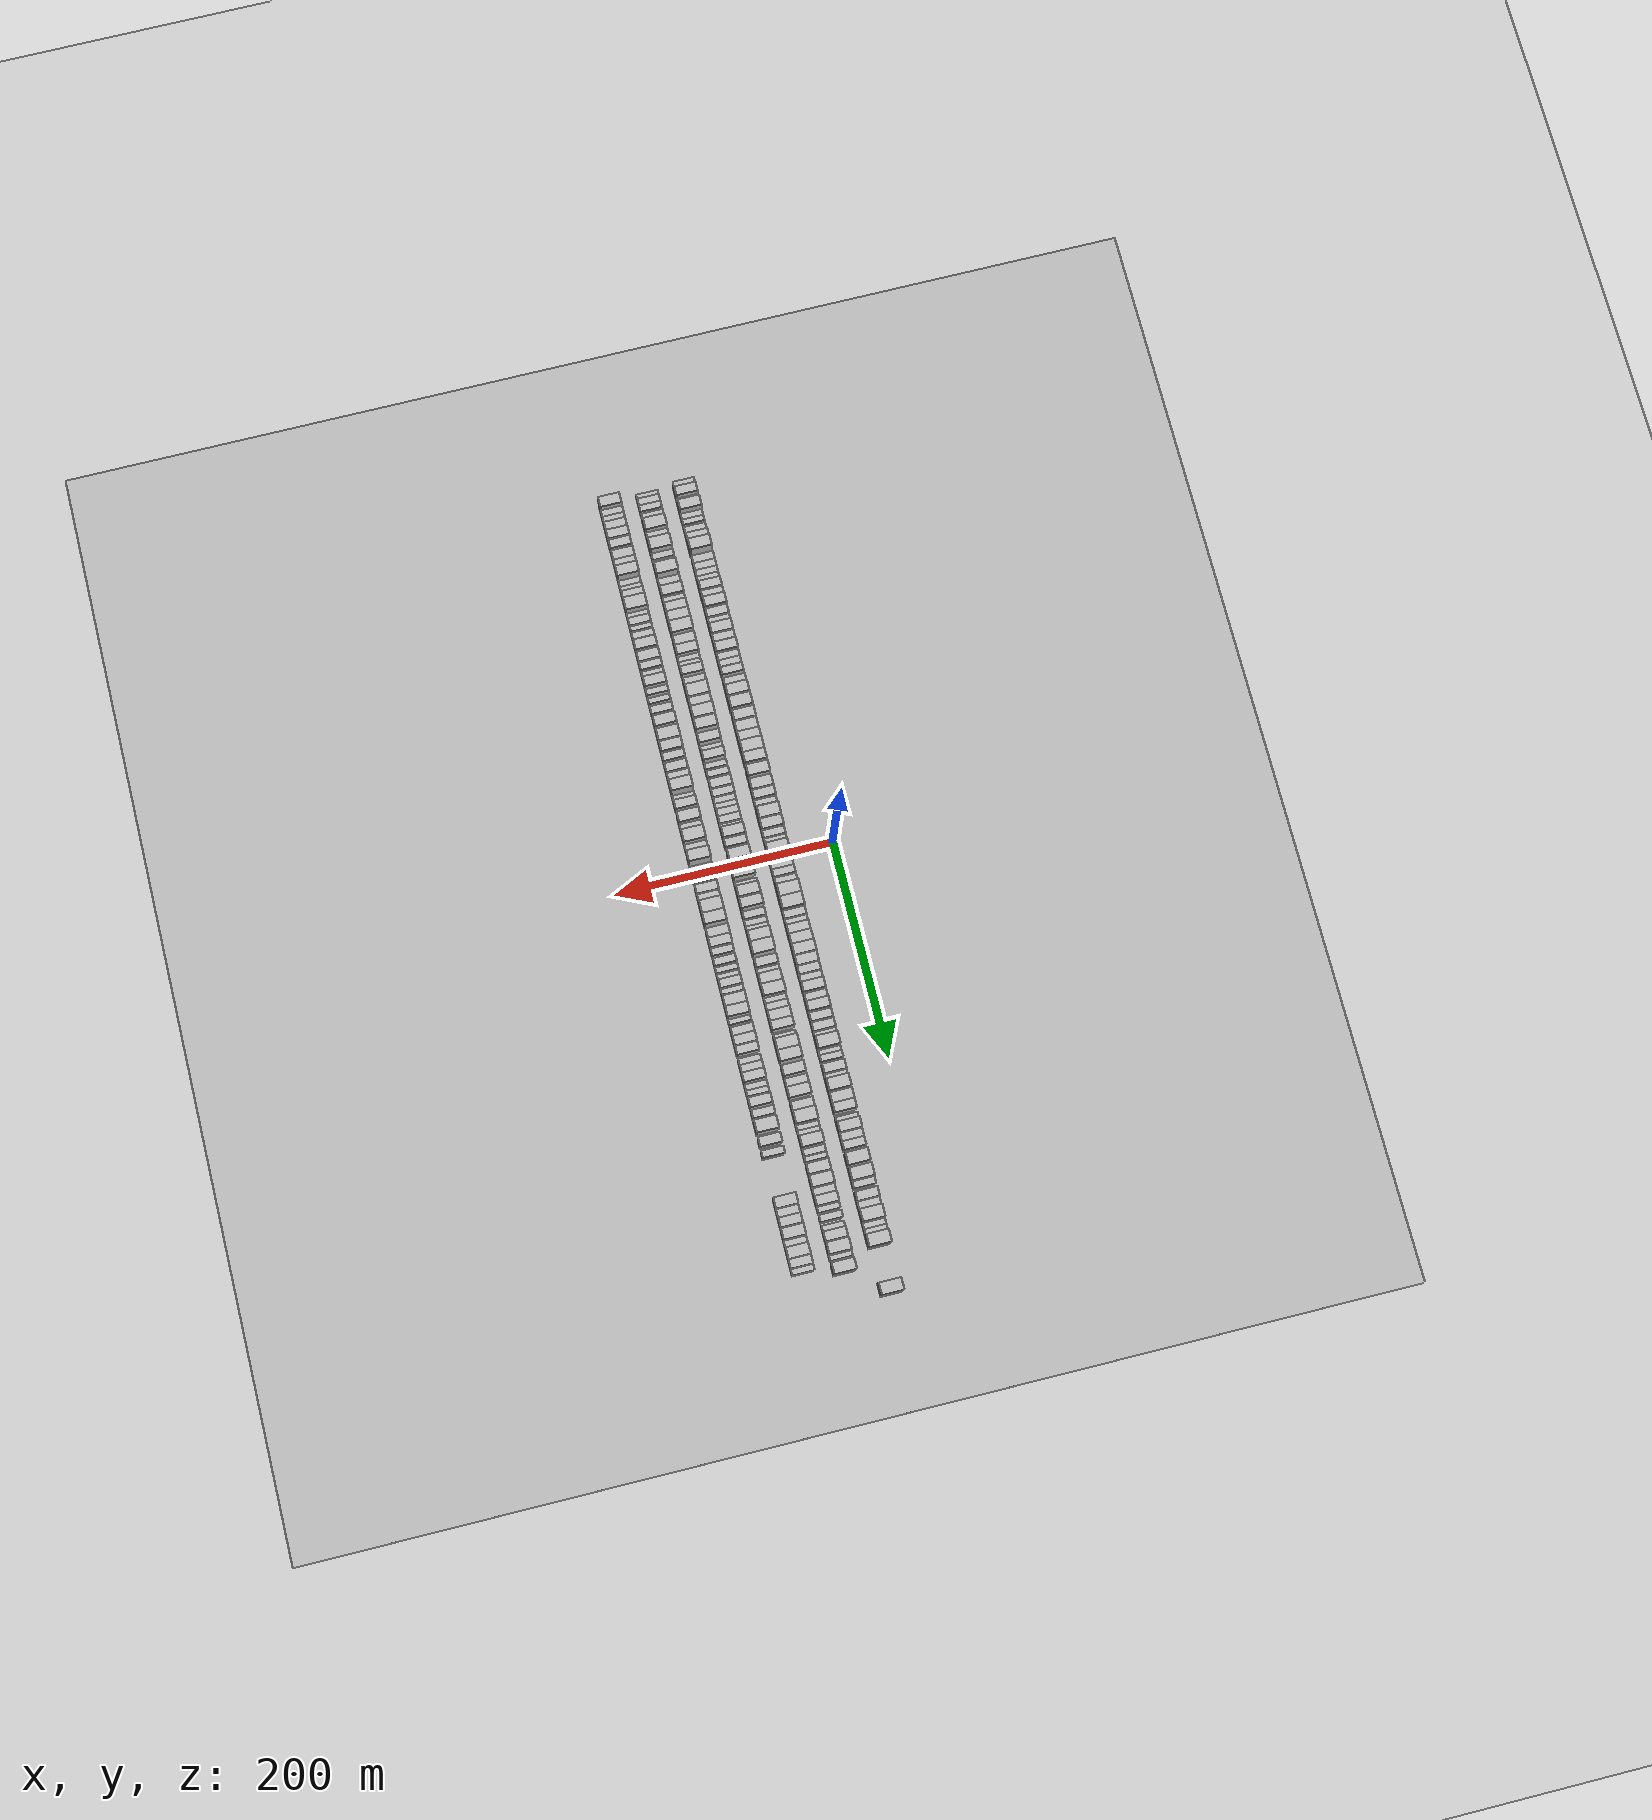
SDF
<?xml version="1.0" encoding="utf-8"?>

<sdf version="1.6">

   <world name="default">

      <gui fullscreen="0">

         <camera name="user_camera">

            <pose>-15 0 4.57585 0 0 0</pose>

            <view_controller>orbit</view_controller>

         </camera>

      </gui>

      <scene>

         <sky>

           <clouds>

             <speed>12</speed>

           </clouds>

         </sky>

         <ambient>0.4 0.4 0.4 1</ambient>

         <background>0.7 0.7 0.7 1</background>

         <shadows>1</shadows>

      </scene>

      <gravity>0 0 -9.8066</gravity>

      <magnetic_field>6e-06 2.3e-05 -4.2e-05</magnetic_field>

      <physics default="0" name="default_physics" type="ode">

         <ode>

            <solver>

               <type>quick</type>

               <iters>10</iters>

               <sor>1.0</sor>

               <use_dynamic_moi_rescaling>0</use_dynamic_moi_rescaling>

            </solver>

            <constraints>

               <cfm>0</cfm>

               <erp>0.2</erp>

               <contact_max_correcting_vel>100</contact_max_correcting_vel>

               <contact_surface_layer>0.001</contact_surface_layer>

            </constraints>

         </ode>

         <max_step_size>0.004</max_step_size>

         <real_time_factor>1</real_time_factor>

         <real_time_update_rate>250</real_time_update_rate>

      </physics>

      <light name="sun" type="directional">

         <cast_shadows>1</cast_shadows>

         <pose>0 0 10 0 0 0</pose>

         <diffuse>0.8 0.8 0.8 1</diffuse>

         <specular>0.2 0.2 0.2 1</specular>

         <attenuation>

            <range>1000</range>

            <constant>0.9</constant>

            <linear>0.01</linear>

            <quadratic>0.001</quadratic>

         </attenuation>

         <direction>-0.5 0.1 -0.9</direction>

      </light>

      <include>

         <name>ground_plane_1</name>

         <uri>model://HANNAS_ground_plane</uri>

         <pose>0 0 0  0 0 0</pose>

      </include>

      <include>

         <name>ground_plane_2</name>

         <uri>model://HANNAS_ground_plane</uri>

         <pose>100 0 0  0 0 0</pose>

      </include>

      <model name="building_1">

         <static>1</static>

         <pose frame="">50.0000 -356.6200 0 0.000000 0.000000 0.000000</pose>

         <link name="link">

            <pose frame="">0 0 7.50 0 0 0</pose>

            <collision name="collision">

               <geometry>

                  <box>

                     <size>20.0000 6.7601 15.0000</size>

                  </box>

               </geometry>

               <max_contacts>10</max_contacts>

               <surface>

                  <contact>

                     <ode/>

                  </contact>

                  <bounce/>

                  <friction>

                     <torsional>

                        <ode/>

                     </torsional>

                     <ode/>

                  </friction>

               </surface>

            </collision>

            <visual name="visual">

               <cast_shadows>0</cast_shadows>

               <geometry>

                  <box>

                     <size>20.0000 6.7601 15.0000</size>

                  </box>

               </geometry>

               <material>

                  <script>

                     <uri>model://HANNAS_wall/materials/scripts</uri>

                     <uri>model://HANNAS_wall/materials/textures</uri>

                     <name>vrc/HANNAS_wall</name>

                  </script>

               </material>

            </visual>

            <self_collide>0</self_collide>

            <enable_wind>0</enable_wind>

            <kinematic>0</kinematic>

         </link>

      </model>

      <model name="building_2">

         <static>1</static>

         <pose frame="">50.0000 -348.8733 0 0.000000 0.000000 0.000000</pose>

         <link name="link">

            <pose frame="">0 0 10.50 0 0 0</pose>

            <collision name="collision">

               <geometry>

                  <box>

                     <size>20.0000 8.7333 21.0000</size>

                  </box>

               </geometry>

               <max_contacts>10</max_contacts>

               <surface>

                  <contact>

                     <ode/>

                  </contact>

                  <bounce/>

                  <friction>

                     <torsional>

                        <ode/>

                     </torsional>

                     <ode/>

                  </friction>

               </surface>

            </collision>

            <visual name="visual">

               <cast_shadows>0</cast_shadows>

               <geometry>

                  <box>

                     <size>20.0000 8.7333 21.0000</size>

                  </box>

               </geometry>

               <material>

                  <script>

                     <uri>model://HANNAS_wall/materials/scripts</uri>

                     <uri>model://HANNAS_wall/materials/textures</uri>

                     <name>vrc/HANNAS_wall</name>

                  </script>

               </material>

            </visual>

            <self_collide>0</self_collide>

            <enable_wind>0</enable_wind>

            <kinematic>0</kinematic>

         </link>

      </model>

      <model name="building_3">

         <static>1</static>

         <pose frame="">50.0000 -341.9335 0 0.000000 0.000000 0.000000</pose>

         <link name="link">

            <pose frame="">0 0 6.00 0 0 0</pose>

            <collision name="collision">

               <geometry>

                  <box>

                     <size>20.0000 5.1462 12.0000</size>

                  </box>

               </geometry>

               <max_contacts>10</max_contacts>

               <surface>

                  <contact>

                     <ode/>

                  </contact>

                  <bounce/>

                  <friction>

                     <torsional>

                        <ode/>

                     </torsional>

                     <ode/>

                  </friction>

               </surface>

            </collision>

            <visual name="visual">

               <cast_shadows>0</cast_shadows>

               <geometry>

                  <box>

                     <size>20.0000 5.1462 12.0000</size>

                  </box>

               </geometry>

               <material>

                  <script>

                     <uri>model://HANNAS_wall/materials/scripts</uri>

                     <uri>model://HANNAS_wall/materials/textures</uri>

                     <name>vrc/HANNAS_wall</name>

                  </script>

               </material>

            </visual>

            <self_collide>0</self_collide>

            <enable_wind>0</enable_wind>

            <kinematic>0</kinematic>

         </link>

      </model>

      <model name="building_4">

         <static>1</static>

         <pose frame="">50.0000 -334.3905 0 0.000000 0.000000 0.000000</pose>

         <link name="link">

            <pose frame="">0 0 12.00 0 0 0</pose>

            <collision name="collision">

               <geometry>

                  <box>

                     <size>20.0000 9.9397 24.0000</size>

                  </box>

               </geometry>

               <max_contacts>10</max_contacts>

               <surface>

                  <contact>

                     <ode/>

                  </contact>

                  <bounce/>

                  <friction>

                     <torsional>

                        <ode/>

                     </torsional>

                     <ode/>

                  </friction>

               </surface>

            </collision>

            <visual name="visual">

               <cast_shadows>0</cast_shadows>

               <geometry>

                  <box>

                     <size>20.0000 9.9397 24.0000</size>

                  </box>

               </geometry>

               <material>

                  <script>

                     <uri>model://HANNAS_wall/materials/scripts</uri>

                     <uri>model://HANNAS_wall/materials/textures</uri>

                     <name>vrc/HANNAS_wall</name>

                  </script>

               </material>

            </visual>

            <self_collide>0</self_collide>

            <enable_wind>0</enable_wind>

            <kinematic>0</kinematic>

         </link>

      </model>

      <model name="building_5">

         <static>1</static>

         <pose frame="">50.0000 -326.5661 0 0.000000 0.000000 0.000000</pose>

         <link name="link">

            <pose frame="">0 0 6.00 0 0 0</pose>

            <collision name="collision">

               <geometry>

                  <box>

                     <size>20.0000 5.7091 12.0000</size>

                  </box>

               </geometry>

               <max_contacts>10</max_contacts>

               <surface>

                  <contact>

                     <ode/>

                  </contact>

                  <bounce/>

                  <friction>

                     <torsional>

                        <ode/>

                     </torsional>

                     <ode/>

                  </friction>

               </surface>

            </collision>

            <visual name="visual">

               <cast_shadows>0</cast_shadows>

               <geometry>

                  <box>

                     <size>20.0000 5.7091 12.0000</size>

                  </box>

               </geometry>

               <material>

                  <script>

                     <uri>model://HANNAS_wall/materials/scripts</uri>

                     <uri>model://HANNAS_wall/materials/textures</uri>

                     <name>vrc/HANNAS_wall</name>

                  </script>

               </material>

            </visual>

            <self_collide>0</self_collide>

            <enable_wind>0</enable_wind>

            <kinematic>0</kinematic>

         </link>

      </model>

      <model name="building_6">

         <static>1</static>

         <pose frame="">50.0000 -321.0969 0 0.000000 0.000000 0.000000</pose>

         <link name="link">

            <pose frame="">0 0 6.00 0 0 0</pose>

            <collision name="collision">

               <geometry>

                  <box>

                     <size>20.0000 5.2293 12.0000</size>

                  </box>

               </geometry>

               <max_contacts>10</max_contacts>

               <surface>

                  <contact>

                     <ode/>

                  </contact>

                  <bounce/>

                  <friction>

                     <torsional>

                        <ode/>

                     </torsional>

                     <ode/>

                  </friction>

               </surface>

            </collision>

            <visual name="visual">

               <cast_shadows>0</cast_shadows>

               <geometry>

                  <box>

                     <size>20.0000 5.2293 12.0000</size>

                  </box>

               </geometry>

               <material>

                  <script>

                     <uri>model://HANNAS_wall/materials/scripts</uri>

                     <uri>model://HANNAS_wall/materials/textures</uri>

                     <name>vrc/HANNAS_wall</name>

                  </script>

               </material>

            </visual>

            <self_collide>0</self_collide>

            <enable_wind>0</enable_wind>

            <kinematic>0</kinematic>

         </link>

      </model>

      <model name="building_7">

         <static>1</static>

         <pose frame="">50.0000 -313.5679 0 0.000000 0.000000 0.000000</pose>

         <link name="link">

            <pose frame="">0 0 6.00 0 0 0</pose>

            <collision name="collision">

               <geometry>

                  <box>

                     <size>20.0000 5.8287 12.0000</size>

                  </box>

               </geometry>

               <max_contacts>10</max_contacts>

               <surface>

                  <contact>

                     <ode/>

                  </contact>

                  <bounce/>

                  <friction>

                     <torsional>

                        <ode/>

                     </torsional>

                     <ode/>

                  </friction>

               </surface>

            </collision>

            <visual name="visual">

               <cast_shadows>0</cast_shadows>

               <geometry>

                  <box>

                     <size>20.0000 5.8287 12.0000</size>

                  </box>

               </geometry>

               <material>

                  <script>

                     <uri>model://HANNAS_wall/materials/scripts</uri>

                     <uri>model://HANNAS_wall/materials/textures</uri>

                     <name>vrc/HANNAS_wall</name>

                  </script>

               </material>

            </visual>

            <self_collide>0</self_collide>

            <enable_wind>0</enable_wind>

            <kinematic>0</kinematic>

         </link>

      </model>

      <model name="building_8">

         <static>1</static>

         <pose frame="">50.0000 -304.7530 0 0.000000 0.000000 0.000000</pose>

         <link name="link">

            <pose frame="">0 0 9.00 0 0 0</pose>

            <collision name="collision">

               <geometry>

                  <box>

                     <size>20.0000 7.8011 18.0000</size>

                  </box>

               </geometry>

               <max_contacts>10</max_contacts>

               <surface>

                  <contact>

                     <ode/>

                  </contact>

                  <bounce/>

                  <friction>

                     <torsional>

                        <ode/>

                     </torsional>

                     <ode/>

                  </friction>

               </surface>

            </collision>

            <visual name="visual">

               <cast_shadows>0</cast_shadows>

               <geometry>

                  <box>

                     <size>20.0000 7.8011 18.0000</size>

                  </box>

               </geometry>

               <material>

                  <script>

                     <uri>model://HANNAS_wall/materials/scripts</uri>

                     <uri>model://HANNAS_wall/materials/textures</uri>

                     <name>vrc/HANNAS_wall</name>

                  </script>

               </material>

            </visual>

            <self_collide>0</self_collide>

            <enable_wind>0</enable_wind>

            <kinematic>0</kinematic>

         </link>

      </model>

      <model name="building_9">

         <static>1</static>

         <pose frame="">50.0000 -295.5351 0 0.000000 0.000000 0.000000</pose>

         <link name="link">

            <pose frame="">0 0 12.00 0 0 0</pose>

            <collision name="collision">

               <geometry>

                  <box>

                     <size>20.0000 10.6348 24.0000</size>

                  </box>

               </geometry>

               <max_contacts>10</max_contacts>

               <surface>

                  <contact>

                     <ode/>

                  </contact>

                  <bounce/>

                  <friction>

                     <torsional>

                        <ode/>

                     </torsional>

                     <ode/>

                  </friction>

               </surface>

            </collision>

            <visual name="visual">

               <cast_shadows>0</cast_shadows>

               <geometry>

                  <box>

                     <size>20.0000 10.6348 24.0000</size>

                  </box>

               </geometry>

               <material>

                  <script>

                     <uri>model://HANNAS_wall/materials/scripts</uri>

                     <uri>model://HANNAS_wall/materials/textures</uri>

                     <name>vrc/HANNAS_wall</name>

                  </script>

               </material>

            </visual>

            <self_collide>0</self_collide>

            <enable_wind>0</enable_wind>

            <kinematic>0</kinematic>

         </link>

      </model>

      <model name="building_10">

         <static>1</static>

         <pose frame="">50.0000 -283.5239 0 0.000000 0.000000 0.000000</pose>

         <link name="link">

            <pose frame="">0 0 7.50 0 0 0</pose>

            <collision name="collision">

               <geometry>

                  <box>

                     <size>20.0000 7.3876 15.0000</size>

                  </box>

               </geometry>

               <max_contacts>10</max_contacts>

               <surface>

                  <contact>

                     <ode/>

                  </contact>

                  <bounce/>

                  <friction>

                     <torsional>

                        <ode/>

                     </torsional>

                     <ode/>

                  </friction>

               </surface>

            </collision>

            <visual name="visual">

               <cast_shadows>0</cast_shadows>

               <geometry>

                  <box>

                     <size>20.0000 7.3876 15.0000</size>

                  </box>

               </geometry>

               <material>

                  <script>

                     <uri>model://HANNAS_wall/materials/scripts</uri>

                     <uri>model://HANNAS_wall/materials/textures</uri>

                     <name>vrc/HANNAS_wall</name>

                  </script>

               </material>

            </visual>

            <self_collide>0</self_collide>

            <enable_wind>0</enable_wind>

            <kinematic>0</kinematic>

         </link>

      </model>

      <model name="building_11">

         <static>1</static>

         <pose frame="">50.0000 -276.3999 0 0.000000 0.000000 0.000000</pose>

         <link name="link">

            <pose frame="">0 0 7.50 0 0 0</pose>

            <collision name="collision">

               <geometry>

                  <box>

                     <size>20.0000 6.8602 15.0000</size>

                  </box>

               </geometry>

               <max_contacts>10</max_contacts>

               <surface>

                  <contact>

                     <ode/>

                  </contact>

                  <bounce/>

                  <friction>

                     <torsional>

                        <ode/>

                     </torsional>

                     <ode/>

                  </friction>

               </surface>

            </collision>

            <visual name="visual">

               <cast_shadows>0</cast_shadows>

               <geometry>

                  <box>

                     <size>20.0000 6.8602 15.0000</size>

                  </box>

               </geometry>

               <material>

                  <script>

                     <uri>model://HANNAS_wall/materials/scripts</uri>

                     <uri>model://HANNAS_wall/materials/textures</uri>

                     <name>vrc/HANNAS_wall</name>

                  </script>

               </material>

            </visual>

            <self_collide>0</self_collide>

            <enable_wind>0</enable_wind>

            <kinematic>0</kinematic>

         </link>

      </model>

      <model name="building_12">

         <static>1</static>

         <pose frame="">50.0000 -269.9434 0 0.000000 0.000000 0.000000</pose>

         <link name="link">

            <pose frame="">0 0 7.50 0 0 0</pose>

            <collision name="collision">

               <geometry>

                  <box>

                     <size>20.0000 6.0530 15.0000</size>

                  </box>

               </geometry>

               <max_contacts>10</max_contacts>

               <surface>

                  <contact>

                     <ode/>

                  </contact>

                  <bounce/>

                  <friction>

                     <torsional>

                        <ode/>

                     </torsional>

                     <ode/>

                  </friction>

               </surface>

            </collision>

            <visual name="visual">

               <cast_shadows>0</cast_shadows>

               <geometry>

                  <box>

                     <size>20.0000 6.0530 15.0000</size>

                  </box>

               </geometry>

               <material>

                  <script>

                     <uri>model://HANNAS_wall/materials/scripts</uri>

                     <uri>model://HANNAS_wall/materials/textures</uri>

                     <name>vrc/HANNAS_wall</name>

                  </script>

               </material>

            </visual>

            <self_collide>0</self_collide>

            <enable_wind>0</enable_wind>

            <kinematic>0</kinematic>

         </link>

      </model>

      <model name="building_13">

         <static>1</static>

         <pose frame="">50.0000 -263.7187 0 0.000000 0.000000 0.000000</pose>

         <link name="link">

            <pose frame="">0 0 7.50 0 0 0</pose>

            <collision name="collision">

               <geometry>

                  <box>

                     <size>20.0000 6.3963 15.0000</size>

                  </box>

               </geometry>

               <max_contacts>10</max_contacts>

               <surface>

                  <contact>

                     <ode/>

                  </contact>

                  <bounce/>

                  <friction>

                     <torsional>

                        <ode/>

                     </torsional>

                     <ode/>

                  </friction>

               </surface>

            </collision>

            <visual name="visual">

               <cast_shadows>0</cast_shadows>

               <geometry>

                  <box>

                     <size>20.0000 6.3963 15.0000</size>

                  </box>

               </geometry>

               <material>

                  <script>

                     <uri>model://HANNAS_wall/materials/scripts</uri>

                     <uri>model://HANNAS_wall/materials/textures</uri>

                     <name>vrc/HANNAS_wall</name>

                  </script>

               </material>

            </visual>

            <self_collide>0</self_collide>

            <enable_wind>0</enable_wind>

            <kinematic>0</kinematic>

         </link>

      </model>

      <model name="building_14">

         <static>1</static>

         <pose frame="">50.0000 -256.2861 0 0.000000 0.000000 0.000000</pose>

         <link name="link">

            <pose frame="">0 0 10.50 0 0 0</pose>

            <collision name="collision">

               <geometry>

                  <box>

                     <size>20.0000 8.4690 21.0000</size>

                  </box>

               </geometry>

               <max_contacts>10</max_contacts>

               <surface>

                  <contact>

                     <ode/>

                  </contact>

                  <bounce/>

                  <friction>

                     <torsional>

                        <ode/>

                     </torsional>

                     <ode/>

                  </friction>

               </surface>

            </collision>

            <visual name="visual">

               <cast_shadows>0</cast_shadows>

               <geometry>

                  <box>

                     <size>20.0000 8.4690 21.0000</size>

                  </box>

               </geometry>

               <material>

                  <script>

                     <uri>model://HANNAS_wall/materials/scripts</uri>

                     <uri>model://HANNAS_wall/materials/textures</uri>

                     <name>vrc/HANNAS_wall</name>

                  </script>

               </material>

            </visual>

            <self_collide>0</self_collide>

            <enable_wind>0</enable_wind>

            <kinematic>0</kinematic>

         </link>

      </model>

      <model name="building_15">

         <static>1</static>

         <pose frame="">50.0000 -248.1582 0 0.000000 0.000000 0.000000</pose>

         <link name="link">

            <pose frame="">0 0 9.00 0 0 0</pose>

            <collision name="collision">

               <geometry>

                  <box>

                     <size>20.0000 7.7868 18.0000</size>

                  </box>

               </geometry>

               <max_contacts>10</max_contacts>

               <surface>

                  <contact>

                     <ode/>

                  </contact>

                  <bounce/>

                  <friction>

                     <torsional>

                        <ode/>

                     </torsional>

                     <ode/>

                  </friction>

               </surface>

            </collision>

            <visual name="visual">

               <cast_shadows>0</cast_shadows>

               <geometry>

                  <box>

                     <size>20.0000 7.7868 18.0000</size>

                  </box>

               </geometry>

               <material>

                  <script>

                     <uri>model://HANNAS_wall/materials/scripts</uri>

                     <uri>model://HANNAS_wall/materials/textures</uri>

                     <name>vrc/HANNAS_wall</name>

                  </script>

               </material>

            </visual>

            <self_collide>0</self_collide>

            <enable_wind>0</enable_wind>

            <kinematic>0</kinematic>

         </link>

      </model>

      <model name="building_16">

         <static>1</static>

         <pose frame="">50.0000 -239.4405 0 0.000000 0.000000 0.000000</pose>

         <link name="link">

            <pose frame="">0 0 12.00 0 0 0</pose>

            <collision name="collision">

               <geometry>

                  <box>

                     <size>20.0000 9.6487 24.0000</size>

                  </box>

               </geometry>

               <max_contacts>10</max_contacts>

               <surface>

                  <contact>

                     <ode/>

                  </contact>

                  <bounce/>

                  <friction>

                     <torsional>

                        <ode/>

                     </torsional>

                     <ode/>

                  </friction>

               </surface>

            </collision>

            <visual name="visual">

               <cast_shadows>0</cast_shadows>

               <geometry>

                  <box>

                     <size>20.0000 9.6487 24.0000</size>

                  </box>

               </geometry>

               <material>

                  <script>

                     <uri>model://HANNAS_wall/materials/scripts</uri>

                     <uri>model://HANNAS_wall/materials/textures</uri>

                     <name>vrc/HANNAS_wall</name>

                  </script>

               </material>

            </visual>

            <self_collide>0</self_collide>

            <enable_wind>0</enable_wind>

            <kinematic>0</kinematic>

         </link>

      </model>

      <model name="building_17">

         <static>1</static>

         <pose frame="">50.0000 -230.4043 0 0.000000 0.000000 0.000000</pose>

         <link name="link">

            <pose frame="">0 0 9.00 0 0 0</pose>

            <collision name="collision">

               <geometry>

                  <box>

                     <size>20.0000 8.4235 18.0000</size>

                  </box>

               </geometry>

               <max_contacts>10</max_contacts>

               <surface>

                  <contact>

                     <ode/>

                  </contact>

                  <bounce/>

                  <friction>

                     <torsional>

                        <ode/>

                     </torsional>

                     <ode/>

                  </friction>

               </surface>

            </collision>

            <visual name="visual">

               <cast_shadows>0</cast_shadows>

               <geometry>

                  <box>

                     <size>20.0000 8.4235 18.0000</size>

                  </box>

               </geometry>

               <material>

                  <script>

                     <uri>model://HANNAS_wall/materials/scripts</uri>

                     <uri>model://HANNAS_wall/materials/textures</uri>

                     <name>vrc/HANNAS_wall</name>

                  </script>

               </material>

            </visual>

            <self_collide>0</self_collide>

            <enable_wind>0</enable_wind>

            <kinematic>0</kinematic>

         </link>

      </model>

      <model name="building_18">

         <static>1</static>

         <pose frame="">50.0000 -222.9720 0 0.000000 0.000000 0.000000</pose>

         <link name="link">

            <pose frame="">0 0 7.50 0 0 0</pose>

            <collision name="collision">

               <geometry>

                  <box>

                     <size>20.0000 6.4411 15.0000</size>

                  </box>

               </geometry>

               <max_contacts>10</max_contacts>

               <surface>

                  <contact>

                     <ode/>

                  </contact>

                  <bounce/>

                  <friction>

                     <torsional>

                        <ode/>

                     </torsional>

                     <ode/>

                  </friction>

               </surface>

            </collision>

            <visual name="visual">

               <cast_shadows>0</cast_shadows>

               <geometry>

                  <box>

                     <size>20.0000 6.4411 15.0000</size>

                  </box>

               </geometry>

               <material>

                  <script>

                     <uri>model://HANNAS_wall/materials/scripts</uri>

                     <uri>model://HANNAS_wall/materials/textures</uri>

                     <name>vrc/HANNAS_wall</name>

                  </script>

               </material>

            </visual>

            <self_collide>0</self_collide>

            <enable_wind>0</enable_wind>

            <kinematic>0</kinematic>

         </link>

      </model>

      <model name="building_19">

         <static>1</static>

         <pose frame="">50.0000 -214.8241 0 0.000000 0.000000 0.000000</pose>

         <link name="link">

            <pose frame="">0 0 10.50 0 0 0</pose>

            <collision name="collision">

               <geometry>

                  <box>

                     <size>20.0000 9.8547 21.0000</size>

                  </box>

               </geometry>

               <max_contacts>10</max_contacts>

               <surface>

                  <contact>

                     <ode/>

                  </contact>

                  <bounce/>

                  <friction>

                     <torsional>

                        <ode/>

                     </torsional>

                     <ode/>

                  </friction>

               </surface>

            </collision>

            <visual name="visual">

               <cast_shadows>0</cast_shadows>

               <geometry>

                  <box>

                     <size>20.0000 9.8547 21.0000</size>

                  </box>

               </geometry>

               <material>

                  <script>

                     <uri>model://HANNAS_wall/materials/scripts</uri>

                     <uri>model://HANNAS_wall/materials/textures</uri>

                     <name>vrc/HANNAS_wall</name>

                  </script>

               </material>

            </visual>

            <self_collide>0</self_collide>

            <enable_wind>0</enable_wind>

            <kinematic>0</kinematic>

         </link>

      </model>

      <model name="building_20">

         <static>1</static>

         <pose frame="">50.0000 -206.2114 0 0.000000 0.000000 0.000000</pose>

         <link name="link">

            <pose frame="">0 0 9.00 0 0 0</pose>

            <collision name="collision">

               <geometry>

                  <box>

                     <size>20.0000 7.3707 18.0000</size>

                  </box>

               </geometry>

               <max_contacts>10</max_contacts>

               <surface>

                  <contact>

                     <ode/>

                  </contact>

                  <bounce/>

                  <friction>

                     <torsional>

                        <ode/>

                     </torsional>

                     <ode/>

                  </friction>

               </surface>

            </collision>

            <visual name="visual">

               <cast_shadows>0</cast_shadows>

               <geometry>

                  <box>

                     <size>20.0000 7.3707 18.0000</size>

                  </box>

               </geometry>

               <material>

                  <script>

                     <uri>model://HANNAS_wall/materials/scripts</uri>

                     <uri>model://HANNAS_wall/materials/textures</uri>

                     <name>vrc/HANNAS_wall</name>

                  </script>

               </material>

            </visual>

            <self_collide>0</self_collide>

            <enable_wind>0</enable_wind>

            <kinematic>0</kinematic>

         </link>

      </model>

      <model name="building_21">

         <static>1</static>

         <pose frame="">50.0000 -196.8232 0 0.000000 0.000000 0.000000</pose>

         <link name="link">

            <pose frame="">0 0 10.50 0 0 0</pose>

            <collision name="collision">

               <geometry>

                  <box>

                     <size>20.0000 9.4058 21.0000</size>

                  </box>

               </geometry>

               <max_contacts>10</max_contacts>

               <surface>

                  <contact>

                     <ode/>

                  </contact>

                  <bounce/>

                  <friction>

                     <torsional>

                        <ode/>

                     </torsional>

                     <ode/>

                  </friction>

               </surface>

            </collision>

            <visual name="visual">

               <cast_shadows>0</cast_shadows>

               <geometry>

                  <box>

                     <size>20.0000 9.4058 21.0000</size>

                  </box>

               </geometry>

               <material>

                  <script>

                     <uri>model://HANNAS_wall/materials/scripts</uri>

                     <uri>model://HANNAS_wall/materials/textures</uri>

                     <name>vrc/HANNAS_wall</name>

                  </script>

               </material>

            </visual>

            <self_collide>0</self_collide>

            <enable_wind>0</enable_wind>

            <kinematic>0</kinematic>

         </link>

      </model>

      <model name="building_22">

         <static>1</static>

         <pose frame="">50.0000 -188.7874 0 0.000000 0.000000 0.000000</pose>

         <link name="link">

            <pose frame="">0 0 7.50 0 0 0</pose>

            <collision name="collision">

               <geometry>

                  <box>

                     <size>20.0000 6.6657 15.0000</size>

                  </box>

               </geometry>

               <max_contacts>10</max_contacts>

               <surface>

                  <contact>

                     <ode/>

                  </contact>

                  <bounce/>

                  <friction>

                     <torsional>

                        <ode/>

                     </torsional>

                     <ode/>

                  </friction>

               </surface>

            </collision>

            <visual name="visual">

               <cast_shadows>0</cast_shadows>

               <geometry>

                  <box>

                     <size>20.0000 6.6657 15.0000</size>

                  </box>

               </geometry>

               <material>

                  <script>

                     <uri>model://HANNAS_wall/materials/scripts</uri>

                     <uri>model://HANNAS_wall/materials/textures</uri>

                     <name>vrc/HANNAS_wall</name>

                  </script>

               </material>

            </visual>

            <self_collide>0</self_collide>

            <enable_wind>0</enable_wind>

            <kinematic>0</kinematic>

         </link>

      </model>

      <model name="building_23">

         <static>1</static>

         <pose frame="">50.0000 -182.2172 0 0.000000 0.000000 0.000000</pose>

         <link name="link">

            <pose frame="">0 0 7.50 0 0 0</pose>

            <collision name="collision">

               <geometry>

                  <box>

                     <size>20.0000 6.4747 15.0000</size>

                  </box>

               </geometry>

               <max_contacts>10</max_contacts>

               <surface>

                  <contact>

                     <ode/>

                  </contact>

                  <bounce/>

                  <friction>

                     <torsional>

                        <ode/>

                     </torsional>

                     <ode/>

                  </friction>

               </surface>

            </collision>

            <visual name="visual">

               <cast_shadows>0</cast_shadows>

               <geometry>

                  <box>

                     <size>20.0000 6.4747 15.0000</size>

                  </box>

               </geometry>

               <material>

                  <script>

                     <uri>model://HANNAS_wall/materials/scripts</uri>

                     <uri>model://HANNAS_wall/materials/textures</uri>

                     <name>vrc/HANNAS_wall</name>

                  </script>

               </material>

            </visual>

            <self_collide>0</self_collide>

            <enable_wind>0</enable_wind>

            <kinematic>0</kinematic>

         </link>

      </model>

      <model name="building_24">

         <static>1</static>

         <pose frame="">50.0000 -174.2768 0 0.000000 0.000000 0.000000</pose>

         <link name="link">

            <pose frame="">0 0 9.00 0 0 0</pose>

            <collision name="collision">

               <geometry>

                  <box>

                     <size>20.0000 7.4062 18.0000</size>

                  </box>

               </geometry>

               <max_contacts>10</max_contacts>

               <surface>

                  <contact>

                     <ode/>

                  </contact>

                  <bounce/>

                  <friction>

                     <torsional>

                        <ode/>

                     </torsional>

                     <ode/>

                  </friction>

               </surface>

            </collision>

            <visual name="visual">

               <cast_shadows>0</cast_shadows>

               <geometry>

                  <box>

                     <size>20.0000 7.4062 18.0000</size>

                  </box>

               </geometry>

               <material>

                  <script>

                     <uri>model://HANNAS_wall/materials/scripts</uri>

                     <uri>model://HANNAS_wall/materials/textures</uri>

                     <name>vrc/HANNAS_wall</name>

                  </script>

               </material>

            </visual>

            <self_collide>0</self_collide>

            <enable_wind>0</enable_wind>

            <kinematic>0</kinematic>

         </link>

      </model>

      <model name="building_25">

         <static>1</static>

         <pose frame="">50.0000 -163.5895 0 0.000000 0.000000 0.000000</pose>

         <link name="link">

            <pose frame="">0 0 9.00 0 0 0</pose>

            <collision name="collision">

               <geometry>

                  <box>

                     <size>20.0000 7.9683 18.0000</size>

                  </box>

               </geometry>

               <max_contacts>10</max_contacts>

               <surface>

                  <contact>

                     <ode/>

                  </contact>

                  <bounce/>

                  <friction>

                     <torsional>

                        <ode/>

                     </torsional>

                     <ode/>

                  </friction>

               </surface>

            </collision>

            <visual name="visual">

               <cast_shadows>0</cast_shadows>

               <geometry>

                  <box>

                     <size>20.0000 7.9683 18.0000</size>

                  </box>

               </geometry>

               <material>

                  <script>

                     <uri>model://HANNAS_wall/materials/scripts</uri>

                     <uri>model://HANNAS_wall/materials/textures</uri>

                     <name>vrc/HANNAS_wall</name>

                  </script>

               </material>

            </visual>

            <self_collide>0</self_collide>

            <enable_wind>0</enable_wind>

            <kinematic>0</kinematic>

         </link>

      </model>

      <model name="building_26">

         <static>1</static>

         <pose frame="">50.0000 -154.4490 0 0.000000 0.000000 0.000000</pose>

         <link name="link">

            <pose frame="">0 0 12.00 0 0 0</pose>

            <collision name="collision">

               <geometry>

                  <box>

                     <size>20.0000 10.3128 24.0000</size>

                  </box>

               </geometry>

               <max_contacts>10</max_contacts>

               <surface>

                  <contact>

                     <ode/>

                  </contact>

                  <bounce/>

                  <friction>

                     <torsional>

                        <ode/>

                     </torsional>

                     <ode/>

                  </friction>

               </surface>

            </collision>

            <visual name="visual">

               <cast_shadows>0</cast_shadows>

               <geometry>

                  <box>

                     <size>20.0000 10.3128 24.0000</size>

                  </box>

               </geometry>

               <material>

                  <script>

                     <uri>model://HANNAS_wall/materials/scripts</uri>

                     <uri>model://HANNAS_wall/materials/textures</uri>

                     <name>vrc/HANNAS_wall</name>

                  </script>

               </material>

            </visual>

            <self_collide>0</self_collide>

            <enable_wind>0</enable_wind>

            <kinematic>0</kinematic>

         </link>

      </model>

      <model name="building_27">

         <static>1</static>

         <pose frame="">50.0000 -142.6936 0 0.000000 0.000000 0.000000</pose>

         <link name="link">

            <pose frame="">0 0 12.00 0 0 0</pose>

            <collision name="collision">

               <geometry>

                  <box>

                     <size>20.0000 11.1979 24.0000</size>

                  </box>

               </geometry>

               <max_contacts>10</max_contacts>

               <surface>

                  <contact>

                     <ode/>

                  </contact>

                  <bounce/>

                  <friction>

                     <torsional>

                        <ode/>

                     </torsional>

                     <ode/>

                  </friction>

               </surface>

            </collision>

            <visual name="visual">

               <cast_shadows>0</cast_shadows>

               <geometry>

                  <box>

                     <size>20.0000 11.1979 24.0000</size>

                  </box>

               </geometry>

               <material>

                  <script>

                     <uri>model://HANNAS_wall/materials/scripts</uri>

                     <uri>model://HANNAS_wall/materials/textures</uri>

                     <name>vrc/HANNAS_wall</name>

                  </script>

               </material>

            </visual>

            <self_collide>0</self_collide>

            <enable_wind>0</enable_wind>

            <kinematic>0</kinematic>

         </link>

      </model>

      <model name="building_28">

         <static>1</static>

         <pose frame="">50.0000 -130.1656 0 0.000000 0.000000 0.000000</pose>

         <link name="link">

            <pose frame="">0 0 12.00 0 0 0</pose>

            <collision name="collision">

               <geometry>

                  <box>

                     <size>20.0000 9.8582 24.0000</size>

                  </box>

               </geometry>

               <max_contacts>10</max_contacts>

               <surface>

                  <contact>

                     <ode/>

                  </contact>

                  <bounce/>

                  <friction>

                     <torsional>

                        <ode/>

                     </torsional>

                     <ode/>

                  </friction>

               </surface>

            </collision>

            <visual name="visual">

               <cast_shadows>0</cast_shadows>

               <geometry>

                  <box>

                     <size>20.0000 9.8582 24.0000</size>

                  </box>

               </geometry>

               <material>

                  <script>

                     <uri>model://HANNAS_wall/materials/scripts</uri>

                     <uri>model://HANNAS_wall/materials/textures</uri>

                     <name>vrc/HANNAS_wall</name>

                  </script>

               </material>

            </visual>

            <self_collide>0</self_collide>

            <enable_wind>0</enable_wind>

            <kinematic>0</kinematic>

         </link>

      </model>

      <model name="building_29">

         <static>1</static>

         <pose frame="">50.0000 -120.3408 0 0.000000 0.000000 0.000000</pose>

         <link name="link">

            <pose frame="">0 0 10.50 0 0 0</pose>

            <collision name="collision">

               <geometry>

                  <box>

                     <size>20.0000 9.7914 21.0000</size>

                  </box>

               </geometry>

               <max_contacts>10</max_contacts>

               <surface>

                  <contact>

                     <ode/>

                  </contact>

                  <bounce/>

                  <friction>

                     <torsional>

                        <ode/>

                     </torsional>

                     <ode/>

                  </friction>

               </surface>

            </collision>

            <visual name="visual">

               <cast_shadows>0</cast_shadows>

               <geometry>

                  <box>

                     <size>20.0000 9.7914 21.0000</size>

                  </box>

               </geometry>

               <material>

                  <script>

                     <uri>model://HANNAS_wall/materials/scripts</uri>

                     <uri>model://HANNAS_wall/materials/textures</uri>

                     <name>vrc/HANNAS_wall</name>

                  </script>

               </material>

            </visual>

            <self_collide>0</self_collide>

            <enable_wind>0</enable_wind>

            <kinematic>0</kinematic>

         </link>

      </model>

      <model name="building_30">

         <static>1</static>

         <pose frame="">50.0000 -110.8411 0 0.000000 0.000000 0.000000</pose>

         <link name="link">

            <pose frame="">0 0 10.50 0 0 0</pose>

            <collision name="collision">

               <geometry>

                  <box>

                     <size>20.0000 9.2081 21.0000</size>

                  </box>

               </geometry>

               <max_contacts>10</max_contacts>

               <surface>

                  <contact>

                     <ode/>

                  </contact>

                  <bounce/>

                  <friction>

                     <torsional>

                        <ode/>

                     </torsional>

                     <ode/>

                  </friction>

               </surface>

            </collision>

            <visual name="visual">

               <cast_shadows>0</cast_shadows>

               <geometry>

                  <box>

                     <size>20.0000 9.2081 21.0000</size>

                  </box>

               </geometry>

               <material>

                  <script>

                     <uri>model://HANNAS_wall/materials/scripts</uri>

                     <uri>model://HANNAS_wall/materials/textures</uri>

                     <name>vrc/HANNAS_wall</name>

                  </script>

               </material>

            </visual>

            <self_collide>0</self_collide>

            <enable_wind>0</enable_wind>

            <kinematic>0</kinematic>

         </link>

      </model>

      <model name="building_31">

         <static>1</static>

         <pose frame="">50.0000 -100.6707 0 0.000000 0.000000 0.000000</pose>

         <link name="link">

            <pose frame="">0 0 12.00 0 0 0</pose>

            <collision name="collision">

               <geometry>

                  <box>

                     <size>20.0000 11.1326 24.0000</size>

                  </box>

               </geometry>

               <max_contacts>10</max_contacts>

               <surface>

                  <contact>

                     <ode/>

                  </contact>

                  <bounce/>

                  <friction>

                     <torsional>

                        <ode/>

                     </torsional>

                     <ode/>

                  </friction>

               </surface>

            </collision>

            <visual name="visual">

               <cast_shadows>0</cast_shadows>

               <geometry>

                  <box>

                     <size>20.0000 11.1326 24.0000</size>

                  </box>

               </geometry>

               <material>

                  <script>

                     <uri>model://HANNAS_wall/materials/scripts</uri>

                     <uri>model://HANNAS_wall/materials/textures</uri>

                     <name>vrc/HANNAS_wall</name>

                  </script>

               </material>

            </visual>

            <self_collide>0</self_collide>

            <enable_wind>0</enable_wind>

            <kinematic>0</kinematic>

         </link>

      </model>

      <model name="building_32">

         <static>1</static>

         <pose frame="">50.0000 -90.1724 0 0.000000 0.000000 0.000000</pose>

         <link name="link">

            <pose frame="">0 0 12.00 0 0 0</pose>

            <collision name="collision">

               <geometry>

                  <box>

                     <size>20.0000 9.8641 24.0000</size>

                  </box>

               </geometry>

               <max_contacts>10</max_contacts>

               <surface>

                  <contact>

                     <ode/>

                  </contact>

                  <bounce/>

                  <friction>

                     <torsional>

                        <ode/>

                     </torsional>

                     <ode/>

                  </friction>

               </surface>

            </collision>

            <visual name="visual">

               <cast_shadows>0</cast_shadows>

               <geometry>

                  <box>

                     <size>20.0000 9.8641 24.0000</size>

                  </box>

               </geometry>

               <material>

                  <script>

                     <uri>model://HANNAS_wall/materials/scripts</uri>

                     <uri>model://HANNAS_wall/materials/textures</uri>

                     <name>vrc/HANNAS_wall</name>

                  </script>

               </material>

            </visual>

            <self_collide>0</self_collide>

            <enable_wind>0</enable_wind>

            <kinematic>0</kinematic>

         </link>

      </model>

      <model name="building_33">

         <static>1</static>

         <pose frame="">50.0000 -78.0503 0 0.000000 0.000000 0.000000</pose>

         <link name="link">

            <pose frame="">0 0 12.00 0 0 0</pose>

            <collision name="collision">

               <geometry>

                  <box>

                     <size>20.0000 10.3800 24.0000</size>

                  </box>

               </geometry>

               <max_contacts>10</max_contacts>

               <surface>

                  <contact>

                     <ode/>

                  </contact>

                  <bounce/>

                  <friction>

                     <torsional>

                        <ode/>

                     </torsional>

                     <ode/>

                  </friction>

               </surface>

            </collision>

            <visual name="visual">

               <cast_shadows>0</cast_shadows>

               <geometry>

                  <box>

                     <size>20.0000 10.3800 24.0000</size>

                  </box>

               </geometry>

               <material>

                  <script>

                     <uri>model://HANNAS_wall/materials/scripts</uri>

                     <uri>model://HANNAS_wall/materials/textures</uri>

                     <name>vrc/HANNAS_wall</name>

                  </script>

               </material>

            </visual>

            <self_collide>0</self_collide>

            <enable_wind>0</enable_wind>

            <kinematic>0</kinematic>

         </link>

      </model>

      <model name="building_34">

         <static>1</static>

         <pose frame="">50.0000 -65.8512 0 0.000000 0.000000 0.000000</pose>

         <link name="link">

            <pose frame="">0 0 10.50 0 0 0</pose>

            <collision name="collision">

               <geometry>

                  <box>

                     <size>20.0000 10.0182 21.0000</size>

                  </box>

               </geometry>

               <max_contacts>10</max_contacts>

               <surface>

                  <contact>

                     <ode/>

                  </contact>

                  <bounce/>

                  <friction>

                     <torsional>

                        <ode/>

                     </torsional>

                     <ode/>

                  </friction>

               </surface>

            </collision>

            <visual name="visual">

               <cast_shadows>0</cast_shadows>

               <geometry>

                  <box>

                     <size>20.0000 10.0182 21.0000</size>

                  </box>

               </geometry>

               <material>

                  <script>

                     <uri>model://HANNAS_wall/materials/scripts</uri>

                     <uri>model://HANNAS_wall/materials/textures</uri>

                     <name>vrc/HANNAS_wall</name>

                  </script>

               </material>

            </visual>

            <self_collide>0</self_collide>

            <enable_wind>0</enable_wind>

            <kinematic>0</kinematic>

         </link>

      </model>

      <model name="building_35">

         <static>1</static>

         <pose frame="">50.0000 -56.6109 0 0.000000 0.000000 0.000000</pose>

         <link name="link">

            <pose frame="">0 0 9.00 0 0 0</pose>

            <collision name="collision">

               <geometry>

                  <box>

                     <size>20.0000 8.4623 18.0000</size>

                  </box>

               </geometry>

               <max_contacts>10</max_contacts>

               <surface>

                  <contact>

                     <ode/>

                  </contact>

                  <bounce/>

                  <friction>

                     <torsional>

                        <ode/>

                     </torsional>

                     <ode/>

                  </friction>

               </surface>

            </collision>

            <visual name="visual">

               <cast_shadows>0</cast_shadows>

               <geometry>

                  <box>

                     <size>20.0000 8.4623 18.0000</size>

                  </box>

               </geometry>

               <material>

                  <script>

                     <uri>model://HANNAS_wall/materials/scripts</uri>

                     <uri>model://HANNAS_wall/materials/textures</uri>

                     <name>vrc/HANNAS_wall</name>

                  </script>

               </material>

            </visual>

            <self_collide>0</self_collide>

            <enable_wind>0</enable_wind>

            <kinematic>0</kinematic>

         </link>

      </model>

      <model name="building_36">

         <static>1</static>

         <pose frame="">50.0000 -49.6874 0 0.000000 0.000000 0.000000</pose>

         <link name="link">

            <pose frame="">0 0 6.00 0 0 0</pose>

            <collision name="collision">

               <geometry>

                  <box>

                     <size>20.0000 5.3847 12.0000</size>

                  </box>

               </geometry>

               <max_contacts>10</max_contacts>

               <surface>

                  <contact>

                     <ode/>

                  </contact>

                  <bounce/>

                  <friction>

                     <torsional>

                        <ode/>

                     </torsional>

                     <ode/>

                  </friction>

               </surface>

            </collision>

            <visual name="visual">

               <cast_shadows>0</cast_shadows>

               <geometry>

                  <box>

                     <size>20.0000 5.3847 12.0000</size>

                  </box>

               </geometry>

               <material>

                  <script>

                     <uri>model://HANNAS_wall/materials/scripts</uri>

                     <uri>model://HANNAS_wall/materials/textures</uri>

                     <name>vrc/HANNAS_wall</name>

                  </script>

               </material>

            </visual>

            <self_collide>0</self_collide>

            <enable_wind>0</enable_wind>

            <kinematic>0</kinematic>

         </link>

      </model>

      <model name="building_37">

         <static>1</static>

         <pose frame="">50.0000 -38.5183 0 0.000000 0.000000 0.000000</pose>

         <link name="link">

            <pose frame="">0 0 12.00 0 0 0</pose>

            <collision name="collision">

               <geometry>

                  <box>

                     <size>20.0000 10.9537 24.0000</size>

                  </box>

               </geometry>

               <max_contacts>10</max_contacts>

               <surface>

                  <contact>

                     <ode/>

                  </contact>

                  <bounce/>

                  <friction>

                     <torsional>

                        <ode/>

                     </torsional>

                     <ode/>

                  </friction>

               </surface>

            </collision>

            <visual name="visual">

               <cast_shadows>0</cast_shadows>

               <geometry>

                  <box>

                     <size>20.0000 10.9537 24.0000</size>

                  </box>

               </geometry>

               <material>

                  <script>

                     <uri>model://HANNAS_wall/materials/scripts</uri>

                     <uri>model://HANNAS_wall/materials/textures</uri>

                     <name>vrc/HANNAS_wall</name>

                  </script>

               </material>

            </visual>

            <self_collide>0</self_collide>

            <enable_wind>0</enable_wind>

            <kinematic>0</kinematic>

         </link>

      </model>

      <model name="building_38">

         <static>1</static>

         <pose frame="">50.0000 -28.2136 0 0.000000 0.000000 0.000000</pose>

         <link name="link">

            <pose frame="">0 0 10.50 0 0 0</pose>

            <collision name="collision">

               <geometry>

                  <box>

                     <size>20.0000 9.6557 21.0000</size>

                  </box>

               </geometry>

               <max_contacts>10</max_contacts>

               <surface>

                  <contact>

                     <ode/>

                  </contact>

                  <bounce/>

                  <friction>

                     <torsional>

                        <ode/>

                     </torsional>

                     <ode/>

                  </friction>

               </surface>

            </collision>

            <visual name="visual">

               <cast_shadows>0</cast_shadows>

               <geometry>

                  <box>

                     <size>20.0000 9.6557 21.0000</size>

                  </box>

               </geometry>

               <material>

                  <script>

                     <uri>model://HANNAS_wall/materials/scripts</uri>

                     <uri>model://HANNAS_wall/materials/textures</uri>

                     <name>vrc/HANNAS_wall</name>

                  </script>

               </material>

            </visual>

            <self_collide>0</self_collide>

            <enable_wind>0</enable_wind>

            <kinematic>0</kinematic>

         </link>

      </model>

      <model name="building_39">

         <static>1</static>

         <pose frame="">50.0000 -19.8832 0 0.000000 0.000000 0.000000</pose>

         <link name="link">

            <pose frame="">0 0 7.50 0 0 0</pose>

            <collision name="collision">

               <geometry>

                  <box>

                     <size>20.0000 7.0051 15.0000</size>

                  </box>

               </geometry>

               <max_contacts>10</max_contacts>

               <surface>

                  <contact>

                     <ode/>

                  </contact>

                  <bounce/>

                  <friction>

                     <torsional>

                        <ode/>

                     </torsional>

                     <ode/>

                  </friction>

               </surface>

            </collision>

            <visual name="visual">

               <cast_shadows>0</cast_shadows>

               <geometry>

                  <box>

                     <size>20.0000 7.0051 15.0000</size>

                  </box>

               </geometry>

               <material>

                  <script>

                     <uri>model://HANNAS_wall/materials/scripts</uri>

                     <uri>model://HANNAS_wall/materials/textures</uri>

                     <name>vrc/HANNAS_wall</name>

                  </script>

               </material>

            </visual>

            <self_collide>0</self_collide>

            <enable_wind>0</enable_wind>

            <kinematic>0</kinematic>

         </link>

      </model>

      <model name="building_40">

         <static>1</static>

         <pose frame="">50.0000 -13.8369 0 0.000000 0.000000 0.000000</pose>

         <link name="link">

            <pose frame="">0 0 6.00 0 0 0</pose>

            <collision name="collision">

               <geometry>

                  <box>

                     <size>20.0000 5.0874 12.0000</size>

                  </box>

               </geometry>

               <max_contacts>10</max_contacts>

               <surface>

                  <contact>

                     <ode/>

                  </contact>

                  <bounce/>

                  <friction>

                     <torsional>

                        <ode/>

                     </torsional>

                     <ode/>

                  </friction>

               </surface>

            </collision>

            <visual name="visual">

               <cast_shadows>0</cast_shadows>

               <geometry>

                  <box>

                     <size>20.0000 5.0874 12.0000</size>

                  </box>

               </geometry>

               <material>

                  <script>

                     <uri>model://HANNAS_wall/materials/scripts</uri>

                     <uri>model://HANNAS_wall/materials/textures</uri>

                     <name>vrc/HANNAS_wall</name>

                  </script>

               </material>

            </visual>

            <self_collide>0</self_collide>

            <enable_wind>0</enable_wind>

            <kinematic>0</kinematic>

         </link>

      </model>

      <model name="building_41">

         <static>1</static>

         <pose frame="">50.0000 -6.8107 0 0.000000 0.000000 0.000000</pose>

         <link name="link">

            <pose frame="">0 0 9.00 0 0 0</pose>

            <collision name="collision">

               <geometry>

                  <box>

                     <size>20.0000 8.9651 18.0000</size>

                  </box>

               </geometry>

               <max_contacts>10</max_contacts>

               <surface>

                  <contact>

                     <ode/>

                  </contact>

                  <bounce/>

                  <friction>

                     <torsional>

                        <ode/>

                     </torsional>

                     <ode/>

                  </friction>

               </surface>

            </collision>

            <visual name="visual">

               <cast_shadows>0</cast_shadows>

               <geometry>

                  <box>

                     <size>20.0000 8.9651 18.0000</size>

                  </box>

               </geometry>

               <material>

                  <script>

                     <uri>model://HANNAS_wall/materials/scripts</uri>

                     <uri>model://HANNAS_wall/materials/textures</uri>

                     <name>vrc/HANNAS_wall</name>

                  </script>

               </material>

            </visual>

            <self_collide>0</self_collide>

            <enable_wind>0</enable_wind>

            <kinematic>0</kinematic>

         </link>

      </model>

      <model name="building_42">

         <static>1</static>

         <pose frame="">50.0000 2.9636 0 0.000000 0.000000 0.000000</pose>

         <link name="link">

            <pose frame="">0 0 10.50 0 0 0</pose>

            <collision name="collision">

               <geometry>

                  <box>

                     <size>20.0000 8.5834 21.0000</size>

                  </box>

               </geometry>

               <max_contacts>10</max_contacts>

               <surface>

                  <contact>

                     <ode/>

                  </contact>

                  <bounce/>

                  <friction>

                     <torsional>

                        <ode/>

                     </torsional>

                     <ode/>

                  </friction>

               </surface>

            </collision>

            <visual name="visual">

               <cast_shadows>0</cast_shadows>

               <geometry>

                  <box>

                     <size>20.0000 8.5834 21.0000</size>

                  </box>

               </geometry>

               <material>

                  <script>

                     <uri>model://HANNAS_wall/materials/scripts</uri>

                     <uri>model://HANNAS_wall/materials/textures</uri>

                     <name>vrc/HANNAS_wall</name>

                  </script>

               </material>

            </visual>

            <self_collide>0</self_collide>

            <enable_wind>0</enable_wind>

            <kinematic>0</kinematic>

         </link>

      </model>

      <model name="building_43">

         <static>1</static>

         <pose frame="">50.0000 10.1613 0 0.000000 0.000000 0.000000</pose>

         <link name="link">

            <pose frame="">0 0 6.00 0 0 0</pose>

            <collision name="collision">

               <geometry>

                  <box>

                     <size>20.0000 5.8121 12.0000</size>

                  </box>

               </geometry>

               <max_contacts>10</max_contacts>

               <surface>

                  <contact>

                     <ode/>

                  </contact>

                  <bounce/>

                  <friction>

                     <torsional>

                        <ode/>

                     </torsional>

                     <ode/>

                  </friction>

               </surface>

            </collision>

            <visual name="visual">

               <cast_shadows>0</cast_shadows>

               <geometry>

                  <box>

                     <size>20.0000 5.8121 12.0000</size>

                  </box>

               </geometry>

               <material>

                  <script>

                     <uri>model://HANNAS_wall/materials/scripts</uri>

                     <uri>model://HANNAS_wall/materials/textures</uri>

                     <name>vrc/HANNAS_wall</name>

                  </script>

               </material>

            </visual>

            <self_collide>0</self_collide>

            <enable_wind>0</enable_wind>

            <kinematic>0</kinematic>

         </link>

      </model>

      <model name="building_44">

         <static>1</static>

         <pose frame="">50.0000 16.6124 0 0.000000 0.000000 0.000000</pose>

         <link name="link">

            <pose frame="">0 0 7.50 0 0 0</pose>

            <collision name="collision">

               <geometry>

                  <box>

                     <size>20.0000 7.0900 15.0000</size>

                  </box>

               </geometry>

               <max_contacts>10</max_contacts>

               <surface>

                  <contact>

                     <ode/>

                  </contact>

                  <bounce/>

                  <friction>

                     <torsional>

                        <ode/>

                     </torsional>

                     <ode/>

                  </friction>

               </surface>

            </collision>

            <visual name="visual">

               <cast_shadows>0</cast_shadows>

               <geometry>

                  <box>

                     <size>20.0000 7.0900 15.0000</size>

                  </box>

               </geometry>

               <material>

                  <script>

                     <uri>model://HANNAS_wall/materials/scripts</uri>

                     <uri>model://HANNAS_wall/materials/textures</uri>

                     <name>vrc/HANNAS_wall</name>

                  </script>

               </material>

            </visual>

            <self_collide>0</self_collide>

            <enable_wind>0</enable_wind>

            <kinematic>0</kinematic>

         </link>

      </model>

      <model name="building_45">

         <static>1</static>

         <pose frame="">50.0000 24.7984 0 0.000000 0.000000 0.000000</pose>

         <link name="link">

            <pose frame="">0 0 7.50 0 0 0</pose>

            <collision name="collision">

               <geometry>

                  <box>

                     <size>20.0000 7.2821 15.0000</size>

                  </box>

               </geometry>

               <max_contacts>10</max_contacts>

               <surface>

                  <contact>

                     <ode/>

                  </contact>

                  <bounce/>

                  <friction>

                     <torsional>

                        <ode/>

                     </torsional>

                     <ode/>

                  </friction>

               </surface>

            </collision>

            <visual name="visual">

               <cast_shadows>0</cast_shadows>

               <geometry>

                  <box>

                     <size>20.0000 7.2821 15.0000</size>

                  </box>

               </geometry>

               <material>

                  <script>

                     <uri>model://HANNAS_wall/materials/scripts</uri>

                     <uri>model://HANNAS_wall/materials/textures</uri>

                     <name>vrc/HANNAS_wall</name>

                  </script>

               </material>

            </visual>

            <self_collide>0</self_collide>

            <enable_wind>0</enable_wind>

            <kinematic>0</kinematic>

         </link>

      </model>

      <model name="building_46">

         <static>1</static>

         <pose frame="">50.0000 34.1373 0 0.000000 0.000000 0.000000</pose>

         <link name="link">

            <pose frame="">0 0 12.00 0 0 0</pose>

            <collision name="collision">

               <geometry>

                  <box>

                     <size>20.0000 11.3957 24.0000</size>

                  </box>

               </geometry>

               <max_contacts>10</max_contacts>

               <surface>

                  <contact>

                     <ode/>

                  </contact>

                  <bounce/>

                  <friction>

                     <torsional>

                        <ode/>

                     </torsional>

                     <ode/>

                  </friction>

               </surface>

            </collision>

            <visual name="visual">

               <cast_shadows>0</cast_shadows>

               <geometry>

                  <box>

                     <size>20.0000 11.3957 24.0000</size>

                  </box>

               </geometry>

               <material>

                  <script>

                     <uri>model://HANNAS_wall/materials/scripts</uri>

                     <uri>model://HANNAS_wall/materials/textures</uri>

                     <name>vrc/HANNAS_wall</name>

                  </script>

               </material>

            </visual>

            <self_collide>0</self_collide>

            <enable_wind>0</enable_wind>

            <kinematic>0</kinematic>

         </link>

      </model>

      <model name="building_47">

         <static>1</static>

         <pose frame="">50.0000 45.7500 0 0.000000 0.000000 0.000000</pose>

         <link name="link">

            <pose frame="">0 0 12.00 0 0 0</pose>

            <collision name="collision">

               <geometry>

                  <box>

                     <size>20.0000 11.8298 24.0000</size>

                  </box>

               </geometry>

               <max_contacts>10</max_contacts>

               <surface>

                  <contact>

                     <ode/>

                  </contact>

                  <bounce/>

                  <friction>

                     <torsional>

                        <ode/>

                     </torsional>

                     <ode/>

                  </friction>

               </surface>

            </collision>

            <visual name="visual">

               <cast_shadows>0</cast_shadows>

               <geometry>

                  <box>

                     <size>20.0000 11.8298 24.0000</size>

                  </box>

               </geometry>

               <material>

                  <script>

                     <uri>model://HANNAS_wall/materials/scripts</uri>

                     <uri>model://HANNAS_wall/materials/textures</uri>

                     <name>vrc/HANNAS_wall</name>

                  </script>

               </material>

            </visual>

            <self_collide>0</self_collide>

            <enable_wind>0</enable_wind>

            <kinematic>0</kinematic>

         </link>

      </model>

      <model name="building_48">

         <static>1</static>

         <pose frame="">50.0000 55.3839 0 0.000000 0.000000 0.000000</pose>

         <link name="link">

            <pose frame="">0 0 7.50 0 0 0</pose>

            <collision name="collision">

               <geometry>

                  <box>

                     <size>20.0000 7.4379 15.0000</size>

                  </box>

               </geometry>

               <max_contacts>10</max_contacts>

               <surface>

                  <contact>

                     <ode/>

                  </contact>

                  <bounce/>

                  <friction>

                     <torsional>

                        <ode/>

                     </torsional>

                     <ode/>

                  </friction>

               </surface>

            </collision>

            <visual name="visual">

               <cast_shadows>0</cast_shadows>

               <geometry>

                  <box>

                     <size>20.0000 7.4379 15.0000</size>

                  </box>

               </geometry>

               <material>

                  <script>

                     <uri>model://HANNAS_wall/materials/scripts</uri>

                     <uri>model://HANNAS_wall/materials/textures</uri>

                     <name>vrc/HANNAS_wall</name>

                  </script>

               </material>

            </visual>

            <self_collide>0</self_collide>

            <enable_wind>0</enable_wind>

            <kinematic>0</kinematic>

         </link>

      </model>

      <model name="building_49">

         <static>1</static>

         <pose frame="">50.0000 62.1015 0 0.000000 0.000000 0.000000</pose>

         <link name="link">

            <pose frame="">0 0 6.00 0 0 0</pose>

            <collision name="collision">

               <geometry>

                  <box>

                     <size>20.0000 5.9973 12.0000</size>

                  </box>

               </geometry>

               <max_contacts>10</max_contacts>

               <surface>

                  <contact>

                     <ode/>

                  </contact>

                  <bounce/>

                  <friction>

                     <torsional>

                        <ode/>

                     </torsional>

                     <ode/>

                  </friction>

               </surface>

            </collision>

            <visual name="visual">

               <cast_shadows>0</cast_shadows>

               <geometry>

                  <box>

                     <size>20.0000 5.9973 12.0000</size>

                  </box>

               </geometry>

               <material>

                  <script>

                     <uri>model://HANNAS_wall/materials/scripts</uri>

                     <uri>model://HANNAS_wall/materials/textures</uri>

                     <name>vrc/HANNAS_wall</name>

                  </script>

               </material>

            </visual>

            <self_collide>0</self_collide>

            <enable_wind>0</enable_wind>

            <kinematic>0</kinematic>

         </link>

      </model>

      <model name="building_50">

         <static>1</static>

         <pose frame="">50.0000 69.4958 0 0.000000 0.000000 0.000000</pose>

         <link name="link">

            <pose frame="">0 0 9.00 0 0 0</pose>

            <collision name="collision">

               <geometry>

                  <box>

                     <size>20.0000 8.7914 18.0000</size>

                  </box>

               </geometry>

               <max_contacts>10</max_contacts>

               <surface>

                  <contact>

                     <ode/>

                  </contact>

                  <bounce/>

                  <friction>

                     <torsional>

                        <ode/>

                     </torsional>

                     <ode/>

                  </friction>

               </surface>

            </collision>

            <visual name="visual">

               <cast_shadows>0</cast_shadows>

               <geometry>

                  <box>

                     <size>20.0000 8.7914 18.0000</size>

                  </box>

               </geometry>

               <material>

                  <script>

                     <uri>model://HANNAS_wall/materials/scripts</uri>

                     <uri>model://HANNAS_wall/materials/textures</uri>

                     <name>vrc/HANNAS_wall</name>

                  </script>

               </material>

            </visual>

            <self_collide>0</self_collide>

            <enable_wind>0</enable_wind>

            <kinematic>0</kinematic>

         </link>

      </model>

      <model name="building_51">

         <static>1</static>

         <pose frame="">50.0000 78.8702 0 0.000000 0.000000 0.000000</pose>

         <link name="link">

            <pose frame="">0 0 10.50 0 0 0</pose>

            <collision name="collision">

               <geometry>

                  <box>

                     <size>20.0000 9.9574 21.0000</size>

                  </box>

               </geometry>

               <max_contacts>10</max_contacts>

               <surface>

                  <contact>

                     <ode/>

                  </contact>

                  <bounce/>

                  <friction>

                     <torsional>

                        <ode/>

                     </torsional>

                     <ode/>

                  </friction>

               </surface>

            </collision>

            <visual name="visual">

               <cast_shadows>0</cast_shadows>

               <geometry>

                  <box>

                     <size>20.0000 9.9574 21.0000</size>

                  </box>

               </geometry>

               <material>

                  <script>

                     <uri>model://HANNAS_wall/materials/scripts</uri>

                     <uri>model://HANNAS_wall/materials/textures</uri>

                     <name>vrc/HANNAS_wall</name>

                  </script>

               </material>

            </visual>

            <self_collide>0</self_collide>

            <enable_wind>0</enable_wind>

            <kinematic>0</kinematic>

         </link>

      </model>

      <model name="building_52">

         <static>1</static>

         <pose frame="">50.0000 88.9703 0 0.000000 0.000000 0.000000</pose>

         <link name="link">

            <pose frame="">0 0 12.00 0 0 0</pose>

            <collision name="collision">

               <geometry>

                  <box>

                     <size>20.0000 10.2429 24.0000</size>

                  </box>

               </geometry>

               <max_contacts>10</max_contacts>

               <surface>

                  <contact>

                     <ode/>

                  </contact>

                  <bounce/>

                  <friction>

                     <torsional>

                        <ode/>

                     </torsional>

                     <ode/>

                  </friction>

               </surface>

            </collision>

            <visual name="visual">

               <cast_shadows>0</cast_shadows>

               <geometry>

                  <box>

                     <size>20.0000 10.2429 24.0000</size>

                  </box>

               </geometry>

               <material>

                  <script>

                     <uri>model://HANNAS_wall/materials/scripts</uri>

                     <uri>model://HANNAS_wall/materials/textures</uri>

                     <name>vrc/HANNAS_wall</name>

                  </script>

               </material>

            </visual>

            <self_collide>0</self_collide>

            <enable_wind>0</enable_wind>

            <kinematic>0</kinematic>

         </link>

      </model>

      <model name="building_53">

         <static>1</static>

         <pose frame="">50.0000 98.6666 0 0.000000 0.000000 0.000000</pose>

         <link name="link">

            <pose frame="">0 0 10.50 0 0 0</pose>

            <collision name="collision">

               <geometry>

                  <box>

                     <size>20.0000 9.1496 21.0000</size>

                  </box>

               </geometry>

               <max_contacts>10</max_contacts>

               <surface>

                  <contact>

                     <ode/>

                  </contact>

                  <bounce/>

                  <friction>

                     <torsional>

                        <ode/>

                     </torsional>

                     <ode/>

                  </friction>

               </surface>

            </collision>

            <visual name="visual">

               <cast_shadows>0</cast_shadows>

               <geometry>

                  <box>

                     <size>20.0000 9.1496 21.0000</size>

                  </box>

               </geometry>

               <material>

                  <script>

                     <uri>model://HANNAS_wall/materials/scripts</uri>

                     <uri>model://HANNAS_wall/materials/textures</uri>

                     <name>vrc/HANNAS_wall</name>

                  </script>

               </material>

            </visual>

            <self_collide>0</self_collide>

            <enable_wind>0</enable_wind>

            <kinematic>0</kinematic>

         </link>

      </model>

      <model name="building_54">

         <static>1</static>

         <pose frame="">50.0000 107.1267 0 0.000000 0.000000 0.000000</pose>

         <link name="link">

            <pose frame="">0 0 9.00 0 0 0</pose>

            <collision name="collision">

               <geometry>

                  <box>

                     <size>20.0000 7.7707 18.0000</size>

                  </box>

               </geometry>

               <max_contacts>10</max_contacts>

               <surface>

                  <contact>

                     <ode/>

                  </contact>

                  <bounce/>

                  <friction>

                     <torsional>

                        <ode/>

                     </torsional>

                     <ode/>

                  </friction>

               </surface>

            </collision>

            <visual name="visual">

               <cast_shadows>0</cast_shadows>

               <geometry>

                  <box>

                     <size>20.0000 7.7707 18.0000</size>

                  </box>

               </geometry>

               <material>

                  <script>

                     <uri>model://HANNAS_wall/materials/scripts</uri>

                     <uri>model://HANNAS_wall/materials/textures</uri>

                     <name>vrc/HANNAS_wall</name>

                  </script>

               </material>

            </visual>

            <self_collide>0</self_collide>

            <enable_wind>0</enable_wind>

            <kinematic>0</kinematic>

         </link>

      </model>

      <model name="building_55">

         <static>1</static>

         <pose frame="">50.0000 114.5662 0 0.000000 0.000000 0.000000</pose>

         <link name="link">

            <pose frame="">0 0 7.50 0 0 0</pose>

            <collision name="collision">

               <geometry>

                  <box>

                     <size>20.0000 7.1082 15.0000</size>

                  </box>

               </geometry>

               <max_contacts>10</max_contacts>

               <surface>

                  <contact>

                     <ode/>

                  </contact>

                  <bounce/>

                  <friction>

                     <torsional>

                        <ode/>

                     </torsional>

                     <ode/>

                  </friction>

               </surface>

            </collision>

            <visual name="visual">

               <cast_shadows>0</cast_shadows>

               <geometry>

                  <box>

                     <size>20.0000 7.1082 15.0000</size>

                  </box>

               </geometry>

               <material>

                  <script>

                     <uri>model://HANNAS_wall/materials/scripts</uri>

                     <uri>model://HANNAS_wall/materials/textures</uri>

                     <name>vrc/HANNAS_wall</name>

                  </script>

               </material>

            </visual>

            <self_collide>0</self_collide>

            <enable_wind>0</enable_wind>

            <kinematic>0</kinematic>

         </link>

      </model>

      <model name="building_56">

         <static>1</static>

         <pose frame="">50.0000 122.7593 0 0.000000 0.000000 0.000000</pose>

         <link name="link">

            <pose frame="">0 0 10.50 0 0 0</pose>

            <collision name="collision">

               <geometry>

                  <box>

                     <size>20.0000 9.2781 21.0000</size>

                  </box>

               </geometry>

               <max_contacts>10</max_contacts>

               <surface>

                  <contact>

                     <ode/>

                  </contact>

                  <bounce/>

                  <friction>

                     <torsional>

                        <ode/>

                     </torsional>

                     <ode/>

                  </friction>

               </surface>

            </collision>

            <visual name="visual">

               <cast_shadows>0</cast_shadows>

               <geometry>

                  <box>

                     <size>20.0000 9.2781 21.0000</size>

                  </box>

               </geometry>

               <material>

                  <script>

                     <uri>model://HANNAS_wall/materials/scripts</uri>

                     <uri>model://HANNAS_wall/materials/textures</uri>

                     <name>vrc/HANNAS_wall</name>

                  </script>

               </material>

            </visual>

            <self_collide>0</self_collide>

            <enable_wind>0</enable_wind>

            <kinematic>0</kinematic>

         </link>

      </model>

      <model name="building_57">

         <static>1</static>

         <pose frame="">50.0000 132.0921 0 0.000000 0.000000 0.000000</pose>

         <link name="link">

            <pose frame="">0 0 9.00 0 0 0</pose>

            <collision name="collision">

               <geometry>

                  <box>

                     <size>20.0000 7.3874 18.0000</size>

                  </box>

               </geometry>

               <max_contacts>10</max_contacts>

               <surface>

                  <contact>

                     <ode/>

                  </contact>

                  <bounce/>

                  <friction>

                     <torsional>

                        <ode/>

                     </torsional>

                     <ode/>

                  </friction>

               </surface>

            </collision>

            <visual name="visual">

               <cast_shadows>0</cast_shadows>

               <geometry>

                  <box>

                     <size>20.0000 7.3874 18.0000</size>

                  </box>

               </geometry>

               <material>

                  <script>

                     <uri>model://HANNAS_wall/materials/scripts</uri>

                     <uri>model://HANNAS_wall/materials/textures</uri>

                     <name>vrc/HANNAS_wall</name>

                  </script>

               </material>

            </visual>

            <self_collide>0</self_collide>

            <enable_wind>0</enable_wind>

            <kinematic>0</kinematic>

         </link>

      </model>

      <model name="building_58">

         <static>1</static>

         <pose frame="">50.0000 140.3785 0 0.000000 0.000000 0.000000</pose>

         <link name="link">

            <pose frame="">0 0 10.50 0 0 0</pose>

            <collision name="collision">

               <geometry>

                  <box>

                     <size>20.0000 9.1855 21.0000</size>

                  </box>

               </geometry>

               <max_contacts>10</max_contacts>

               <surface>

                  <contact>

                     <ode/>

                  </contact>

                  <bounce/>

                  <friction>

                     <torsional>

                        <ode/>

                     </torsional>

                     <ode/>

                  </friction>

               </surface>

            </collision>

            <visual name="visual">

               <cast_shadows>0</cast_shadows>

               <geometry>

                  <box>

                     <size>20.0000 9.1855 21.0000</size>

                  </box>

               </geometry>

               <material>

                  <script>

                     <uri>model://HANNAS_wall/materials/scripts</uri>

                     <uri>model://HANNAS_wall/materials/textures</uri>

                     <name>vrc/HANNAS_wall</name>

                  </script>

               </material>

            </visual>

            <self_collide>0</self_collide>

            <enable_wind>0</enable_wind>

            <kinematic>0</kinematic>

         </link>

      </model>

      <model name="building_59">

         <static>1</static>

         <pose frame="">50.0000 149.9668 0 0.000000 0.000000 0.000000</pose>

         <link name="link">

            <pose frame="">0 0 9.00 0 0 0</pose>

            <collision name="collision">

               <geometry>

                  <box>

                     <size>20.0000 7.9911 18.0000</size>

                  </box>

               </geometry>

               <max_contacts>10</max_contacts>

               <surface>

                  <contact>

                     <ode/>

                  </contact>

                  <bounce/>

                  <friction>

                     <torsional>

                        <ode/>

                     </torsional>

                     <ode/>

                  </friction>

               </surface>

            </collision>

            <visual name="visual">

               <cast_shadows>0</cast_shadows>

               <geometry>

                  <box>

                     <size>20.0000 7.9911 18.0000</size>

                  </box>

               </geometry>

               <material>

                  <script>

                     <uri>model://HANNAS_wall/materials/scripts</uri>

                     <uri>model://HANNAS_wall/materials/textures</uri>

                     <name>vrc/HANNAS_wall</name>

                  </script>

               </material>

            </visual>

            <self_collide>0</self_collide>

            <enable_wind>0</enable_wind>

            <kinematic>0</kinematic>

         </link>

      </model>

      <model name="building_60">

         <static>1</static>

         <pose frame="">50.0000 158.9801 0 0.000000 0.000000 0.000000</pose>

         <link name="link">

            <pose frame="">0 0 9.00 0 0 0</pose>

            <collision name="collision">

               <geometry>

                  <box>

                     <size>20.0000 8.0355 18.0000</size>

                  </box>

               </geometry>

               <max_contacts>10</max_contacts>

               <surface>

                  <contact>

                     <ode/>

                  </contact>

                  <bounce/>

                  <friction>

                     <torsional>

                        <ode/>

                     </torsional>

                     <ode/>

                  </friction>

               </surface>

            </collision>

            <visual name="visual">

               <cast_shadows>0</cast_shadows>

               <geometry>

                  <box>

                     <size>20.0000 8.0355 18.0000</size>

                  </box>

               </geometry>

               <material>

                  <script>

                     <uri>model://HANNAS_wall/materials/scripts</uri>

                     <uri>model://HANNAS_wall/materials/textures</uri>

                     <name>vrc/HANNAS_wall</name>

                  </script>

               </material>

            </visual>

            <self_collide>0</self_collide>

            <enable_wind>0</enable_wind>

            <kinematic>0</kinematic>

         </link>

      </model>

      <model name="building_61">

         <static>1</static>

         <pose frame="">50.0000 165.5168 0 0.000000 0.000000 0.000000</pose>

         <link name="link">

            <pose frame="">0 0 6.00 0 0 0</pose>

            <collision name="collision">

               <geometry>

                  <box>

                     <size>20.0000 5.0380 12.0000</size>

                  </box>

               </geometry>

               <max_contacts>10</max_contacts>

               <surface>

                  <contact>

                     <ode/>

                  </contact>

                  <bounce/>

                  <friction>

                     <torsional>

                        <ode/>

                     </torsional>

                     <ode/>

                  </friction>

               </surface>

            </collision>

            <visual name="visual">

               <cast_shadows>0</cast_shadows>

               <geometry>

                  <box>

                     <size>20.0000 5.0380 12.0000</size>

                  </box>

               </geometry>

               <material>

                  <script>

                     <uri>model://HANNAS_wall/materials/scripts</uri>

                     <uri>model://HANNAS_wall/materials/textures</uri>

                     <name>vrc/HANNAS_wall</name>

                  </script>

               </material>

            </visual>

            <self_collide>0</self_collide>

            <enable_wind>0</enable_wind>

            <kinematic>0</kinematic>

         </link>

      </model>

      <model name="building_62">

         <static>1</static>

         <pose frame="">50.0000 173.7144 0 0.000000 0.000000 0.000000</pose>

         <link name="link">

            <pose frame="">0 0 12.00 0 0 0</pose>

            <collision name="collision">

               <geometry>

                  <box>

                     <size>20.0000 11.3572 24.0000</size>

                  </box>

               </geometry>

               <max_contacts>10</max_contacts>

               <surface>

                  <contact>

                     <ode/>

                  </contact>

                  <bounce/>

                  <friction>

                     <torsional>

                        <ode/>

                     </torsional>

                     <ode/>

                  </friction>

               </surface>

            </collision>

            <visual name="visual">

               <cast_shadows>0</cast_shadows>

               <geometry>

                  <box>

                     <size>20.0000 11.3572 24.0000</size>

                  </box>

               </geometry>

               <material>

                  <script>

                     <uri>model://HANNAS_wall/materials/scripts</uri>

                     <uri>model://HANNAS_wall/materials/textures</uri>

                     <name>vrc/HANNAS_wall</name>

                  </script>

               </material>

            </visual>

            <self_collide>0</self_collide>

            <enable_wind>0</enable_wind>

            <kinematic>0</kinematic>

         </link>

      </model>

      <model name="building_63">

         <static>1</static>

         <pose frame="">50.0000 181.8244 0 0.000000 0.000000 0.000000</pose>

         <link name="link">

            <pose frame="">0 0 6.00 0 0 0</pose>

            <collision name="collision">

               <geometry>

                  <box>

                     <size>20.0000 4.8630 12.0000</size>

                  </box>

               </geometry>

               <max_contacts>10</max_contacts>

               <surface>

                  <contact>

                     <ode/>

                  </contact>

                  <bounce/>

                  <friction>

                     <torsional>

                        <ode/>

                     </torsional>

                     <ode/>

                  </friction>

               </surface>

            </collision>

            <visual name="visual">

               <cast_shadows>0</cast_shadows>

               <geometry>

                  <box>

                     <size>20.0000 4.8630 12.0000</size>

                  </box>

               </geometry>

               <material>

                  <script>

                     <uri>model://HANNAS_wall/materials/scripts</uri>

                     <uri>model://HANNAS_wall/materials/textures</uri>

                     <name>vrc/HANNAS_wall</name>

                  </script>

               </material>

            </visual>

            <self_collide>0</self_collide>

            <enable_wind>0</enable_wind>

            <kinematic>0</kinematic>

         </link>

      </model>

      <model name="building_64">

         <static>1</static>

         <pose frame="">50.0000 187.3455 0 0.000000 0.000000 0.000000</pose>

         <link name="link">

            <pose frame="">0 0 7.50 0 0 0</pose>

            <collision name="collision">

               <geometry>

                  <box>

                     <size>20.0000 6.1792 15.0000</size>

                  </box>

               </geometry>

               <max_contacts>10</max_contacts>

               <surface>

                  <contact>

                     <ode/>

                  </contact>

                  <bounce/>

                  <friction>

                     <torsional>

                        <ode/>

                     </torsional>

                     <ode/>

                  </friction>

               </surface>

            </collision>

            <visual name="visual">

               <cast_shadows>0</cast_shadows>

               <geometry>

                  <box>

                     <size>20.0000 6.1792 15.0000</size>

                  </box>

               </geometry>

               <material>

                  <script>

                     <uri>model://HANNAS_wall/materials/scripts</uri>

                     <uri>model://HANNAS_wall/materials/textures</uri>

                     <name>vrc/HANNAS_wall</name>

                  </script>

               </material>

            </visual>

            <self_collide>0</self_collide>

            <enable_wind>0</enable_wind>

            <kinematic>0</kinematic>

         </link>

      </model>

      <model name="building_65">

         <static>1</static>

         <pose frame="">50.0000 196.8385 0 0.000000 0.000000 0.000000</pose>

         <link name="link">

            <pose frame="">0 0 9.00 0 0 0</pose>

            <collision name="collision">

               <geometry>

                  <box>

                     <size>20.0000 8.8069 18.0000</size>

                  </box>

               </geometry>

               <max_contacts>10</max_contacts>

               <surface>

                  <contact>

                     <ode/>

                  </contact>

                  <bounce/>

                  <friction>

                     <torsional>

                        <ode/>

                     </torsional>

                     <ode/>

                  </friction>

               </surface>

            </collision>

            <visual name="visual">

               <cast_shadows>0</cast_shadows>

               <geometry>

                  <box>

                     <size>20.0000 8.8069 18.0000</size>

                  </box>

               </geometry>

               <material>

                  <script>

                     <uri>model://HANNAS_wall/materials/scripts</uri>

                     <uri>model://HANNAS_wall/materials/textures</uri>

                     <name>vrc/HANNAS_wall</name>

                  </script>

               </material>

            </visual>

            <self_collide>0</self_collide>

            <enable_wind>0</enable_wind>

            <kinematic>0</kinematic>

         </link>

      </model>

      <model name="building_66">

         <static>1</static>

         <pose frame="">50.0000 203.8385 0 0.000000 0.000000 0.000000</pose>

         <link name="link">

            <pose frame="">0 0 6.00 0 0 0</pose>

            <collision name="collision">

               <geometry>

                  <box>

                     <size>20.0000 5.1930 12.0000</size>

                  </box>

               </geometry>

               <max_contacts>10</max_contacts>

               <surface>

                  <contact>

                     <ode/>

                  </contact>

                  <bounce/>

                  <friction>

                     <torsional>

                        <ode/>

                     </torsional>

                     <ode/>

                  </friction>

               </surface>

            </collision>

            <visual name="visual">

               <cast_shadows>0</cast_shadows>

               <geometry>

                  <box>

                     <size>20.0000 5.1930 12.0000</size>

                  </box>

               </geometry>

               <material>

                  <script>

                     <uri>model://HANNAS_wall/materials/scripts</uri>

                     <uri>model://HANNAS_wall/materials/textures</uri>

                     <name>vrc/HANNAS_wall</name>

                  </script>

               </material>

            </visual>

            <self_collide>0</self_collide>

            <enable_wind>0</enable_wind>

            <kinematic>0</kinematic>

         </link>

      </model>

      <model name="building_67">

         <static>1</static>

         <pose frame="">50.0000 212.0449 0 0.000000 0.000000 0.000000</pose>

         <link name="link">

            <pose frame="">0 0 12.00 0 0 0</pose>

            <collision name="collision">

               <geometry>

                  <box>

                     <size>20.0000 11.2198 24.0000</size>

                  </box>

               </geometry>

               <max_contacts>10</max_contacts>

               <surface>

                  <contact>

                     <ode/>

                  </contact>

                  <bounce/>

                  <friction>

                     <torsional>

                        <ode/>

                     </torsional>

                     <ode/>

                  </friction>

               </surface>

            </collision>

            <visual name="visual">

               <cast_shadows>0</cast_shadows>

               <geometry>

                  <box>

                     <size>20.0000 11.2198 24.0000</size>

                  </box>

               </geometry>

               <material>

                  <script>

                     <uri>model://HANNAS_wall/materials/scripts</uri>

                     <uri>model://HANNAS_wall/materials/textures</uri>

                     <name>vrc/HANNAS_wall</name>

                  </script>

               </material>

            </visual>

            <self_collide>0</self_collide>

            <enable_wind>0</enable_wind>

            <kinematic>0</kinematic>

         </link>

      </model>

      <model name="building_68">

         <static>1</static>

         <pose frame="">50.0000 223.4553 0 0.000000 0.000000 0.000000</pose>

         <link name="link">

            <pose frame="">0 0 10.50 0 0 0</pose>

            <collision name="collision">

               <geometry>

                  <box>

                     <size>20.0000 9.6011 21.0000</size>

                  </box>

               </geometry>

               <max_contacts>10</max_contacts>

               <surface>

                  <contact>

                     <ode/>

                  </contact>

                  <bounce/>

                  <friction>

                     <torsional>

                        <ode/>

                     </torsional>

                     <ode/>

                  </friction>

               </surface>

            </collision>

            <visual name="visual">

               <cast_shadows>0</cast_shadows>

               <geometry>

                  <box>

                     <size>20.0000 9.6011 21.0000</size>

                  </box>

               </geometry>

               <material>

                  <script>

                     <uri>model://HANNAS_wall/materials/scripts</uri>

                     <uri>model://HANNAS_wall/materials/textures</uri>

                     <name>vrc/HANNAS_wall</name>

                  </script>

               </material>

            </visual>

            <self_collide>0</self_collide>

            <enable_wind>0</enable_wind>

            <kinematic>0</kinematic>

         </link>

      </model>

      <model name="building_69">

         <static>1</static>

         <pose frame="">50.0000 232.6040 0 0.000000 0.000000 0.000000</pose>

         <link name="link">

            <pose frame="">0 0 10.50 0 0 0</pose>

            <collision name="collision">

               <geometry>

                  <box>

                     <size>20.0000 8.6961 21.0000</size>

                  </box>

               </geometry>

               <max_contacts>10</max_contacts>

               <surface>

                  <contact>

                     <ode/>

                  </contact>

                  <bounce/>

                  <friction>

                     <torsional>

                        <ode/>

                     </torsional>

                     <ode/>

                  </friction>

               </surface>

            </collision>

            <visual name="visual">

               <cast_shadows>0</cast_shadows>

               <geometry>

                  <box>

                     <size>20.0000 8.6961 21.0000</size>

                  </box>

               </geometry>

               <material>

                  <script>

                     <uri>model://HANNAS_wall/materials/scripts</uri>

                     <uri>model://HANNAS_wall/materials/textures</uri>

                     <name>vrc/HANNAS_wall</name>

                  </script>

               </material>

            </visual>

            <self_collide>0</self_collide>

            <enable_wind>0</enable_wind>

            <kinematic>0</kinematic>

         </link>

      </model>

      <model name="building_70">

         <static>1</static>

         <pose frame="">50.0000 242.6426 0 0.000000 0.000000 0.000000</pose>

         <link name="link">

            <pose frame="">0 0 6.00 0 0 0</pose>

            <collision name="collision">

               <geometry>

                  <box>

                     <size>20.0000 5.3812 12.0000</size>

                  </box>

               </geometry>

               <max_contacts>10</max_contacts>

               <surface>

                  <contact>

                     <ode/>

                  </contact>

                  <bounce/>

                  <friction>

                     <torsional>

                        <ode/>

                     </torsional>

                     <ode/>

                  </friction>

               </surface>

            </collision>

            <visual name="visual">

               <cast_shadows>0</cast_shadows>

               <geometry>

                  <box>

                     <size>20.0000 5.3812 12.0000</size>

                  </box>

               </geometry>

               <material>

                  <script>

                     <uri>model://HANNAS_wall/materials/scripts</uri>

                     <uri>model://HANNAS_wall/materials/textures</uri>

                     <name>vrc/HANNAS_wall</name>

                  </script>

               </material>

            </visual>

            <self_collide>0</self_collide>

            <enable_wind>0</enable_wind>

            <kinematic>0</kinematic>

         </link>

      </model>

      <model name="building_71">

         <static>1</static>

         <pose frame="">50.0000 250.1637 0 0.000000 0.000000 0.000000</pose>

         <link name="link">

            <pose frame="">0 0 12.00 0 0 0</pose>

            <collision name="collision">

               <geometry>

                  <box>

                     <size>20.0000 9.6609 24.0000</size>

                  </box>

               </geometry>

               <max_contacts>10</max_contacts>

               <surface>

                  <contact>

                     <ode/>

                  </contact>

                  <bounce/>

                  <friction>

                     <torsional>

                        <ode/>

                     </torsional>

                     <ode/>

                  </friction>

               </surface>

            </collision>

            <visual name="visual">

               <cast_shadows>0</cast_shadows>

               <geometry>

                  <box>

                     <size>20.0000 9.6609 24.0000</size>

                  </box>

               </geometry>

               <material>

                  <script>

                     <uri>model://HANNAS_wall/materials/scripts</uri>

                     <uri>model://HANNAS_wall/materials/textures</uri>

                     <name>vrc/HANNAS_wall</name>

                  </script>

               </material>

            </visual>

            <self_collide>0</self_collide>

            <enable_wind>0</enable_wind>

            <kinematic>0</kinematic>

         </link>

      </model>

      <model name="building_72">

         <static>1</static>

         <pose frame="">50.0000 258.6765 0 0.000000 0.000000 0.000000</pose>

         <link name="link">

            <pose frame="">0 0 9.00 0 0 0</pose>

            <collision name="collision">

               <geometry>

                  <box>

                     <size>20.0000 7.3645 18.0000</size>

                  </box>

               </geometry>

               <max_contacts>10</max_contacts>

               <surface>

                  <contact>

                     <ode/>

                  </contact>

                  <bounce/>

                  <friction>

                     <torsional>

                        <ode/>

                     </torsional>

                     <ode/>

                  </friction>

               </surface>

            </collision>

            <visual name="visual">

               <cast_shadows>0</cast_shadows>

               <geometry>

                  <box>

                     <size>20.0000 7.3645 18.0000</size>

                  </box>

               </geometry>

               <material>

                  <script>

                     <uri>model://HANNAS_wall/materials/scripts</uri>

                     <uri>model://HANNAS_wall/materials/textures</uri>

                     <name>vrc/HANNAS_wall</name>

                  </script>

               </material>

            </visual>

            <self_collide>0</self_collide>

            <enable_wind>0</enable_wind>

            <kinematic>0</kinematic>

         </link>

      </model>

      <model name="building_73">

         <static>1</static>

         <pose frame="">50.0000 266.2126 0 0.000000 0.000000 0.000000</pose>

         <link name="link">

            <pose frame="">0 0 9.00 0 0 0</pose>

            <collision name="collision">

               <geometry>

                  <box>

                     <size>20.0000 7.7078 18.0000</size>

                  </box>

               </geometry>

               <max_contacts>10</max_contacts>

               <surface>

                  <contact>

                     <ode/>

                  </contact>

                  <bounce/>

                  <friction>

                     <torsional>

                        <ode/>

                     </torsional>

                     <ode/>

                  </friction>

               </surface>

            </collision>

            <visual name="visual">

               <cast_shadows>0</cast_shadows>

               <geometry>

                  <box>

                     <size>20.0000 7.7078 18.0000</size>

                  </box>

               </geometry>

               <material>

                  <script>

                     <uri>model://HANNAS_wall/materials/scripts</uri>

                     <uri>model://HANNAS_wall/materials/textures</uri>

                     <name>vrc/HANNAS_wall</name>

                  </script>

               </material>

            </visual>

            <self_collide>0</self_collide>

            <enable_wind>0</enable_wind>

            <kinematic>0</kinematic>

         </link>

      </model>

      <model name="building_74">

         <static>1</static>

         <pose frame="">50.0000 278.6927 0 0.000000 0.000000 0.000000</pose>

         <link name="link">

            <pose frame="">0 0 12.00 0 0 0</pose>

            <collision name="collision">

               <geometry>

                  <box>

                     <size>20.0000 11.2523 24.0000</size>

                  </box>

               </geometry>

               <max_contacts>10</max_contacts>

               <surface>

                  <contact>

                     <ode/>

                  </contact>

                  <bounce/>

                  <friction>

                     <torsional>

                        <ode/>

                     </torsional>

                     <ode/>

                  </friction>

               </surface>

            </collision>

            <visual name="visual">

               <cast_shadows>0</cast_shadows>

               <geometry>

                  <box>

                     <size>20.0000 11.2523 24.0000</size>

                  </box>

               </geometry>

               <material>

                  <script>

                     <uri>model://HANNAS_wall/materials/scripts</uri>

                     <uri>model://HANNAS_wall/materials/textures</uri>

                     <name>vrc/HANNAS_wall</name>

                  </script>

               </material>

            </visual>

            <self_collide>0</self_collide>

            <enable_wind>0</enable_wind>

            <kinematic>0</kinematic>

         </link>

      </model>

      <model name="building_75">

         <static>1</static>

         <pose frame="">50.0000 292.1202 0 0.000000 0.000000 0.000000</pose>

         <link name="link">

            <pose frame="">0 0 12.00 0 0 0</pose>

            <collision name="collision">

               <geometry>

                  <box>

                     <size>20.0000 11.6029 24.0000</size>

                  </box>

               </geometry>

               <max_contacts>10</max_contacts>

               <surface>

                  <contact>

                     <ode/>

                  </contact>

                  <bounce/>

                  <friction>

                     <torsional>

                        <ode/>

                     </torsional>

                     <ode/>

                  </friction>

               </surface>

            </collision>

            <visual name="visual">

               <cast_shadows>0</cast_shadows>

               <geometry>

                  <box>

                     <size>20.0000 11.6029 24.0000</size>

                  </box>

               </geometry>

               <material>

                  <script>

                     <uri>model://HANNAS_wall/materials/scripts</uri>

                     <uri>model://HANNAS_wall/materials/textures</uri>

                     <name>vrc/HANNAS_wall</name>

                  </script>

               </material>

            </visual>

            <self_collide>0</self_collide>

            <enable_wind>0</enable_wind>

            <kinematic>0</kinematic>

         </link>

      </model>

      <model name="building_76">

         <static>1</static>

         <pose frame="">50.0000 301.1578 0 0.000000 0.000000 0.000000</pose>

         <link name="link">

            <pose frame="">0 0 7.50 0 0 0</pose>

            <collision name="collision">

               <geometry>

                  <box>

                     <size>20.0000 6.4723 15.0000</size>

                  </box>

               </geometry>

               <max_contacts>10</max_contacts>

               <surface>

                  <contact>

                     <ode/>

                  </contact>

                  <bounce/>

                  <friction>

                     <torsional>

                        <ode/>

                     </torsional>

                     <ode/>

                  </friction>

               </surface>

            </collision>

            <visual name="visual">

               <cast_shadows>0</cast_shadows>

               <geometry>

                  <box>

                     <size>20.0000 6.4723 15.0000</size>

                  </box>

               </geometry>

               <material>

                  <script>

                     <uri>model://HANNAS_wall/materials/scripts</uri>

                     <uri>model://HANNAS_wall/materials/textures</uri>

                     <name>vrc/HANNAS_wall</name>

                  </script>

               </material>

            </visual>

            <self_collide>0</self_collide>

            <enable_wind>0</enable_wind>

            <kinematic>0</kinematic>

         </link>

      </model>

      <model name="building_77">

         <static>1</static>

         <pose frame="">50.0000 311.6452 0 0.000000 0.000000 0.000000</pose>

         <link name="link">

            <pose frame="">0 0 10.50 0 0 0</pose>

            <collision name="collision">

               <geometry>

                  <box>

                     <size>20.0000 8.5024 21.0000</size>

                  </box>

               </geometry>

               <max_contacts>10</max_contacts>

               <surface>

                  <contact>

                     <ode/>

                  </contact>

                  <bounce/>

                  <friction>

                     <torsional>

                        <ode/>

                     </torsional>

                     <ode/>

                  </friction>

               </surface>

            </collision>

            <visual name="visual">

               <cast_shadows>0</cast_shadows>

               <geometry>

                  <box>

                     <size>20.0000 8.5024 21.0000</size>

                  </box>

               </geometry>

               <material>

                  <script>

                     <uri>model://HANNAS_wall/materials/scripts</uri>

                     <uri>model://HANNAS_wall/materials/textures</uri>

                     <name>vrc/HANNAS_wall</name>

                  </script>

               </material>

            </visual>

            <self_collide>0</self_collide>

            <enable_wind>0</enable_wind>

            <kinematic>0</kinematic>

         </link>

      </model>

      <model name="building_78">

         <static>1</static>

         <pose frame="">50.0000 319.5354 0 0.000000 0.000000 0.000000</pose>

         <link name="link">

            <pose frame="">0 0 7.50 0 0 0</pose>

            <collision name="collision">

               <geometry>

                  <box>

                     <size>20.0000 7.2782 15.0000</size>

                  </box>

               </geometry>

               <max_contacts>10</max_contacts>

               <surface>

                  <contact>

                     <ode/>

                  </contact>

                  <bounce/>

                  <friction>

                     <torsional>

                        <ode/>

                     </torsional>

                     <ode/>

                  </friction>

               </surface>

            </collision>

            <visual name="visual">

               <cast_shadows>0</cast_shadows>

               <geometry>

                  <box>

                     <size>20.0000 7.2782 15.0000</size>

                  </box>

               </geometry>

               <material>

                  <script>

                     <uri>model://HANNAS_wall/materials/scripts</uri>

                     <uri>model://HANNAS_wall/materials/textures</uri>

                     <name>vrc/HANNAS_wall</name>

                  </script>

               </material>

            </visual>

            <self_collide>0</self_collide>

            <enable_wind>0</enable_wind>

            <kinematic>0</kinematic>

         </link>

      </model>

      <model name="building_79">

         <static>1</static>

         <pose frame="">50.0000 328.8810 0 0.000000 0.000000 0.000000</pose>

         <link name="link">

            <pose frame="">0 0 12.00 0 0 0</pose>

            <collision name="collision">

               <geometry>

                  <box>

                     <size>20.0000 11.4130 24.0000</size>

                  </box>

               </geometry>

               <max_contacts>10</max_contacts>

               <surface>

                  <contact>

                     <ode/>

                  </contact>

                  <bounce/>

                  <friction>

                     <torsional>

                        <ode/>

                     </torsional>

                     <ode/>

                  </friction>

               </surface>

            </collision>

            <visual name="visual">

               <cast_shadows>0</cast_shadows>

               <geometry>

                  <box>

                     <size>20.0000 11.4130 24.0000</size>

                  </box>

               </geometry>

               <material>

                  <script>

                     <uri>model://HANNAS_wall/materials/scripts</uri>

                     <uri>model://HANNAS_wall/materials/textures</uri>

                     <name>vrc/HANNAS_wall</name>

                  </script>

               </material>

            </visual>

            <self_collide>0</self_collide>

            <enable_wind>0</enable_wind>

            <kinematic>0</kinematic>

         </link>

      </model>

      <model name="building_80">

         <static>1</static>

         <pose frame="">50.0000 337.3499 0 0.000000 0.000000 0.000000</pose>

         <link name="link">

            <pose frame="">0 0 6.00 0 0 0</pose>

            <collision name="collision">

               <geometry>

                  <box>

                     <size>20.0000 5.5250 12.0000</size>

                  </box>

               </geometry>

               <max_contacts>10</max_contacts>

               <surface>

                  <contact>

                     <ode/>

                  </contact>

                  <bounce/>

                  <friction>

                     <torsional>

                        <ode/>

                     </torsional>

                     <ode/>

                  </friction>

               </surface>

            </collision>

            <visual name="visual">

               <cast_shadows>0</cast_shadows>

               <geometry>

                  <box>

                     <size>20.0000 5.5250 12.0000</size>

                  </box>

               </geometry>

               <material>

                  <script>

                     <uri>model://HANNAS_wall/materials/scripts</uri>

                     <uri>model://HANNAS_wall/materials/textures</uri>

                     <name>vrc/HANNAS_wall</name>

                  </script>

               </material>

            </visual>

            <self_collide>0</self_collide>

            <enable_wind>0</enable_wind>

            <kinematic>0</kinematic>

         </link>

      </model>

      <model name="building_81">

         <static>1</static>

         <pose frame="">50.0000 342.7146 0 0.000000 0.000000 0.000000</pose>

         <link name="link">

            <pose frame="">0 0 6.00 0 0 0</pose>

            <collision name="collision">

               <geometry>

                  <box>

                     <size>20.0000 5.2045 12.0000</size>

                  </box>

               </geometry>

               <max_contacts>10</max_contacts>

               <surface>

                  <contact>

                     <ode/>

                  </contact>

                  <bounce/>

                  <friction>

                     <torsional>

                        <ode/>

                     </torsional>

                     <ode/>

                  </friction>

               </surface>

            </collision>

            <visual name="visual">

               <cast_shadows>0</cast_shadows>

               <geometry>

                  <box>

                     <size>20.0000 5.2045 12.0000</size>

                  </box>

               </geometry>

               <material>

                  <script>

                     <uri>model://HANNAS_wall/materials/scripts</uri>

                     <uri>model://HANNAS_wall/materials/textures</uri>

                     <name>vrc/HANNAS_wall</name>

                  </script>

               </material>

            </visual>

            <self_collide>0</self_collide>

            <enable_wind>0</enable_wind>

            <kinematic>0</kinematic>

         </link>

      </model>

      <model name="building_82">

         <static>1</static>

         <pose frame="">50.0000 351.0727 0 0.000000 0.000000 0.000000</pose>

         <link name="link">

            <pose frame="">0 0 12.00 0 0 0</pose>

            <collision name="collision">

               <geometry>

                  <box>

                     <size>20.0000 11.5117 24.0000</size>

                  </box>

               </geometry>

               <max_contacts>10</max_contacts>

               <surface>

                  <contact>

                     <ode/>

                  </contact>

                  <bounce/>

                  <friction>

                     <torsional>

                        <ode/>

                     </torsional>

                     <ode/>

                  </friction>

               </surface>

            </collision>

            <visual name="visual">

               <cast_shadows>0</cast_shadows>

               <geometry>

                  <box>

                     <size>20.0000 11.5117 24.0000</size>

                  </box>

               </geometry>

               <material>

                  <script>

                     <uri>model://HANNAS_wall/materials/scripts</uri>

                     <uri>model://HANNAS_wall/materials/textures</uri>

                     <name>vrc/HANNAS_wall</name>

                  </script>

               </material>

            </visual>

            <self_collide>0</self_collide>

            <enable_wind>0</enable_wind>

            <kinematic>0</kinematic>

         </link>

      </model>

      <model name="building_83">

         <static>1</static>

         <pose frame="">50.0000 393.5186 0 0.000000 0.000000 0.000000</pose>

         <link name="link">

            <pose frame="">0 0 12.00 0 0 0</pose>

            <collision name="collision">

               <geometry>

                  <box>

                     <size>20.0000 11.1267 24.0000</size>

                  </box>

               </geometry>

               <max_contacts>10</max_contacts>

               <surface>

                  <contact>

                     <ode/>

                  </contact>

                  <bounce/>

                  <friction>

                     <torsional>

                        <ode/>

                     </torsional>

                     <ode/>

                  </friction>

               </surface>

            </collision>

            <visual name="visual">

               <cast_shadows>0</cast_shadows>

               <geometry>

                  <box>

                     <size>20.0000 11.1267 24.0000</size>

                  </box>

               </geometry>

               <material>

                  <script>

                     <uri>model://HANNAS_wall/materials/scripts</uri>

                     <uri>model://HANNAS_wall/materials/textures</uri>

                     <name>vrc/HANNAS_wall</name>

                  </script>

               </material>

            </visual>

            <self_collide>0</self_collide>

            <enable_wind>0</enable_wind>

            <kinematic>0</kinematic>

         </link>

      </model>

      <model name="building_84">

         <static>1</static>

         <pose frame="">85.0000 -354.4987 0 0.000000 0.000000 0.000000</pose>

         <link name="link">

            <pose frame="">0 0 6.00 0 0 0</pose>

            <collision name="collision">

               <geometry>

                  <box>

                     <size>20.0000 5.0026 12.0000</size>

                  </box>

               </geometry>

               <max_contacts>10</max_contacts>

               <surface>

                  <contact>

                     <ode/>

                  </contact>

                  <bounce/>

                  <friction>

                     <torsional>

                        <ode/>

                     </torsional>

                     <ode/>

                  </friction>

               </surface>

            </collision>

            <visual name="visual">

               <cast_shadows>0</cast_shadows>

               <geometry>

                  <box>

                     <size>20.0000 5.0026 12.0000</size>

                  </box>

               </geometry>

               <material>

                  <script>

                     <uri>model://HANNAS_wall/materials/scripts</uri>

                     <uri>model://HANNAS_wall/materials/textures</uri>

                     <name>vrc/HANNAS_wall</name>

                  </script>

               </material>

            </visual>

            <self_collide>0</self_collide>

            <enable_wind>0</enable_wind>

            <kinematic>0</kinematic>

         </link>

      </model>

      <model name="building_85">

         <static>1</static>

         <pose frame="">85.0000 -348.6462 0 0.000000 0.000000 0.000000</pose>

         <link name="link">

            <pose frame="">0 0 7.50 0 0 0</pose>

            <collision name="collision">

               <geometry>

                  <box>

                     <size>20.0000 6.7025 15.0000</size>

                  </box>

               </geometry>

               <max_contacts>10</max_contacts>

               <surface>

                  <contact>

                     <ode/>

                  </contact>

                  <bounce/>

                  <friction>

                     <torsional>

                        <ode/>

                     </torsional>

                     <ode/>

                  </friction>

               </surface>

            </collision>

            <visual name="visual">

               <cast_shadows>0</cast_shadows>

               <geometry>

                  <box>

                     <size>20.0000 6.7025 15.0000</size>

                  </box>

               </geometry>

               <material>

                  <script>

                     <uri>model://HANNAS_wall/materials/scripts</uri>

                     <uri>model://HANNAS_wall/materials/textures</uri>

                     <name>vrc/HANNAS_wall</name>

                  </script>

               </material>

            </visual>

            <self_collide>0</self_collide>

            <enable_wind>0</enable_wind>

            <kinematic>0</kinematic>

         </link>

      </model>

      <model name="building_86">

         <static>1</static>

         <pose frame="">85.0000 -342.1500 0 0.000000 0.000000 0.000000</pose>

         <link name="link">

            <pose frame="">0 0 7.50 0 0 0</pose>

            <collision name="collision">

               <geometry>

                  <box>

                     <size>20.0000 6.2898 15.0000</size>

                  </box>

               </geometry>

               <max_contacts>10</max_contacts>

               <surface>

                  <contact>

                     <ode/>

                  </contact>

                  <bounce/>

                  <friction>

                     <torsional>

                        <ode/>

                     </torsional>

                     <ode/>

                  </friction>

               </surface>

            </collision>

            <visual name="visual">

               <cast_shadows>0</cast_shadows>

               <geometry>

                  <box>

                     <size>20.0000 6.2898 15.0000</size>

                  </box>

               </geometry>

               <material>

                  <script>

                     <uri>model://HANNAS_wall/materials/scripts</uri>

                     <uri>model://HANNAS_wall/materials/textures</uri>

                     <name>vrc/HANNAS_wall</name>

                  </script>

               </material>

            </visual>

            <self_collide>0</self_collide>

            <enable_wind>0</enable_wind>

            <kinematic>0</kinematic>

         </link>

      </model>

      <model name="building_87">

         <static>1</static>

         <pose frame="">85.0000 -333.3445 0 0.000000 0.000000 0.000000</pose>

         <link name="link">

            <pose frame="">0 0 7.50 0 0 0</pose>

            <collision name="collision">

               <geometry>

                  <box>

                     <size>20.0000 7.3213 15.0000</size>

                  </box>

               </geometry>

               <max_contacts>10</max_contacts>

               <surface>

                  <contact>

                     <ode/>

                  </contact>

                  <bounce/>

                  <friction>

                     <torsional>

                        <ode/>

                     </torsional>

                     <ode/>

                  </friction>

               </surface>

            </collision>

            <visual name="visual">

               <cast_shadows>0</cast_shadows>

               <geometry>

                  <box>

                     <size>20.0000 7.3213 15.0000</size>

                  </box>

               </geometry>

               <material>

                  <script>

                     <uri>model://HANNAS_wall/materials/scripts</uri>

                     <uri>model://HANNAS_wall/materials/textures</uri>

                     <name>vrc/HANNAS_wall</name>

                  </script>

               </material>

            </visual>

            <self_collide>0</self_collide>

            <enable_wind>0</enable_wind>

            <kinematic>0</kinematic>

         </link>

      </model>

      <model name="building_88">

         <static>1</static>

         <pose frame="">85.0000 -324.0532 0 0.000000 0.000000 0.000000</pose>

         <link name="link">

            <pose frame="">0 0 12.00 0 0 0</pose>

            <collision name="collision">

               <geometry>

                  <box>

                     <size>20.0000 11.2613 24.0000</size>

                  </box>

               </geometry>

               <max_contacts>10</max_contacts>

               <surface>

                  <contact>

                     <ode/>

                  </contact>

                  <bounce/>

                  <friction>

                     <torsional>

                        <ode/>

                     </torsional>

                     <ode/>

                  </friction>

               </surface>

            </collision>

            <visual name="visual">

               <cast_shadows>0</cast_shadows>

               <geometry>

                  <box>

                     <size>20.0000 11.2613 24.0000</size>

                  </box>

               </geometry>

               <material>

                  <script>

                     <uri>model://HANNAS_wall/materials/scripts</uri>

                     <uri>model://HANNAS_wall/materials/textures</uri>

                     <name>vrc/HANNAS_wall</name>

                  </script>

               </material>

            </visual>

            <self_collide>0</self_collide>

            <enable_wind>0</enable_wind>

            <kinematic>0</kinematic>

         </link>

      </model>

      <model name="building_89">

         <static>1</static>

         <pose frame="">85.0000 -314.9247 0 0.000000 0.000000 0.000000</pose>

         <link name="link">

            <pose frame="">0 0 7.50 0 0 0</pose>

            <collision name="collision">

               <geometry>

                  <box>

                     <size>20.0000 6.9957 15.0000</size>

                  </box>

               </geometry>

               <max_contacts>10</max_contacts>

               <surface>

                  <contact>

                     <ode/>

                  </contact>

                  <bounce/>

                  <friction>

                     <torsional>

                        <ode/>

                     </torsional>

                     <ode/>

                  </friction>

               </surface>

            </collision>

            <visual name="visual">

               <cast_shadows>0</cast_shadows>

               <geometry>

                  <box>

                     <size>20.0000 6.9957 15.0000</size>

                  </box>

               </geometry>

               <material>

                  <script>

                     <uri>model://HANNAS_wall/materials/scripts</uri>

                     <uri>model://HANNAS_wall/materials/textures</uri>

                     <name>vrc/HANNAS_wall</name>

                  </script>

               </material>

            </visual>

            <self_collide>0</self_collide>

            <enable_wind>0</enable_wind>

            <kinematic>0</kinematic>

         </link>

      </model>

      <model name="building_90">

         <static>1</static>

         <pose frame="">85.0000 -304.6730 0 0.000000 0.000000 0.000000</pose>

         <link name="link">

            <pose frame="">0 0 12.00 0 0 0</pose>

            <collision name="collision">

               <geometry>

                  <box>

                     <size>20.0000 11.5077 24.0000</size>

                  </box>

               </geometry>

               <max_contacts>10</max_contacts>

               <surface>

                  <contact>

                     <ode/>

                  </contact>

                  <bounce/>

                  <friction>

                     <torsional>

                        <ode/>

                     </torsional>

                     <ode/>

                  </friction>

               </surface>

            </collision>

            <visual name="visual">

               <cast_shadows>0</cast_shadows>

               <geometry>

                  <box>

                     <size>20.0000 11.5077 24.0000</size>

                  </box>

               </geometry>

               <material>

                  <script>

                     <uri>model://HANNAS_wall/materials/scripts</uri>

                     <uri>model://HANNAS_wall/materials/textures</uri>

                     <name>vrc/HANNAS_wall</name>

                  </script>

               </material>

            </visual>

            <self_collide>0</self_collide>

            <enable_wind>0</enable_wind>

            <kinematic>0</kinematic>

         </link>

      </model>

      <model name="building_91">

         <static>1</static>

         <pose frame="">85.0000 -294.7098 0 0.000000 0.000000 0.000000</pose>

         <link name="link">

            <pose frame="">0 0 7.50 0 0 0</pose>

            <collision name="collision">

               <geometry>

                  <box>

                     <size>20.0000 6.4189 15.0000</size>

                  </box>

               </geometry>

               <max_contacts>10</max_contacts>

               <surface>

                  <contact>

                     <ode/>

                  </contact>

                  <bounce/>

                  <friction>

                     <torsional>

                        <ode/>

                     </torsional>

                     <ode/>

                  </friction>

               </surface>

            </collision>

            <visual name="visual">

               <cast_shadows>0</cast_shadows>

               <geometry>

                  <box>

                     <size>20.0000 6.4189 15.0000</size>

                  </box>

               </geometry>

               <material>

                  <script>

                     <uri>model://HANNAS_wall/materials/scripts</uri>

                     <uri>model://HANNAS_wall/materials/textures</uri>

                     <name>vrc/HANNAS_wall</name>

                  </script>

               </material>

            </visual>

            <self_collide>0</self_collide>

            <enable_wind>0</enable_wind>

            <kinematic>0</kinematic>

         </link>

      </model>

      <model name="building_92">

         <static>1</static>

         <pose frame="">85.0000 -288.9550 0 0.000000 0.000000 0.000000</pose>

         <link name="link">

            <pose frame="">0 0 6.00 0 0 0</pose>

            <collision name="collision">

               <geometry>

                  <box>

                     <size>20.0000 5.0906 12.0000</size>

                  </box>

               </geometry>

               <max_contacts>10</max_contacts>

               <surface>

                  <contact>

                     <ode/>

                  </contact>

                  <bounce/>

                  <friction>

                     <torsional>

                        <ode/>

                     </torsional>

                     <ode/>

                  </friction>

               </surface>

            </collision>

            <visual name="visual">

               <cast_shadows>0</cast_shadows>

               <geometry>

                  <box>

                     <size>20.0000 5.0906 12.0000</size>

                  </box>

               </geometry>

               <material>

                  <script>

                     <uri>model://HANNAS_wall/materials/scripts</uri>

                     <uri>model://HANNAS_wall/materials/textures</uri>

                     <name>vrc/HANNAS_wall</name>

                  </script>

               </material>

            </visual>

            <self_collide>0</self_collide>

            <enable_wind>0</enable_wind>

            <kinematic>0</kinematic>

         </link>

      </model>

      <model name="building_93">

         <static>1</static>

         <pose frame="">85.0000 -280.8157 0 0.000000 0.000000 0.000000</pose>

         <link name="link">

            <pose frame="">0 0 12.00 0 0 0</pose>

            <collision name="collision">

               <geometry>

                  <box>

                     <size>20.0000 11.1880 24.0000</size>

                  </box>

               </geometry>

               <max_contacts>10</max_contacts>

               <surface>

                  <contact>

                     <ode/>

                  </contact>

                  <bounce/>

                  <friction>

                     <torsional>

                        <ode/>

                     </torsional>

                     <ode/>

                  </friction>

               </surface>

            </collision>

            <visual name="visual">

               <cast_shadows>0</cast_shadows>

               <geometry>

                  <box>

                     <size>20.0000 11.1880 24.0000</size>

                  </box>

               </geometry>

               <material>

                  <script>

                     <uri>model://HANNAS_wall/materials/scripts</uri>

                     <uri>model://HANNAS_wall/materials/textures</uri>

                     <name>vrc/HANNAS_wall</name>

                  </script>

               </material>

            </visual>

            <self_collide>0</self_collide>

            <enable_wind>0</enable_wind>

            <kinematic>0</kinematic>

         </link>

      </model>

      <model name="building_94">

         <static>1</static>

         <pose frame="">85.0000 -269.8237 0 0.000000 0.000000 0.000000</pose>

         <link name="link">

            <pose frame="">0 0 7.50 0 0 0</pose>

            <collision name="collision">

               <geometry>

                  <box>

                     <size>20.0000 6.7960 15.0000</size>

                  </box>

               </geometry>

               <max_contacts>10</max_contacts>

               <surface>

                  <contact>

                     <ode/>

                  </contact>

                  <bounce/>

                  <friction>

                     <torsional>

                        <ode/>

                     </torsional>

                     <ode/>

                  </friction>

               </surface>

            </collision>

            <visual name="visual">

               <cast_shadows>0</cast_shadows>

               <geometry>

                  <box>

                     <size>20.0000 6.7960 15.0000</size>

                  </box>

               </geometry>

               <material>

                  <script>

                     <uri>model://HANNAS_wall/materials/scripts</uri>

                     <uri>model://HANNAS_wall/materials/textures</uri>

                     <name>vrc/HANNAS_wall</name>

                  </script>

               </material>

            </visual>

            <self_collide>0</self_collide>

            <enable_wind>0</enable_wind>

            <kinematic>0</kinematic>

         </link>

      </model>

      <model name="building_95">

         <static>1</static>

         <pose frame="">85.0000 -259.6297 0 0.000000 0.000000 0.000000</pose>

         <link name="link">

            <pose frame="">0 0 10.50 0 0 0</pose>

            <collision name="collision">

               <geometry>

                  <box>

                     <size>20.0000 9.5920 21.0000</size>

                  </box>

               </geometry>

               <max_contacts>10</max_contacts>

               <surface>

                  <contact>

                     <ode/>

                  </contact>

                  <bounce/>

                  <friction>

                     <torsional>

                        <ode/>

                     </torsional>

                     <ode/>

                  </friction>

               </surface>

            </collision>

            <visual name="visual">

               <cast_shadows>0</cast_shadows>

               <geometry>

                  <box>

                     <size>20.0000 9.5920 21.0000</size>

                  </box>

               </geometry>

               <material>

                  <script>

                     <uri>model://HANNAS_wall/materials/scripts</uri>

                     <uri>model://HANNAS_wall/materials/textures</uri>

                     <name>vrc/HANNAS_wall</name>

                  </script>

               </material>

            </visual>

            <self_collide>0</self_collide>

            <enable_wind>0</enable_wind>

            <kinematic>0</kinematic>

         </link>

      </model>

      <model name="building_96">

         <static>1</static>

         <pose frame="">85.0000 -251.5391 0 0.000000 0.000000 0.000000</pose>

         <link name="link">

            <pose frame="">0 0 7.50 0 0 0</pose>

            <collision name="collision">

               <geometry>

                  <box>

                     <size>20.0000 6.5892 15.0000</size>

                  </box>

               </geometry>

               <max_contacts>10</max_contacts>

               <surface>

                  <contact>

                     <ode/>

                  </contact>

                  <bounce/>

                  <friction>

                     <torsional>

                        <ode/>

                     </torsional>

                     <ode/>

                  </friction>

               </surface>

            </collision>

            <visual name="visual">

               <cast_shadows>0</cast_shadows>

               <geometry>

                  <box>

                     <size>20.0000 6.5892 15.0000</size>

                  </box>

               </geometry>

               <material>

                  <script>

                     <uri>model://HANNAS_wall/materials/scripts</uri>

                     <uri>model://HANNAS_wall/materials/textures</uri>

                     <name>vrc/HANNAS_wall</name>

                  </script>

               </material>

            </visual>

            <self_collide>0</self_collide>

            <enable_wind>0</enable_wind>

            <kinematic>0</kinematic>

         </link>

      </model>

      <model name="building_97">

         <static>1</static>

         <pose frame="">85.0000 -243.9914 0 0.000000 0.000000 0.000000</pose>

         <link name="link">

            <pose frame="">0 0 10.50 0 0 0</pose>

            <collision name="collision">

               <geometry>

                  <box>

                     <size>20.0000 8.5064 21.0000</size>

                  </box>

               </geometry>

               <max_contacts>10</max_contacts>

               <surface>

                  <contact>

                     <ode/>

                  </contact>

                  <bounce/>

                  <friction>

                     <torsional>

                        <ode/>

                     </torsional>

                     <ode/>

                  </friction>

               </surface>

            </collision>

            <visual name="visual">

               <cast_shadows>0</cast_shadows>

               <geometry>

                  <box>

                     <size>20.0000 8.5064 21.0000</size>

                  </box>

               </geometry>

               <material>

                  <script>

                     <uri>model://HANNAS_wall/materials/scripts</uri>

                     <uri>model://HANNAS_wall/materials/textures</uri>

                     <name>vrc/HANNAS_wall</name>

                  </script>

               </material>

            </visual>

            <self_collide>0</self_collide>

            <enable_wind>0</enable_wind>

            <kinematic>0</kinematic>

         </link>

      </model>

      <model name="building_98">

         <static>1</static>

         <pose frame="">85.0000 -234.6717 0 0.000000 0.000000 0.000000</pose>

         <link name="link">

            <pose frame="">0 0 10.50 0 0 0</pose>

            <collision name="collision">

               <geometry>

                  <box>

                     <size>20.0000 10.1329 21.0000</size>

                  </box>

               </geometry>

               <max_contacts>10</max_contacts>

               <surface>

                  <contact>

                     <ode/>

                  </contact>

                  <bounce/>

                  <friction>

                     <torsional>

                        <ode/>

                     </torsional>

                     <ode/>

                  </friction>

               </surface>

            </collision>

            <visual name="visual">

               <cast_shadows>0</cast_shadows>

               <geometry>

                  <box>

                     <size>20.0000 10.1329 21.0000</size>

                  </box>

               </geometry>

               <material>

                  <script>

                     <uri>model://HANNAS_wall/materials/scripts</uri>

                     <uri>model://HANNAS_wall/materials/textures</uri>

                     <name>vrc/HANNAS_wall</name>

                  </script>

               </material>

            </visual>

            <self_collide>0</self_collide>

            <enable_wind>0</enable_wind>

            <kinematic>0</kinematic>

         </link>

      </model>

      <model name="building_99">

         <static>1</static>

         <pose frame="">85.0000 -223.8910 0 0.000000 0.000000 0.000000</pose>

         <link name="link">

            <pose frame="">0 0 12.00 0 0 0</pose>

            <collision name="collision">

               <geometry>

                  <box>

                     <size>20.0000 11.4286 24.0000</size>

                  </box>

               </geometry>

               <max_contacts>10</max_contacts>

               <surface>

                  <contact>

                     <ode/>

                  </contact>

                  <bounce/>

                  <friction>

                     <torsional>

                        <ode/>

                     </torsional>

                     <ode/>

                  </friction>

               </surface>

            </collision>

            <visual name="visual">

               <cast_shadows>0</cast_shadows>

               <geometry>

                  <box>

                     <size>20.0000 11.4286 24.0000</size>

                  </box>

               </geometry>

               <material>

                  <script>

                     <uri>model://HANNAS_wall/materials/scripts</uri>

                     <uri>model://HANNAS_wall/materials/textures</uri>

                     <name>vrc/HANNAS_wall</name>

                  </script>

               </material>

            </visual>

            <self_collide>0</self_collide>

            <enable_wind>0</enable_wind>

            <kinematic>0</kinematic>

         </link>

      </model>

      <model name="building_100">

         <static>1</static>

         <pose frame="">85.0000 -211.7104 0 0.000000 0.000000 0.000000</pose>

         <link name="link">

            <pose frame="">0 0 10.50 0 0 0</pose>

            <collision name="collision">

               <geometry>

                  <box>

                     <size>20.0000 8.9328 21.0000</size>

                  </box>

               </geometry>

               <max_contacts>10</max_contacts>

               <surface>

                  <contact>

                     <ode/>

                  </contact>

                  <bounce/>

                  <friction>

                     <torsional>

                        <ode/>

                     </torsional>

                     <ode/>

                  </friction>

               </surface>

            </collision>

            <visual name="visual">

               <cast_shadows>0</cast_shadows>

               <geometry>

                  <box>

                     <size>20.0000 8.9328 21.0000</size>

                  </box>

               </geometry>

               <material>

                  <script>

                     <uri>model://HANNAS_wall/materials/scripts</uri>

                     <uri>model://HANNAS_wall/materials/textures</uri>

                     <name>vrc/HANNAS_wall</name>

                  </script>

               </material>

            </visual>

            <self_collide>0</self_collide>

            <enable_wind>0</enable_wind>

            <kinematic>0</kinematic>

         </link>

      </model>

      <model name="building_101">

         <static>1</static>

         <pose frame="">85.0000 -202.6035 0 0.000000 0.000000 0.000000</pose>

         <link name="link">

            <pose frame="">0 0 10.50 0 0 0</pose>

            <collision name="collision">

               <geometry>

                  <box>

                     <size>20.0000 9.2810 21.0000</size>

                  </box>

               </geometry>

               <max_contacts>10</max_contacts>

               <surface>

                  <contact>

                     <ode/>

                  </contact>

                  <bounce/>

                  <friction>

                     <torsional>

                        <ode/>

                     </torsional>

                     <ode/>

                  </friction>

               </surface>

            </collision>

            <visual name="visual">

               <cast_shadows>0</cast_shadows>

               <geometry>

                  <box>

                     <size>20.0000 9.2810 21.0000</size>

                  </box>

               </geometry>

               <material>

                  <script>

                     <uri>model://HANNAS_wall/materials/scripts</uri>

                     <uri>model://HANNAS_wall/materials/textures</uri>

                     <name>vrc/HANNAS_wall</name>

                  </script>

               </material>

            </visual>

            <self_collide>0</self_collide>

            <enable_wind>0</enable_wind>

            <kinematic>0</kinematic>

         </link>

      </model>

      <model name="building_102">

         <static>1</static>

         <pose frame="">85.0000 -195.4923 0 0.000000 0.000000 0.000000</pose>

         <link name="link">

            <pose frame="">0 0 6.00 0 0 0</pose>

            <collision name="collision">

               <geometry>

                  <box>

                     <size>20.0000 4.9413 12.0000</size>

                  </box>

               </geometry>

               <max_contacts>10</max_contacts>

               <surface>

                  <contact>

                     <ode/>

                  </contact>

                  <bounce/>

                  <friction>

                     <torsional>

                        <ode/>

                     </torsional>

                     <ode/>

                  </friction>

               </surface>

            </collision>

            <visual name="visual">

               <cast_shadows>0</cast_shadows>

               <geometry>

                  <box>

                     <size>20.0000 4.9413 12.0000</size>

                  </box>

               </geometry>

               <material>

                  <script>

                     <uri>model://HANNAS_wall/materials/scripts</uri>

                     <uri>model://HANNAS_wall/materials/textures</uri>

                     <name>vrc/HANNAS_wall</name>

                  </script>

               </material>

            </visual>

            <self_collide>0</self_collide>

            <enable_wind>0</enable_wind>

            <kinematic>0</kinematic>

         </link>

      </model>

      <model name="building_103">

         <static>1</static>

         <pose frame="">85.0000 -190.2373 0 0.000000 0.000000 0.000000</pose>

         <link name="link">

            <pose frame="">0 0 6.00 0 0 0</pose>

            <collision name="collision">

               <geometry>

                  <box>

                     <size>20.0000 5.5689 12.0000</size>

                  </box>

               </geometry>

               <max_contacts>10</max_contacts>

               <surface>

                  <contact>

                     <ode/>

                  </contact>

                  <bounce/>

                  <friction>

                     <torsional>

                        <ode/>

                     </torsional>

                     <ode/>

                  </friction>

               </surface>

            </collision>

            <visual name="visual">

               <cast_shadows>0</cast_shadows>

               <geometry>

                  <box>

                     <size>20.0000 5.5689 12.0000</size>

                  </box>

               </geometry>

               <material>

                  <script>

                     <uri>model://HANNAS_wall/materials/scripts</uri>

                     <uri>model://HANNAS_wall/materials/textures</uri>

                     <name>vrc/HANNAS_wall</name>

                  </script>

               </material>

            </visual>

            <self_collide>0</self_collide>

            <enable_wind>0</enable_wind>

            <kinematic>0</kinematic>

         </link>

      </model>

      <model name="building_104">

         <static>1</static>

         <pose frame="">85.0000 -183.3659 0 0.000000 0.000000 0.000000</pose>

         <link name="link">

            <pose frame="">0 0 9.00 0 0 0</pose>

            <collision name="collision">

               <geometry>

                  <box>

                     <size>20.0000 8.1739 18.0000</size>

                  </box>

               </geometry>

               <max_contacts>10</max_contacts>

               <surface>

                  <contact>

                     <ode/>

                  </contact>

                  <bounce/>

                  <friction>

                     <torsional>

                        <ode/>

                     </torsional>

                     <ode/>

                  </friction>

               </surface>

            </collision>

            <visual name="visual">

               <cast_shadows>0</cast_shadows>

               <geometry>

                  <box>

                     <size>20.0000 8.1739 18.0000</size>

                  </box>

               </geometry>

               <material>

                  <script>

                     <uri>model://HANNAS_wall/materials/scripts</uri>

                     <uri>model://HANNAS_wall/materials/textures</uri>

                     <name>vrc/HANNAS_wall</name>

                  </script>

               </material>

            </visual>

            <self_collide>0</self_collide>

            <enable_wind>0</enable_wind>

            <kinematic>0</kinematic>

         </link>

      </model>

      <model name="building_105">

         <static>1</static>

         <pose frame="">85.0000 -172.3877 0 0.000000 0.000000 0.000000</pose>

         <link name="link">

            <pose frame="">0 0 9.00 0 0 0</pose>

            <collision name="collision">

               <geometry>

                  <box>

                     <size>20.0000 7.7824 18.0000</size>

                  </box>

               </geometry>

               <max_contacts>10</max_contacts>

               <surface>

                  <contact>

                     <ode/>

                  </contact>

                  <bounce/>

                  <friction>

                     <torsional>

                        <ode/>

                     </torsional>

                     <ode/>

                  </friction>

               </surface>

            </collision>

            <visual name="visual">

               <cast_shadows>0</cast_shadows>

               <geometry>

                  <box>

                     <size>20.0000 7.7824 18.0000</size>

                  </box>

               </geometry>

               <material>

                  <script>

                     <uri>model://HANNAS_wall/materials/scripts</uri>

                     <uri>model://HANNAS_wall/materials/textures</uri>

                     <name>vrc/HANNAS_wall</name>

                  </script>

               </material>

            </visual>

            <self_collide>0</self_collide>

            <enable_wind>0</enable_wind>

            <kinematic>0</kinematic>

         </link>

      </model>

      <model name="building_106">

         <static>1</static>

         <pose frame="">85.0000 -162.5297 0 0.000000 0.000000 0.000000</pose>

         <link name="link">

            <pose frame="">0 0 12.00 0 0 0</pose>

            <collision name="collision">

               <geometry>

                  <box>

                     <size>20.0000 11.9335 24.0000</size>

                  </box>

               </geometry>

               <max_contacts>10</max_contacts>

               <surface>

                  <contact>

                     <ode/>

                  </contact>

                  <bounce/>

                  <friction>

                     <torsional>

                        <ode/>

                     </torsional>

                     <ode/>

                  </friction>

               </surface>

            </collision>

            <visual name="visual">

               <cast_shadows>0</cast_shadows>

               <geometry>

                  <box>

                     <size>20.0000 11.9335 24.0000</size>

                  </box>

               </geometry>

               <material>

                  <script>

                     <uri>model://HANNAS_wall/materials/scripts</uri>

                     <uri>model://HANNAS_wall/materials/textures</uri>

                     <name>vrc/HANNAS_wall</name>

                  </script>

               </material>

            </visual>

            <self_collide>0</self_collide>

            <enable_wind>0</enable_wind>

            <kinematic>0</kinematic>

         </link>

      </model>

      <model name="building_107">

         <static>1</static>

         <pose frame="">85.0000 -152.1764 0 0.000000 0.000000 0.000000</pose>

         <link name="link">

            <pose frame="">0 0 10.50 0 0 0</pose>

            <collision name="collision">

               <geometry>

                  <box>

                     <size>20.0000 8.7731 21.0000</size>

                  </box>

               </geometry>

               <max_contacts>10</max_contacts>

               <surface>

                  <contact>

                     <ode/>

                  </contact>

                  <bounce/>

                  <friction>

                     <torsional>

                        <ode/>

                     </torsional>

                     <ode/>

                  </friction>

               </surface>

            </collision>

            <visual name="visual">

               <cast_shadows>0</cast_shadows>

               <geometry>

                  <box>

                     <size>20.0000 8.7731 21.0000</size>

                  </box>

               </geometry>

               <material>

                  <script>

                     <uri>model://HANNAS_wall/materials/scripts</uri>

                     <uri>model://HANNAS_wall/materials/textures</uri>

                     <name>vrc/HANNAS_wall</name>

                  </script>

               </material>

            </visual>

            <self_collide>0</self_collide>

            <enable_wind>0</enable_wind>

            <kinematic>0</kinematic>

         </link>

      </model>

      <model name="building_108">

         <static>1</static>

         <pose frame="">85.0000 -142.2412 0 0.000000 0.000000 0.000000</pose>

         <link name="link">

            <pose frame="">0 0 12.00 0 0 0</pose>

            <collision name="collision">

               <geometry>

                  <box>

                     <size>20.0000 11.0973 24.0000</size>

                  </box>

               </geometry>

               <max_contacts>10</max_contacts>

               <surface>

                  <contact>

                     <ode/>

                  </contact>

                  <bounce/>

                  <friction>

                     <torsional>

                        <ode/>

                     </torsional>

                     <ode/>

                  </friction>

               </surface>

            </collision>

            <visual name="visual">

               <cast_shadows>0</cast_shadows>

               <geometry>

                  <box>

                     <size>20.0000 11.0973 24.0000</size>

                  </box>

               </geometry>

               <material>

                  <script>

                     <uri>model://HANNAS_wall/materials/scripts</uri>

                     <uri>model://HANNAS_wall/materials/textures</uri>

                     <name>vrc/HANNAS_wall</name>

                  </script>

               </material>

            </visual>

            <self_collide>0</self_collide>

            <enable_wind>0</enable_wind>

            <kinematic>0</kinematic>

         </link>

      </model>

      <model name="building_109">

         <static>1</static>

         <pose frame="">85.0000 -131.4777 0 0.000000 0.000000 0.000000</pose>

         <link name="link">

            <pose frame="">0 0 10.50 0 0 0</pose>

            <collision name="collision">

               <geometry>

                  <box>

                     <size>20.0000 10.4296 21.0000</size>

                  </box>

               </geometry>

               <max_contacts>10</max_contacts>

               <surface>

                  <contact>

                     <ode/>

                  </contact>

                  <bounce/>

                  <friction>

                     <torsional>

                        <ode/>

                     </torsional>

                     <ode/>

                  </friction>

               </surface>

            </collision>

            <visual name="visual">

               <cast_shadows>0</cast_shadows>

               <geometry>

                  <box>

                     <size>20.0000 10.4296 21.0000</size>

                  </box>

               </geometry>

               <material>

                  <script>

                     <uri>model://HANNAS_wall/materials/scripts</uri>

                     <uri>model://HANNAS_wall/materials/textures</uri>

                     <name>vrc/HANNAS_wall</name>

                  </script>

               </material>

            </visual>

            <self_collide>0</self_collide>

            <enable_wind>0</enable_wind>

            <kinematic>0</kinematic>

         </link>

      </model>

      <model name="building_110">

         <static>1</static>

         <pose frame="">85.0000 -118.8070 0 0.000000 0.000000 0.000000</pose>

         <link name="link">

            <pose frame="">0 0 9.00 0 0 0</pose>

            <collision name="collision">

               <geometry>

                  <box>

                     <size>20.0000 8.9118 18.0000</size>

                  </box>

               </geometry>

               <max_contacts>10</max_contacts>

               <surface>

                  <contact>

                     <ode/>

                  </contact>

                  <bounce/>

                  <friction>

                     <torsional>

                        <ode/>

                     </torsional>

                     <ode/>

                  </friction>

               </surface>

            </collision>

            <visual name="visual">

               <cast_shadows>0</cast_shadows>

               <geometry>

                  <box>

                     <size>20.0000 8.9118 18.0000</size>

                  </box>

               </geometry>

               <material>

                  <script>

                     <uri>model://HANNAS_wall/materials/scripts</uri>

                     <uri>model://HANNAS_wall/materials/textures</uri>

                     <name>vrc/HANNAS_wall</name>

                  </script>

               </material>

            </visual>

            <self_collide>0</self_collide>

            <enable_wind>0</enable_wind>

            <kinematic>0</kinematic>

         </link>

      </model>

      <model name="building_111">

         <static>1</static>

         <pose frame="">85.0000 -109.4890 0 0.000000 0.000000 0.000000</pose>

         <link name="link">

            <pose frame="">0 0 6.00 0 0 0</pose>

            <collision name="collision">

               <geometry>

                  <box>

                     <size>20.0000 5.7243 12.0000</size>

                  </box>

               </geometry>

               <max_contacts>10</max_contacts>

               <surface>

                  <contact>

                     <ode/>

                  </contact>

                  <bounce/>

                  <friction>

                     <torsional>

                        <ode/>

                     </torsional>

                     <ode/>

                  </friction>

               </surface>

            </collision>

            <visual name="visual">

               <cast_shadows>0</cast_shadows>

               <geometry>

                  <box>

                     <size>20.0000 5.7243 12.0000</size>

                  </box>

               </geometry>

               <material>

                  <script>

                     <uri>model://HANNAS_wall/materials/scripts</uri>

                     <uri>model://HANNAS_wall/materials/textures</uri>

                     <name>vrc/HANNAS_wall</name>

                  </script>

               </material>

            </visual>

            <self_collide>0</self_collide>

            <enable_wind>0</enable_wind>

            <kinematic>0</kinematic>

         </link>

      </model>

      <model name="building_112">

         <static>1</static>

         <pose frame="">85.0000 -102.3481 0 0.000000 0.000000 0.000000</pose>

         <link name="link">

            <pose frame="">0 0 9.00 0 0 0</pose>

            <collision name="collision">

               <geometry>

                  <box>

                     <size>20.0000 8.5574 18.0000</size>

                  </box>

               </geometry>

               <max_contacts>10</max_contacts>

               <surface>

                  <contact>

                     <ode/>

                  </contact>

                  <bounce/>

                  <friction>

                     <torsional>

                        <ode/>

                     </torsional>

                     <ode/>

                  </friction>

               </surface>

            </collision>

            <visual name="visual">

               <cast_shadows>0</cast_shadows>

               <geometry>

                  <box>

                     <size>20.0000 8.5574 18.0000</size>

                  </box>

               </geometry>

               <material>

                  <script>

                     <uri>model://HANNAS_wall/materials/scripts</uri>

                     <uri>model://HANNAS_wall/materials/textures</uri>

                     <name>vrc/HANNAS_wall</name>

                  </script>

               </material>

            </visual>

            <self_collide>0</self_collide>

            <enable_wind>0</enable_wind>

            <kinematic>0</kinematic>

         </link>

      </model>

      <model name="building_113">

         <static>1</static>

         <pose frame="">85.0000 -93.1926 0 0.000000 0.000000 0.000000</pose>

         <link name="link">

            <pose frame="">0 0 6.00 0 0 0</pose>

            <collision name="collision">

               <geometry>

                  <box>

                     <size>20.0000 5.7535 12.0000</size>

                  </box>

               </geometry>

               <max_contacts>10</max_contacts>

               <surface>

                  <contact>

                     <ode/>

                  </contact>

                  <bounce/>

                  <friction>

                     <torsional>

                        <ode/>

                     </torsional>

                     <ode/>

                  </friction>

               </surface>

            </collision>

            <visual name="visual">

               <cast_shadows>0</cast_shadows>

               <geometry>

                  <box>

                     <size>20.0000 5.7535 12.0000</size>

                  </box>

               </geometry>

               <material>

                  <script>

                     <uri>model://HANNAS_wall/materials/scripts</uri>

                     <uri>model://HANNAS_wall/materials/textures</uri>

                     <name>vrc/HANNAS_wall</name>

                  </script>

               </material>

            </visual>

            <self_collide>0</self_collide>

            <enable_wind>0</enable_wind>

            <kinematic>0</kinematic>

         </link>

      </model>

      <model name="building_114">

         <static>1</static>

         <pose frame="">85.0000 -85.0716 0 0.000000 0.000000 0.000000</pose>

         <link name="link">

            <pose frame="">0 0 7.50 0 0 0</pose>

            <collision name="collision">

               <geometry>

                  <box>

                     <size>20.0000 6.4887 15.0000</size>

                  </box>

               </geometry>

               <max_contacts>10</max_contacts>

               <surface>

                  <contact>

                     <ode/>

                  </contact>

                  <bounce/>

                  <friction>

                     <torsional>

                        <ode/>

                     </torsional>

                     <ode/>

                  </friction>

               </surface>

            </collision>

            <visual name="visual">

               <cast_shadows>0</cast_shadows>

               <geometry>

                  <box>

                     <size>20.0000 6.4887 15.0000</size>

                  </box>

               </geometry>

               <material>

                  <script>

                     <uri>model://HANNAS_wall/materials/scripts</uri>

                     <uri>model://HANNAS_wall/materials/textures</uri>

                     <name>vrc/HANNAS_wall</name>

                  </script>

               </material>

            </visual>

            <self_collide>0</self_collide>

            <enable_wind>0</enable_wind>

            <kinematic>0</kinematic>

         </link>

      </model>

      <model name="building_115">

         <static>1</static>

         <pose frame="">85.0000 -75.3490 0 0.000000 0.000000 0.000000</pose>

         <link name="link">

            <pose frame="">0 0 9.00 0 0 0</pose>

            <collision name="collision">

               <geometry>

                  <box>

                     <size>20.0000 8.9566 18.0000</size>

                  </box>

               </geometry>

               <max_contacts>10</max_contacts>

               <surface>

                  <contact>

                     <ode/>

                  </contact>

                  <bounce/>

                  <friction>

                     <torsional>

                        <ode/>

                     </torsional>

                     <ode/>

                  </friction>

               </surface>

            </collision>

            <visual name="visual">

               <cast_shadows>0</cast_shadows>

               <geometry>

                  <box>

                     <size>20.0000 8.9566 18.0000</size>

                  </box>

               </geometry>

               <material>

                  <script>

                     <uri>model://HANNAS_wall/materials/scripts</uri>

                     <uri>model://HANNAS_wall/materials/textures</uri>

                     <name>vrc/HANNAS_wall</name>

                  </script>

               </material>

            </visual>

            <self_collide>0</self_collide>

            <enable_wind>0</enable_wind>

            <kinematic>0</kinematic>

         </link>

      </model>

      <model name="building_116">

         <static>1</static>

         <pose frame="">85.0000 -67.1369 0 0.000000 0.000000 0.000000</pose>

         <link name="link">

            <pose frame="">0 0 7.50 0 0 0</pose>

            <collision name="collision">

               <geometry>

                  <box>

                     <size>20.0000 7.4675 15.0000</size>

                  </box>

               </geometry>

               <max_contacts>10</max_contacts>

               <surface>

                  <contact>

                     <ode/>

                  </contact>

                  <bounce/>

                  <friction>

                     <torsional>

                        <ode/>

                     </torsional>

                     <ode/>

                  </friction>

               </surface>

            </collision>

            <visual name="visual">

               <cast_shadows>0</cast_shadows>

               <geometry>

                  <box>

                     <size>20.0000 7.4675 15.0000</size>

                  </box>

               </geometry>

               <material>

                  <script>

                     <uri>model://HANNAS_wall/materials/scripts</uri>

                     <uri>model://HANNAS_wall/materials/textures</uri>

                     <name>vrc/HANNAS_wall</name>

                  </script>

               </material>

            </visual>

            <self_collide>0</self_collide>

            <enable_wind>0</enable_wind>

            <kinematic>0</kinematic>

         </link>

      </model>

      <model name="building_117">

         <static>1</static>

         <pose frame="">85.0000 -60.5700 0 0.000000 0.000000 0.000000</pose>

         <link name="link">

            <pose frame="">0 0 6.00 0 0 0</pose>

            <collision name="collision">

               <geometry>

                  <box>

                     <size>20.0000 5.6663 12.0000</size>

                  </box>

               </geometry>

               <max_contacts>10</max_contacts>

               <surface>

                  <contact>

                     <ode/>

                  </contact>

                  <bounce/>

                  <friction>

                     <torsional>

                        <ode/>

                     </torsional>

                     <ode/>

                  </friction>

               </surface>

            </collision>

            <visual name="visual">

               <cast_shadows>0</cast_shadows>

               <geometry>

                  <box>

                     <size>20.0000 5.6663 12.0000</size>

                  </box>

               </geometry>

               <material>

                  <script>

                     <uri>model://HANNAS_wall/materials/scripts</uri>

                     <uri>model://HANNAS_wall/materials/textures</uri>

                     <name>vrc/HANNAS_wall</name>

                  </script>

               </material>

            </visual>

            <self_collide>0</self_collide>

            <enable_wind>0</enable_wind>

            <kinematic>0</kinematic>

         </link>

      </model>

      <model name="building_118">

         <static>1</static>

         <pose frame="">85.0000 -54.9641 0 0.000000 0.000000 0.000000</pose>

         <link name="link">

            <pose frame="">0 0 6.00 0 0 0</pose>

            <collision name="collision">

               <geometry>

                  <box>

                     <size>20.0000 5.5456 12.0000</size>

                  </box>

               </geometry>

               <max_contacts>10</max_contacts>

               <surface>

                  <contact>

                     <ode/>

                  </contact>

                  <bounce/>

                  <friction>

                     <torsional>

                        <ode/>

                     </torsional>

                     <ode/>

                  </friction>

               </surface>

            </collision>

            <visual name="visual">

               <cast_shadows>0</cast_shadows>

               <geometry>

                  <box>

                     <size>20.0000 5.5456 12.0000</size>

                  </box>

               </geometry>

               <material>

                  <script>

                     <uri>model://HANNAS_wall/materials/scripts</uri>

                     <uri>model://HANNAS_wall/materials/textures</uri>

                     <name>vrc/HANNAS_wall</name>

                  </script>

               </material>

            </visual>

            <self_collide>0</self_collide>

            <enable_wind>0</enable_wind>

            <kinematic>0</kinematic>

         </link>

      </model>

      <model name="building_119">

         <static>1</static>

         <pose frame="">85.0000 -48.8436 0 0.000000 0.000000 0.000000</pose>

         <link name="link">

            <pose frame="">0 0 7.50 0 0 0</pose>

            <collision name="collision">

               <geometry>

                  <box>

                     <size>20.0000 6.6953 15.0000</size>

                  </box>

               </geometry>

               <max_contacts>10</max_contacts>

               <surface>

                  <contact>

                     <ode/>

                  </contact>

                  <bounce/>

                  <friction>

                     <torsional>

                        <ode/>

                     </torsional>

                     <ode/>

                  </friction>

               </surface>

            </collision>

            <visual name="visual">

               <cast_shadows>0</cast_shadows>

               <geometry>

                  <box>

                     <size>20.0000 6.6953 15.0000</size>

                  </box>

               </geometry>

               <material>

                  <script>

                     <uri>model://HANNAS_wall/materials/scripts</uri>

                     <uri>model://HANNAS_wall/materials/textures</uri>

                     <name>vrc/HANNAS_wall</name>

                  </script>

               </material>

            </visual>

            <self_collide>0</self_collide>

            <enable_wind>0</enable_wind>

            <kinematic>0</kinematic>

         </link>

      </model>

      <model name="building_120">

         <static>1</static>

         <pose frame="">85.0000 -41.9793 0 0.000000 0.000000 0.000000</pose>

         <link name="link">

            <pose frame="">0 0 7.50 0 0 0</pose>

            <collision name="collision">

               <geometry>

                  <box>

                     <size>20.0000 7.0333 15.0000</size>

                  </box>

               </geometry>

               <max_contacts>10</max_contacts>

               <surface>

                  <contact>

                     <ode/>

                  </contact>

                  <bounce/>

                  <friction>

                     <torsional>

                        <ode/>

                     </torsional>

                     <ode/>

                  </friction>

               </surface>

            </collision>

            <visual name="visual">

               <cast_shadows>0</cast_shadows>

               <geometry>

                  <box>

                     <size>20.0000 7.0333 15.0000</size>

                  </box>

               </geometry>

               <material>

                  <script>

                     <uri>model://HANNAS_wall/materials/scripts</uri>

                     <uri>model://HANNAS_wall/materials/textures</uri>

                     <name>vrc/HANNAS_wall</name>

                  </script>

               </material>

            </visual>

            <self_collide>0</self_collide>

            <enable_wind>0</enable_wind>

            <kinematic>0</kinematic>

         </link>

      </model>

      <model name="building_121">

         <static>1</static>

         <pose frame="">85.0000 -35.8813 0 0.000000 0.000000 0.000000</pose>

         <link name="link">

            <pose frame="">0 0 6.00 0 0 0</pose>

            <collision name="collision">

               <geometry>

                  <box>

                     <size>20.0000 5.1628 12.0000</size>

                  </box>

               </geometry>

               <max_contacts>10</max_contacts>

               <surface>

                  <contact>

                     <ode/>

                  </contact>

                  <bounce/>

                  <friction>

                     <torsional>

                        <ode/>

                     </torsional>

                     <ode/>

                  </friction>

               </surface>

            </collision>

            <visual name="visual">

               <cast_shadows>0</cast_shadows>

               <geometry>

                  <box>

                     <size>20.0000 5.1628 12.0000</size>

                  </box>

               </geometry>

               <material>

                  <script>

                     <uri>model://HANNAS_wall/materials/scripts</uri>

                     <uri>model://HANNAS_wall/materials/textures</uri>

                     <name>vrc/HANNAS_wall</name>

                  </script>

               </material>

            </visual>

            <self_collide>0</self_collide>

            <enable_wind>0</enable_wind>

            <kinematic>0</kinematic>

         </link>

      </model>

      <model name="building_122">

         <static>1</static>

         <pose frame="">85.0000 -28.4538 0 0.000000 0.000000 0.000000</pose>

         <link name="link">

            <pose frame="">0 0 12.00 0 0 0</pose>

            <collision name="collision">

               <geometry>

                  <box>

                     <size>20.0000 9.6921 24.0000</size>

                  </box>

               </geometry>

               <max_contacts>10</max_contacts>

               <surface>

                  <contact>

                     <ode/>

                  </contact>

                  <bounce/>

                  <friction>

                     <torsional>

                        <ode/>

                     </torsional>

                     <ode/>

                  </friction>

               </surface>

            </collision>

            <visual name="visual">

               <cast_shadows>0</cast_shadows>

               <geometry>

                  <box>

                     <size>20.0000 9.6921 24.0000</size>

                  </box>

               </geometry>

               <material>

                  <script>

                     <uri>model://HANNAS_wall/materials/scripts</uri>

                     <uri>model://HANNAS_wall/materials/textures</uri>

                     <name>vrc/HANNAS_wall</name>

                  </script>

               </material>

            </visual>

            <self_collide>0</self_collide>

            <enable_wind>0</enable_wind>

            <kinematic>0</kinematic>

         </link>

      </model>

      <model name="building_123">

         <static>1</static>

         <pose frame="">85.0000 -19.6806 0 0.000000 0.000000 0.000000</pose>

         <link name="link">

            <pose frame="">0 0 9.00 0 0 0</pose>

            <collision name="collision">

               <geometry>

                  <box>

                     <size>20.0000 7.8543 18.0000</size>

                  </box>

               </geometry>

               <max_contacts>10</max_contacts>

               <surface>

                  <contact>

                     <ode/>

                  </contact>

                  <bounce/>

                  <friction>

                     <torsional>

                        <ode/>

                     </torsional>

                     <ode/>

                  </friction>

               </surface>

            </collision>

            <visual name="visual">

               <cast_shadows>0</cast_shadows>

               <geometry>

                  <box>

                     <size>20.0000 7.8543 18.0000</size>

                  </box>

               </geometry>

               <material>

                  <script>

                     <uri>model://HANNAS_wall/materials/scripts</uri>

                     <uri>model://HANNAS_wall/materials/textures</uri>

                     <name>vrc/HANNAS_wall</name>

                  </script>

               </material>

            </visual>

            <self_collide>0</self_collide>

            <enable_wind>0</enable_wind>

            <kinematic>0</kinematic>

         </link>

      </model>

      <model name="building_124">

         <static>1</static>

         <pose frame="">85.0000 -7.7280 0 0.000000 0.000000 0.000000</pose>

         <link name="link">

            <pose frame="">0 0 12.00 0 0 0</pose>

            <collision name="collision">

               <geometry>

                  <box>

                     <size>20.0000 10.0509 24.0000</size>

                  </box>

               </geometry>

               <max_contacts>10</max_contacts>

               <surface>

                  <contact>

                     <ode/>

                  </contact>

                  <bounce/>

                  <friction>

                     <torsional>

                        <ode/>

                     </torsional>

                     <ode/>

                  </friction>

               </surface>

            </collision>

            <visual name="visual">

               <cast_shadows>0</cast_shadows>

               <geometry>

                  <box>

                     <size>20.0000 10.0509 24.0000</size>

                  </box>

               </geometry>

               <material>

                  <script>

                     <uri>model://HANNAS_wall/materials/scripts</uri>

                     <uri>model://HANNAS_wall/materials/textures</uri>

                     <name>vrc/HANNAS_wall</name>

                  </script>

               </material>

            </visual>

            <self_collide>0</self_collide>

            <enable_wind>0</enable_wind>

            <kinematic>0</kinematic>

         </link>

      </model>

      <model name="building_125">

         <static>1</static>

         <pose frame="">85.0000 1.3332 0 0.000000 0.000000 0.000000</pose>

         <link name="link">

            <pose frame="">0 0 9.00 0 0 0</pose>

            <collision name="collision">

               <geometry>

                  <box>

                     <size>20.0000 8.0716 18.0000</size>

                  </box>

               </geometry>

               <max_contacts>10</max_contacts>

               <surface>

                  <contact>

                     <ode/>

                  </contact>

                  <bounce/>

                  <friction>

                     <torsional>

                        <ode/>

                     </torsional>

                     <ode/>

                  </friction>

               </surface>

            </collision>

            <visual name="visual">

               <cast_shadows>0</cast_shadows>

               <geometry>

                  <box>

                     <size>20.0000 8.0716 18.0000</size>

                  </box>

               </geometry>

               <material>

                  <script>

                     <uri>model://HANNAS_wall/materials/scripts</uri>

                     <uri>model://HANNAS_wall/materials/textures</uri>

                     <name>vrc/HANNAS_wall</name>

                  </script>

               </material>

            </visual>

            <self_collide>0</self_collide>

            <enable_wind>0</enable_wind>

            <kinematic>0</kinematic>

         </link>

      </model>

      <model name="building_126">

         <static>1</static>

         <pose frame="">85.0000 9.1990 0 0.000000 0.000000 0.000000</pose>

         <link name="link">

            <pose frame="">0 0 9.00 0 0 0</pose>

            <collision name="collision">

               <geometry>

                  <box>

                     <size>20.0000 7.6599 18.0000</size>

                  </box>

               </geometry>

               <max_contacts>10</max_contacts>

               <surface>

                  <contact>

                     <ode/>

                  </contact>

                  <bounce/>

                  <friction>

                     <torsional>

                        <ode/>

                     </torsional>

                     <ode/>

                  </friction>

               </surface>

            </collision>

            <visual name="visual">

               <cast_shadows>0</cast_shadows>

               <geometry>

                  <box>

                     <size>20.0000 7.6599 18.0000</size>

                  </box>

               </geometry>

               <material>

                  <script>

                     <uri>model://HANNAS_wall/materials/scripts</uri>

                     <uri>model://HANNAS_wall/materials/textures</uri>

                     <name>vrc/HANNAS_wall</name>

                  </script>

               </material>

            </visual>

            <self_collide>0</self_collide>

            <enable_wind>0</enable_wind>

            <kinematic>0</kinematic>

         </link>

      </model>

      <model name="building_127">

         <static>1</static>

         <pose frame="">85.0000 18.7792 0 0.000000 0.000000 0.000000</pose>

         <link name="link">

            <pose frame="">0 0 6.00 0 0 0</pose>

            <collision name="collision">

               <geometry>

                  <box>

                     <size>20.0000 5.5005 12.0000</size>

                  </box>

               </geometry>

               <max_contacts>10</max_contacts>

               <surface>

                  <contact>

                     <ode/>

                  </contact>

                  <bounce/>

                  <friction>

                     <torsional>

                        <ode/>

                     </torsional>

                     <ode/>

                  </friction>

               </surface>

            </collision>

            <visual name="visual">

               <cast_shadows>0</cast_shadows>

               <geometry>

                  <box>

                     <size>20.0000 5.5005 12.0000</size>

                  </box>

               </geometry>

               <material>

                  <script>

                     <uri>model://HANNAS_wall/materials/scripts</uri>

                     <uri>model://HANNAS_wall/materials/textures</uri>

                     <name>vrc/HANNAS_wall</name>

                  </script>

               </material>

            </visual>

            <self_collide>0</self_collide>

            <enable_wind>0</enable_wind>

            <kinematic>0</kinematic>

         </link>

      </model>

      <model name="building_128">

         <static>1</static>

         <pose frame="">85.0000 26.6254 0 0.000000 0.000000 0.000000</pose>

         <link name="link">

            <pose frame="">0 0 12.00 0 0 0</pose>

            <collision name="collision">

               <geometry>

                  <box>

                     <size>20.0000 10.1918 24.0000</size>

                  </box>

               </geometry>

               <max_contacts>10</max_contacts>

               <surface>

                  <contact>

                     <ode/>

                  </contact>

                  <bounce/>

                  <friction>

                     <torsional>

                        <ode/>

                     </torsional>

                     <ode/>

                  </friction>

               </surface>

            </collision>

            <visual name="visual">

               <cast_shadows>0</cast_shadows>

               <geometry>

                  <box>

                     <size>20.0000 10.1918 24.0000</size>

                  </box>

               </geometry>

               <material>

                  <script>

                     <uri>model://HANNAS_wall/materials/scripts</uri>

                     <uri>model://HANNAS_wall/materials/textures</uri>

                     <name>vrc/HANNAS_wall</name>

                  </script>

               </material>

            </visual>

            <self_collide>0</self_collide>

            <enable_wind>0</enable_wind>

            <kinematic>0</kinematic>

         </link>

      </model>

      <model name="building_129">

         <static>1</static>

         <pose frame="">85.0000 37.5442 0 0.000000 0.000000 0.000000</pose>

         <link name="link">

            <pose frame="">0 0 12.00 0 0 0</pose>

            <collision name="collision">

               <geometry>

                  <box>

                     <size>20.0000 9.6459 24.0000</size>

                  </box>

               </geometry>

               <max_contacts>10</max_contacts>

               <surface>

                  <contact>

                     <ode/>

                  </contact>

                  <bounce/>

                  <friction>

                     <torsional>

                        <ode/>

                     </torsional>

                     <ode/>

                  </friction>

               </surface>

            </collision>

            <visual name="visual">

               <cast_shadows>0</cast_shadows>

               <geometry>

                  <box>

                     <size>20.0000 9.6459 24.0000</size>

                  </box>

               </geometry>

               <material>

                  <script>

                     <uri>model://HANNAS_wall/materials/scripts</uri>

                     <uri>model://HANNAS_wall/materials/textures</uri>

                     <name>vrc/HANNAS_wall</name>

                  </script>

               </material>

            </visual>

            <self_collide>0</self_collide>

            <enable_wind>0</enable_wind>

            <kinematic>0</kinematic>

         </link>

      </model>

      <model name="building_130">

         <static>1</static>

         <pose frame="">85.0000 48.0102 0 0.000000 0.000000 0.000000</pose>

         <link name="link">

            <pose frame="">0 0 9.00 0 0 0</pose>

            <collision name="collision">

               <geometry>

                  <box>

                     <size>20.0000 7.2861 18.0000</size>

                  </box>

               </geometry>

               <max_contacts>10</max_contacts>

               <surface>

                  <contact>

                     <ode/>

                  </contact>

                  <bounce/>

                  <friction>

                     <torsional>

                        <ode/>

                     </torsional>

                     <ode/>

                  </friction>

               </surface>

            </collision>

            <visual name="visual">

               <cast_shadows>0</cast_shadows>

               <geometry>

                  <box>

                     <size>20.0000 7.2861 18.0000</size>

                  </box>

               </geometry>

               <material>

                  <script>

                     <uri>model://HANNAS_wall/materials/scripts</uri>

                     <uri>model://HANNAS_wall/materials/textures</uri>

                     <name>vrc/HANNAS_wall</name>

                  </script>

               </material>

            </visual>

            <self_collide>0</self_collide>

            <enable_wind>0</enable_wind>

            <kinematic>0</kinematic>

         </link>

      </model>

      <model name="building_131">

         <static>1</static>

         <pose frame="">85.0000 54.3924 0 0.000000 0.000000 0.000000</pose>

         <link name="link">

            <pose frame="">0 0 6.00 0 0 0</pose>

            <collision name="collision">

               <geometry>

                  <box>

                     <size>20.0000 5.4784 12.0000</size>

                  </box>

               </geometry>

               <max_contacts>10</max_contacts>

               <surface>

                  <contact>

                     <ode/>

                  </contact>

                  <bounce/>

                  <friction>

                     <torsional>

                        <ode/>

                     </torsional>

                     <ode/>

                  </friction>

               </surface>

            </collision>

            <visual name="visual">

               <cast_shadows>0</cast_shadows>

               <geometry>

                  <box>

                     <size>20.0000 5.4784 12.0000</size>

                  </box>

               </geometry>

               <material>

                  <script>

                     <uri>model://HANNAS_wall/materials/scripts</uri>

                     <uri>model://HANNAS_wall/materials/textures</uri>

                     <name>vrc/HANNAS_wall</name>

                  </script>

               </material>

            </visual>

            <self_collide>0</self_collide>

            <enable_wind>0</enable_wind>

            <kinematic>0</kinematic>

         </link>

      </model>

      <model name="building_132">

         <static>1</static>

         <pose frame="">85.0000 60.0368 0 0.000000 0.000000 0.000000</pose>

         <link name="link">

            <pose frame="">0 0 6.00 0 0 0</pose>

            <collision name="collision">

               <geometry>

                  <box>

                     <size>20.0000 5.8105 12.0000</size>

                  </box>

               </geometry>

               <max_contacts>10</max_contacts>

               <surface>

                  <contact>

                     <ode/>

                  </contact>

                  <bounce/>

                  <friction>

                     <torsional>

                        <ode/>

                     </torsional>

                     <ode/>

                  </friction>

               </surface>

            </collision>

            <visual name="visual">

               <cast_shadows>0</cast_shadows>

               <geometry>

                  <box>

                     <size>20.0000 5.8105 12.0000</size>

                  </box>

               </geometry>

               <material>

                  <script>

                     <uri>model://HANNAS_wall/materials/scripts</uri>

                     <uri>model://HANNAS_wall/materials/textures</uri>

                     <name>vrc/HANNAS_wall</name>

                  </script>

               </material>

            </visual>

            <self_collide>0</self_collide>

            <enable_wind>0</enable_wind>

            <kinematic>0</kinematic>

         </link>

      </model>

      <model name="building_133">

         <static>1</static>

         <pose frame="">85.0000 67.9635 0 0.000000 0.000000 0.000000</pose>

         <link name="link">

            <pose frame="">0 0 12.00 0 0 0</pose>

            <collision name="collision">

               <geometry>

                  <box>

                     <size>20.0000 10.0428 24.0000</size>

                  </box>

               </geometry>

               <max_contacts>10</max_contacts>

               <surface>

                  <contact>

                     <ode/>

                  </contact>

                  <bounce/>

                  <friction>

                     <torsional>

                        <ode/>

                     </torsional>

                     <ode/>

                  </friction>

               </surface>

            </collision>

            <visual name="visual">

               <cast_shadows>0</cast_shadows>

               <geometry>

                  <box>

                     <size>20.0000 10.0428 24.0000</size>

                  </box>

               </geometry>

               <material>

                  <script>

                     <uri>model://HANNAS_wall/materials/scripts</uri>

                     <uri>model://HANNAS_wall/materials/textures</uri>

                     <name>vrc/HANNAS_wall</name>

                  </script>

               </material>

            </visual>

            <self_collide>0</self_collide>

            <enable_wind>0</enable_wind>

            <kinematic>0</kinematic>

         </link>

      </model>

      <model name="building_134">

         <static>1</static>

         <pose frame="">85.0000 78.9041 0 0.000000 0.000000 0.000000</pose>

         <link name="link">

            <pose frame="">0 0 12.00 0 0 0</pose>

            <collision name="collision">

               <geometry>

                  <box>

                     <size>20.0000 11.8384 24.0000</size>

                  </box>

               </geometry>

               <max_contacts>10</max_contacts>

               <surface>

                  <contact>

                     <ode/>

                  </contact>

                  <bounce/>

                  <friction>

                     <torsional>

                        <ode/>

                     </torsional>

                     <ode/>

                  </friction>

               </surface>

            </collision>

            <visual name="visual">

               <cast_shadows>0</cast_shadows>

               <geometry>

                  <box>

                     <size>20.0000 11.8384 24.0000</size>

                  </box>

               </geometry>

               <material>

                  <script>

                     <uri>model://HANNAS_wall/materials/scripts</uri>

                     <uri>model://HANNAS_wall/materials/textures</uri>

                     <name>vrc/HANNAS_wall</name>

                  </script>

               </material>

            </visual>

            <self_collide>0</self_collide>

            <enable_wind>0</enable_wind>

            <kinematic>0</kinematic>

         </link>

      </model>

      <model name="building_135">

         <static>1</static>

         <pose frame="">85.0000 92.1294 0 0.000000 0.000000 0.000000</pose>

         <link name="link">

            <pose frame="">0 0 10.50 0 0 0</pose>

            <collision name="collision">

               <geometry>

                  <box>

                     <size>20.0000 8.6122 21.0000</size>

                  </box>

               </geometry>

               <max_contacts>10</max_contacts>

               <surface>

                  <contact>

                     <ode/>

                  </contact>

                  <bounce/>

                  <friction>

                     <torsional>

                        <ode/>

                     </torsional>

                     <ode/>

                  </friction>

               </surface>

            </collision>

            <visual name="visual">

               <cast_shadows>0</cast_shadows>

               <geometry>

                  <box>

                     <size>20.0000 8.6122 21.0000</size>

                  </box>

               </geometry>

               <material>

                  <script>

                     <uri>model://HANNAS_wall/materials/scripts</uri>

                     <uri>model://HANNAS_wall/materials/textures</uri>

                     <name>vrc/HANNAS_wall</name>

                  </script>

               </material>

            </visual>

            <self_collide>0</self_collide>

            <enable_wind>0</enable_wind>

            <kinematic>0</kinematic>

         </link>

      </model>

      <model name="building_136">

         <static>1</static>

         <pose frame="">85.0000 99.2075 0 0.000000 0.000000 0.000000</pose>

         <link name="link">

            <pose frame="">0 0 6.00 0 0 0</pose>

            <collision name="collision">

               <geometry>

                  <box>

                     <size>20.0000 5.5440 12.0000</size>

                  </box>

               </geometry>

               <max_contacts>10</max_contacts>

               <surface>

                  <contact>

                     <ode/>

                  </contact>

                  <bounce/>

                  <friction>

                     <torsional>

                        <ode/>

                     </torsional>

                     <ode/>

                  </friction>

               </surface>

            </collision>

            <visual name="visual">

               <cast_shadows>0</cast_shadows>

               <geometry>

                  <box>

                     <size>20.0000 5.5440 12.0000</size>

                  </box>

               </geometry>

               <material>

                  <script>

                     <uri>model://HANNAS_wall/materials/scripts</uri>

                     <uri>model://HANNAS_wall/materials/textures</uri>

                     <name>vrc/HANNAS_wall</name>

                  </script>

               </material>

            </visual>

            <self_collide>0</self_collide>

            <enable_wind>0</enable_wind>

            <kinematic>0</kinematic>

         </link>

      </model>

      <model name="building_137">

         <static>1</static>

         <pose frame="">85.0000 107.0334 0 0.000000 0.000000 0.000000</pose>

         <link name="link">

            <pose frame="">0 0 10.50 0 0 0</pose>

            <collision name="collision">

               <geometry>

                  <box>

                     <size>20.0000 10.1077 21.0000</size>

                  </box>

               </geometry>

               <max_contacts>10</max_contacts>

               <surface>

                  <contact>

                     <ode/>

                  </contact>

                  <bounce/>

                  <friction>

                     <torsional>

                        <ode/>

                     </torsional>

                     <ode/>

                  </friction>

               </surface>

            </collision>

            <visual name="visual">

               <cast_shadows>0</cast_shadows>

               <geometry>

                  <box>

                     <size>20.0000 10.1077 21.0000</size>

                  </box>

               </geometry>

               <material>

                  <script>

                     <uri>model://HANNAS_wall/materials/scripts</uri>

                     <uri>model://HANNAS_wall/materials/textures</uri>

                     <name>vrc/HANNAS_wall</name>

                  </script>

               </material>

            </visual>

            <self_collide>0</self_collide>

            <enable_wind>0</enable_wind>

            <kinematic>0</kinematic>

         </link>

      </model>

      <model name="building_138">

         <static>1</static>

         <pose frame="">85.0000 117.5831 0 0.000000 0.000000 0.000000</pose>

         <link name="link">

            <pose frame="">0 0 12.00 0 0 0</pose>

            <collision name="collision">

               <geometry>

                  <box>

                     <size>20.0000 10.9917 24.0000</size>

                  </box>

               </geometry>

               <max_contacts>10</max_contacts>

               <surface>

                  <contact>

                     <ode/>

                  </contact>

                  <bounce/>

                  <friction>

                     <torsional>

                        <ode/>

                     </torsional>

                     <ode/>

                  </friction>

               </surface>

            </collision>

            <visual name="visual">

               <cast_shadows>0</cast_shadows>

               <geometry>

                  <box>

                     <size>20.0000 10.9917 24.0000</size>

                  </box>

               </geometry>

               <material>

                  <script>

                     <uri>model://HANNAS_wall/materials/scripts</uri>

                     <uri>model://HANNAS_wall/materials/textures</uri>

                     <name>vrc/HANNAS_wall</name>

                  </script>

               </material>

            </visual>

            <self_collide>0</self_collide>

            <enable_wind>0</enable_wind>

            <kinematic>0</kinematic>

         </link>

      </model>

      <model name="building_139">

         <static>1</static>

         <pose frame="">85.0000 125.8524 0 0.000000 0.000000 0.000000</pose>

         <link name="link">

            <pose frame="">0 0 6.00 0 0 0</pose>

            <collision name="collision">

               <geometry>

                  <box>

                     <size>20.0000 5.5470 12.0000</size>

                  </box>

               </geometry>

               <max_contacts>10</max_contacts>

               <surface>

                  <contact>

                     <ode/>

                  </contact>

                  <bounce/>

                  <friction>

                     <torsional>

                        <ode/>

                     </torsional>

                     <ode/>

                  </friction>

               </surface>

            </collision>

            <visual name="visual">

               <cast_shadows>0</cast_shadows>

               <geometry>

                  <box>

                     <size>20.0000 5.5470 12.0000</size>

                  </box>

               </geometry>

               <material>

                  <script>

                     <uri>model://HANNAS_wall/materials/scripts</uri>

                     <uri>model://HANNAS_wall/materials/textures</uri>

                     <name>vrc/HANNAS_wall</name>

                  </script>

               </material>

            </visual>

            <self_collide>0</self_collide>

            <enable_wind>0</enable_wind>

            <kinematic>0</kinematic>

         </link>

      </model>

      <model name="building_140">

         <static>1</static>

         <pose frame="">85.0000 132.3076 0 0.000000 0.000000 0.000000</pose>

         <link name="link">

            <pose frame="">0 0 7.50 0 0 0</pose>

            <collision name="collision">

               <geometry>

                  <box>

                     <size>20.0000 7.3633 15.0000</size>

                  </box>

               </geometry>

               <max_contacts>10</max_contacts>

               <surface>

                  <contact>

                     <ode/>

                  </contact>

                  <bounce/>

                  <friction>

                     <torsional>

                        <ode/>

                     </torsional>

                     <ode/>

                  </friction>

               </surface>

            </collision>

            <visual name="visual">

               <cast_shadows>0</cast_shadows>

               <geometry>

                  <box>

                     <size>20.0000 7.3633 15.0000</size>

                  </box>

               </geometry>

               <material>

                  <script>

                     <uri>model://HANNAS_wall/materials/scripts</uri>

                     <uri>model://HANNAS_wall/materials/textures</uri>

                     <name>vrc/HANNAS_wall</name>

                  </script>

               </material>

            </visual>

            <self_collide>0</self_collide>

            <enable_wind>0</enable_wind>

            <kinematic>0</kinematic>

         </link>

      </model>

      <model name="building_141">

         <static>1</static>

         <pose frame="">85.0000 140.5941 0 0.000000 0.000000 0.000000</pose>

         <link name="link">

            <pose frame="">0 0 10.50 0 0 0</pose>

            <collision name="collision">

               <geometry>

                  <box>

                     <size>20.0000 9.2098 21.0000</size>

                  </box>

               </geometry>

               <max_contacts>10</max_contacts>

               <surface>

                  <contact>

                     <ode/>

                  </contact>

                  <bounce/>

                  <friction>

                     <torsional>

                        <ode/>

                     </torsional>

                     <ode/>

                  </friction>

               </surface>

            </collision>

            <visual name="visual">

               <cast_shadows>0</cast_shadows>

               <geometry>

                  <box>

                     <size>20.0000 9.2098 21.0000</size>

                  </box>

               </geometry>

               <material>

                  <script>

                     <uri>model://HANNAS_wall/materials/scripts</uri>

                     <uri>model://HANNAS_wall/materials/textures</uri>

                     <name>vrc/HANNAS_wall</name>

                  </script>

               </material>

            </visual>

            <self_collide>0</self_collide>

            <enable_wind>0</enable_wind>

            <kinematic>0</kinematic>

         </link>

      </model>

      <model name="building_142">

         <static>1</static>

         <pose frame="">85.0000 149.4820 0 0.000000 0.000000 0.000000</pose>

         <link name="link">

            <pose frame="">0 0 10.50 0 0 0</pose>

            <collision name="collision">

               <geometry>

                  <box>

                     <size>20.0000 8.5661 21.0000</size>

                  </box>

               </geometry>

               <max_contacts>10</max_contacts>

               <surface>

                  <contact>

                     <ode/>

                  </contact>

                  <bounce/>

                  <friction>

                     <torsional>

                        <ode/>

                     </torsional>

                     <ode/>

                  </friction>

               </surface>

            </collision>

            <visual name="visual">

               <cast_shadows>0</cast_shadows>

               <geometry>

                  <box>

                     <size>20.0000 8.5661 21.0000</size>

                  </box>

               </geometry>

               <material>

                  <script>

                     <uri>model://HANNAS_wall/materials/scripts</uri>

                     <uri>model://HANNAS_wall/materials/textures</uri>

                     <name>vrc/HANNAS_wall</name>

                  </script>

               </material>

            </visual>

            <self_collide>0</self_collide>

            <enable_wind>0</enable_wind>

            <kinematic>0</kinematic>

         </link>

      </model>

      <model name="building_143">

         <static>1</static>

         <pose frame="">85.0000 159.2591 0 0.000000 0.000000 0.000000</pose>

         <link name="link">

            <pose frame="">0 0 6.00 0 0 0</pose>

            <collision name="collision">

               <geometry>

                  <box>

                     <size>20.0000 4.9880 12.0000</size>

                  </box>

               </geometry>

               <max_contacts>10</max_contacts>

               <surface>

                  <contact>

                     <ode/>

                  </contact>

                  <bounce/>

                  <friction>

                     <torsional>

                        <ode/>

                     </torsional>

                     <ode/>

                  </friction>

               </surface>

            </collision>

            <visual name="visual">

               <cast_shadows>0</cast_shadows>

               <geometry>

                  <box>

                     <size>20.0000 4.9880 12.0000</size>

                  </box>

               </geometry>

               <material>

                  <script>

                     <uri>model://HANNAS_wall/materials/scripts</uri>

                     <uri>model://HANNAS_wall/materials/textures</uri>

                     <name>vrc/HANNAS_wall</name>

                  </script>

               </material>

            </visual>

            <self_collide>0</self_collide>

            <enable_wind>0</enable_wind>

            <kinematic>0</kinematic>

         </link>

      </model>

      <model name="building_144">

         <static>1</static>

         <pose frame="">85.0000 166.9899 0 0.000000 0.000000 0.000000</pose>

         <link name="link">

            <pose frame="">0 0 12.00 0 0 0</pose>

            <collision name="collision">

               <geometry>

                  <box>

                     <size>20.0000 10.4736 24.0000</size>

                  </box>

               </geometry>

               <max_contacts>10</max_contacts>

               <surface>

                  <contact>

                     <ode/>

                  </contact>

                  <bounce/>

                  <friction>

                     <torsional>

                        <ode/>

                     </torsional>

                     <ode/>

                  </friction>

               </surface>

            </collision>

            <visual name="visual">

               <cast_shadows>0</cast_shadows>

               <geometry>

                  <box>

                     <size>20.0000 10.4736 24.0000</size>

                  </box>

               </geometry>

               <material>

                  <script>

                     <uri>model://HANNAS_wall/materials/scripts</uri>

                     <uri>model://HANNAS_wall/materials/textures</uri>

                     <name>vrc/HANNAS_wall</name>

                  </script>

               </material>

            </visual>

            <self_collide>0</self_collide>

            <enable_wind>0</enable_wind>

            <kinematic>0</kinematic>

         </link>

      </model>

      <model name="building_145">

         <static>1</static>

         <pose frame="">85.0000 177.4170 0 0.000000 0.000000 0.000000</pose>

         <link name="link">

            <pose frame="">0 0 12.00 0 0 0</pose>

            <collision name="collision">

               <geometry>

                  <box>

                     <size>20.0000 10.3806 24.0000</size>

                  </box>

               </geometry>

               <max_contacts>10</max_contacts>

               <surface>

                  <contact>

                     <ode/>

                  </contact>

                  <bounce/>

                  <friction>

                     <torsional>

                        <ode/>

                     </torsional>

                     <ode/>

                  </friction>

               </surface>

            </collision>

            <visual name="visual">

               <cast_shadows>0</cast_shadows>

               <geometry>

                  <box>

                     <size>20.0000 10.3806 24.0000</size>

                  </box>

               </geometry>

               <material>

                  <script>

                     <uri>model://HANNAS_wall/materials/scripts</uri>

                     <uri>model://HANNAS_wall/materials/textures</uri>

                     <name>vrc/HANNAS_wall</name>

                  </script>

               </material>

            </visual>

            <self_collide>0</self_collide>

            <enable_wind>0</enable_wind>

            <kinematic>0</kinematic>

         </link>

      </model>

      <model name="building_146">

         <static>1</static>

         <pose frame="">85.0000 190.4467 0 0.000000 0.000000 0.000000</pose>

         <link name="link">

            <pose frame="">0 0 10.50 0 0 0</pose>

            <collision name="collision">

               <geometry>

                  <box>

                     <size>20.0000 9.6788 21.0000</size>

                  </box>

               </geometry>

               <max_contacts>10</max_contacts>

               <surface>

                  <contact>

                     <ode/>

                  </contact>

                  <bounce/>

                  <friction>

                     <torsional>

                        <ode/>

                     </torsional>

                     <ode/>

                  </friction>

               </surface>

            </collision>

            <visual name="visual">

               <cast_shadows>0</cast_shadows>

               <geometry>

                  <box>

                     <size>20.0000 9.6788 21.0000</size>

                  </box>

               </geometry>

               <material>

                  <script>

                     <uri>model://HANNAS_wall/materials/scripts</uri>

                     <uri>model://HANNAS_wall/materials/textures</uri>

                     <name>vrc/HANNAS_wall</name>

                  </script>

               </material>

            </visual>

            <self_collide>0</self_collide>

            <enable_wind>0</enable_wind>

            <kinematic>0</kinematic>

         </link>

      </model>

      <model name="building_147">

         <static>1</static>

         <pose frame="">85.0000 201.1590 0 0.000000 0.000000 0.000000</pose>

         <link name="link">

            <pose frame="">0 0 9.00 0 0 0</pose>

            <collision name="collision">

               <geometry>

                  <box>

                     <size>20.0000 7.7457 18.0000</size>

                  </box>

               </geometry>

               <max_contacts>10</max_contacts>

               <surface>

                  <contact>

                     <ode/>

                  </contact>

                  <bounce/>

                  <friction>

                     <torsional>

                        <ode/>

                     </torsional>

                     <ode/>

                  </friction>

               </surface>

            </collision>

            <visual name="visual">

               <cast_shadows>0</cast_shadows>

               <geometry>

                  <box>

                     <size>20.0000 7.7457 18.0000</size>

                  </box>

               </geometry>

               <material>

                  <script>

                     <uri>model://HANNAS_wall/materials/scripts</uri>

                     <uri>model://HANNAS_wall/materials/textures</uri>

                     <name>vrc/HANNAS_wall</name>

                  </script>

               </material>

            </visual>

            <self_collide>0</self_collide>

            <enable_wind>0</enable_wind>

            <kinematic>0</kinematic>

         </link>

      </model>

      <model name="building_148">

         <static>1</static>

         <pose frame="">85.0000 210.0205 0 0.000000 0.000000 0.000000</pose>

         <link name="link">

            <pose frame="">0 0 10.50 0 0 0</pose>

            <collision name="collision">

               <geometry>

                  <box>

                     <size>20.0000 9.9774 21.0000</size>

                  </box>

               </geometry>

               <max_contacts>10</max_contacts>

               <surface>

                  <contact>

                     <ode/>

                  </contact>

                  <bounce/>

                  <friction>

                     <torsional>

                        <ode/>

                     </torsional>

                     <ode/>

                  </friction>

               </surface>

            </collision>

            <visual name="visual">

               <cast_shadows>0</cast_shadows>

               <geometry>

                  <box>

                     <size>20.0000 9.9774 21.0000</size>

                  </box>

               </geometry>

               <material>

                  <script>

                     <uri>model://HANNAS_wall/materials/scripts</uri>

                     <uri>model://HANNAS_wall/materials/textures</uri>

                     <name>vrc/HANNAS_wall</name>

                  </script>

               </material>

            </visual>

            <self_collide>0</self_collide>

            <enable_wind>0</enable_wind>

            <kinematic>0</kinematic>

         </link>

      </model>

      <model name="building_149">

         <static>1</static>

         <pose frame="">85.0000 222.3865 0 0.000000 0.000000 0.000000</pose>

         <link name="link">

            <pose frame="">0 0 9.00 0 0 0</pose>

            <collision name="collision">

               <geometry>

                  <box>

                     <size>20.0000 8.7546 18.0000</size>

                  </box>

               </geometry>

               <max_contacts>10</max_contacts>

               <surface>

                  <contact>

                     <ode/>

                  </contact>

                  <bounce/>

                  <friction>

                     <torsional>

                        <ode/>

                     </torsional>

                     <ode/>

                  </friction>

               </surface>

            </collision>

            <visual name="visual">

               <cast_shadows>0</cast_shadows>

               <geometry>

                  <box>

                     <size>20.0000 8.7546 18.0000</size>

                  </box>

               </geometry>

               <material>

                  <script>

                     <uri>model://HANNAS_wall/materials/scripts</uri>

                     <uri>model://HANNAS_wall/materials/textures</uri>

                     <name>vrc/HANNAS_wall</name>

                  </script>

               </material>

            </visual>

            <self_collide>0</self_collide>

            <enable_wind>0</enable_wind>

            <kinematic>0</kinematic>

         </link>

      </model>

      <model name="building_150">

         <static>1</static>

         <pose frame="">85.0000 232.6985 0 0.000000 0.000000 0.000000</pose>

         <link name="link">

            <pose frame="">0 0 12.00 0 0 0</pose>

            <collision name="collision">

               <geometry>

                  <box>

                     <size>20.0000 11.8694 24.0000</size>

                  </box>

               </geometry>

               <max_contacts>10</max_contacts>

               <surface>

                  <contact>

                     <ode/>

                  </contact>

                  <bounce/>

                  <friction>

                     <torsional>

                        <ode/>

                     </torsional>

                     <ode/>

                  </friction>

               </surface>

            </collision>

            <visual name="visual">

               <cast_shadows>0</cast_shadows>

               <geometry>

                  <box>

                     <size>20.0000 11.8694 24.0000</size>

                  </box>

               </geometry>

               <material>

                  <script>

                     <uri>model://HANNAS_wall/materials/scripts</uri>

                     <uri>model://HANNAS_wall/materials/textures</uri>

                     <name>vrc/HANNAS_wall</name>

                  </script>

               </material>

            </visual>

            <self_collide>0</self_collide>

            <enable_wind>0</enable_wind>

            <kinematic>0</kinematic>

         </link>

      </model>

      <model name="building_151">

         <static>1</static>

         <pose frame="">85.0000 241.0688 0 0.000000 0.000000 0.000000</pose>

         <link name="link">

            <pose frame="">0 0 6.00 0 0 0</pose>

            <collision name="collision">

               <geometry>

                  <box>

                     <size>20.0000 4.8711 12.0000</size>

                  </box>

               </geometry>

               <max_contacts>10</max_contacts>

               <surface>

                  <contact>

                     <ode/>

                  </contact>

                  <bounce/>

                  <friction>

                     <torsional>

                        <ode/>

                     </torsional>

                     <ode/>

                  </friction>

               </surface>

            </collision>

            <visual name="visual">

               <cast_shadows>0</cast_shadows>

               <geometry>

                  <box>

                     <size>20.0000 4.8711 12.0000</size>

                  </box>

               </geometry>

               <material>

                  <script>

                     <uri>model://HANNAS_wall/materials/scripts</uri>

                     <uri>model://HANNAS_wall/materials/textures</uri>

                     <name>vrc/HANNAS_wall</name>

                  </script>

               </material>

            </visual>

            <self_collide>0</self_collide>

            <enable_wind>0</enable_wind>

            <kinematic>0</kinematic>

         </link>

      </model>

      <model name="building_152">

         <static>1</static>

         <pose frame="">85.0000 246.3772 0 0.000000 0.000000 0.000000</pose>

         <link name="link">

            <pose frame="">0 0 6.00 0 0 0</pose>

            <collision name="collision">

               <geometry>

                  <box>

                     <size>20.0000 5.7457 12.0000</size>

                  </box>

               </geometry>

               <max_contacts>10</max_contacts>

               <surface>

                  <contact>

                     <ode/>

                  </contact>

                  <bounce/>

                  <friction>

                     <torsional>

                        <ode/>

                     </torsional>

                     <ode/>

                  </friction>

               </surface>

            </collision>

            <visual name="visual">

               <cast_shadows>0</cast_shadows>

               <geometry>

                  <box>

                     <size>20.0000 5.7457 12.0000</size>

                  </box>

               </geometry>

               <material>

                  <script>

                     <uri>model://HANNAS_wall/materials/scripts</uri>

                     <uri>model://HANNAS_wall/materials/textures</uri>

                     <name>vrc/HANNAS_wall</name>

                  </script>

               </material>

            </visual>

            <self_collide>0</self_collide>

            <enable_wind>0</enable_wind>

            <kinematic>0</kinematic>

         </link>

      </model>

      <model name="building_153">

         <static>1</static>

         <pose frame="">85.0000 254.4271 0 0.000000 0.000000 0.000000</pose>

         <link name="link">

            <pose frame="">0 0 12.00 0 0 0</pose>

            <collision name="collision">

               <geometry>

                  <box>

                     <size>20.0000 10.3541 24.0000</size>

                  </box>

               </geometry>

               <max_contacts>10</max_contacts>

               <surface>

                  <contact>

                     <ode/>

                  </contact>

                  <bounce/>

                  <friction>

                     <torsional>

                        <ode/>

                     </torsional>

                     <ode/>

                  </friction>

               </surface>

            </collision>

            <visual name="visual">

               <cast_shadows>0</cast_shadows>

               <geometry>

                  <box>

                     <size>20.0000 10.3541 24.0000</size>

                  </box>

               </geometry>

               <material>

                  <script>

                     <uri>model://HANNAS_wall/materials/scripts</uri>

                     <uri>model://HANNAS_wall/materials/textures</uri>

                     <name>vrc/HANNAS_wall</name>

                  </script>

               </material>

            </visual>

            <self_collide>0</self_collide>

            <enable_wind>0</enable_wind>

            <kinematic>0</kinematic>

         </link>

      </model>

      <model name="building_154">

         <static>1</static>

         <pose frame="">85.0000 263.7893 0 0.000000 0.000000 0.000000</pose>

         <link name="link">

            <pose frame="">0 0 7.50 0 0 0</pose>

            <collision name="collision">

               <geometry>

                  <box>

                     <size>20.0000 6.3703 15.0000</size>

                  </box>

               </geometry>

               <max_contacts>10</max_contacts>

               <surface>

                  <contact>

                     <ode/>

                  </contact>

                  <bounce/>

                  <friction>

                     <torsional>

                        <ode/>

                     </torsional>

                     <ode/>

                  </friction>

               </surface>

            </collision>

            <visual name="visual">

               <cast_shadows>0</cast_shadows>

               <geometry>

                  <box>

                     <size>20.0000 6.3703 15.0000</size>

                  </box>

               </geometry>

               <material>

                  <script>

                     <uri>model://HANNAS_wall/materials/scripts</uri>

                     <uri>model://HANNAS_wall/materials/textures</uri>

                     <name>vrc/HANNAS_wall</name>

                  </script>

               </material>

            </visual>

            <self_collide>0</self_collide>

            <enable_wind>0</enable_wind>

            <kinematic>0</kinematic>

         </link>

      </model>

      <model name="building_155">

         <static>1</static>

         <pose frame="">85.0000 269.4238 0 0.000000 0.000000 0.000000</pose>

         <link name="link">

            <pose frame="">0 0 6.00 0 0 0</pose>

            <collision name="collision">

               <geometry>

                  <box>

                     <size>20.0000 4.8988 12.0000</size>

                  </box>

               </geometry>

               <max_contacts>10</max_contacts>

               <surface>

                  <contact>

                     <ode/>

                  </contact>

                  <bounce/>

                  <friction>

                     <torsional>

                        <ode/>

                     </torsional>

                     <ode/>

                  </friction>

               </surface>

            </collision>

            <visual name="visual">

               <cast_shadows>0</cast_shadows>

               <geometry>

                  <box>

                     <size>20.0000 4.8988 12.0000</size>

                  </box>

               </geometry>

               <material>

                  <script>

                     <uri>model://HANNAS_wall/materials/scripts</uri>

                     <uri>model://HANNAS_wall/materials/textures</uri>

                     <name>vrc/HANNAS_wall</name>

                  </script>

               </material>

            </visual>

            <self_collide>0</self_collide>

            <enable_wind>0</enable_wind>

            <kinematic>0</kinematic>

         </link>

      </model>

      <model name="building_156">

         <static>1</static>

         <pose frame="">85.0000 278.7186 0 0.000000 0.000000 0.000000</pose>

         <link name="link">

            <pose frame="">0 0 10.50 0 0 0</pose>

            <collision name="collision">

               <geometry>

                  <box>

                     <size>20.0000 9.6908 21.0000</size>

                  </box>

               </geometry>

               <max_contacts>10</max_contacts>

               <surface>

                  <contact>

                     <ode/>

                  </contact>

                  <bounce/>

                  <friction>

                     <torsional>

                        <ode/>

                     </torsional>

                     <ode/>

                  </friction>

               </surface>

            </collision>

            <visual name="visual">

               <cast_shadows>0</cast_shadows>

               <geometry>

                  <box>

                     <size>20.0000 9.6908 21.0000</size>

                  </box>

               </geometry>

               <material>

                  <script>

                     <uri>model://HANNAS_wall/materials/scripts</uri>

                     <uri>model://HANNAS_wall/materials/textures</uri>

                     <name>vrc/HANNAS_wall</name>

                  </script>

               </material>

            </visual>

            <self_collide>0</self_collide>

            <enable_wind>0</enable_wind>

            <kinematic>0</kinematic>

         </link>

      </model>

      <model name="building_157">

         <static>1</static>

         <pose frame="">85.0000 289.9933 0 0.000000 0.000000 0.000000</pose>

         <link name="link">

            <pose frame="">0 0 12.00 0 0 0</pose>

            <collision name="collision">

               <geometry>

                  <box>

                     <size>20.0000 10.8585 24.0000</size>

                  </box>

               </geometry>

               <max_contacts>10</max_contacts>

               <surface>

                  <contact>

                     <ode/>

                  </contact>

                  <bounce/>

                  <friction>

                     <torsional>

                        <ode/>

                     </torsional>

                     <ode/>

                  </friction>

               </surface>

            </collision>

            <visual name="visual">

               <cast_shadows>0</cast_shadows>

               <geometry>

                  <box>

                     <size>20.0000 10.8585 24.0000</size>

                  </box>

               </geometry>

               <material>

                  <script>

                     <uri>model://HANNAS_wall/materials/scripts</uri>

                     <uri>model://HANNAS_wall/materials/textures</uri>

                     <name>vrc/HANNAS_wall</name>

                  </script>

               </material>

            </visual>

            <self_collide>0</self_collide>

            <enable_wind>0</enable_wind>

            <kinematic>0</kinematic>

         </link>

      </model>

      <model name="building_158">

         <static>1</static>

         <pose frame="">85.0000 299.0933 0 0.000000 0.000000 0.000000</pose>

         <link name="link">

            <pose frame="">0 0 7.50 0 0 0</pose>

            <collision name="collision">

               <geometry>

                  <box>

                     <size>20.0000 7.3415 15.0000</size>

                  </box>

               </geometry>

               <max_contacts>10</max_contacts>

               <surface>

                  <contact>

                     <ode/>

                  </contact>

                  <bounce/>

                  <friction>

                     <torsional>

                        <ode/>

                     </torsional>

                     <ode/>

                  </friction>

               </surface>

            </collision>

            <visual name="visual">

               <cast_shadows>0</cast_shadows>

               <geometry>

                  <box>

                     <size>20.0000 7.3415 15.0000</size>

                  </box>

               </geometry>

               <material>

                  <script>

                     <uri>model://HANNAS_wall/materials/scripts</uri>

                     <uri>model://HANNAS_wall/materials/textures</uri>

                     <name>vrc/HANNAS_wall</name>

                  </script>

               </material>

            </visual>

            <self_collide>0</self_collide>

            <enable_wind>0</enable_wind>

            <kinematic>0</kinematic>

         </link>

      </model>

      <model name="building_159">

         <static>1</static>

         <pose frame="">85.0000 307.2067 0 0.000000 0.000000 0.000000</pose>

         <link name="link">

            <pose frame="">0 0 10.50 0 0 0</pose>

            <collision name="collision">

               <geometry>

                  <box>

                     <size>20.0000 8.8854 21.0000</size>

                  </box>

               </geometry>

               <max_contacts>10</max_contacts>

               <surface>

                  <contact>

                     <ode/>

                  </contact>

                  <bounce/>

                  <friction>

                     <torsional>

                        <ode/>

                     </torsional>

                     <ode/>

                  </friction>

               </surface>

            </collision>

            <visual name="visual">

               <cast_shadows>0</cast_shadows>

               <geometry>

                  <box>

                     <size>20.0000 8.8854 21.0000</size>

                  </box>

               </geometry>

               <material>

                  <script>

                     <uri>model://HANNAS_wall/materials/scripts</uri>

                     <uri>model://HANNAS_wall/materials/textures</uri>

                     <name>vrc/HANNAS_wall</name>

                  </script>

               </material>

            </visual>

            <self_collide>0</self_collide>

            <enable_wind>0</enable_wind>

            <kinematic>0</kinematic>

         </link>

      </model>

      <model name="building_160">

         <static>1</static>

         <pose frame="">85.0000 314.3949 0 0.000000 0.000000 0.000000</pose>

         <link name="link">

            <pose frame="">0 0 6.00 0 0 0</pose>

            <collision name="collision">

               <geometry>

                  <box>

                     <size>20.0000 5.4910 12.0000</size>

                  </box>

               </geometry>

               <max_contacts>10</max_contacts>

               <surface>

                  <contact>

                     <ode/>

                  </contact>

                  <bounce/>

                  <friction>

                     <torsional>

                        <ode/>

                     </torsional>

                     <ode/>

                  </friction>

               </surface>

            </collision>

            <visual name="visual">

               <cast_shadows>0</cast_shadows>

               <geometry>

                  <box>

                     <size>20.0000 5.4910 12.0000</size>

                  </box>

               </geometry>

               <material>

                  <script>

                     <uri>model://HANNAS_wall/materials/scripts</uri>

                     <uri>model://HANNAS_wall/materials/textures</uri>

                     <name>vrc/HANNAS_wall</name>

                  </script>

               </material>

            </visual>

            <self_collide>0</self_collide>

            <enable_wind>0</enable_wind>

            <kinematic>0</kinematic>

         </link>

      </model>

      <model name="building_161">

         <static>1</static>

         <pose frame="">85.0000 322.2951 0 0.000000 0.000000 0.000000</pose>

         <link name="link">

            <pose frame="">0 0 7.50 0 0 0</pose>

            <collision name="collision">

               <geometry>

                  <box>

                     <size>20.0000 6.3095 15.0000</size>

                  </box>

               </geometry>

               <max_contacts>10</max_contacts>

               <surface>

                  <contact>

                     <ode/>

                  </contact>

                  <bounce/>

                  <friction>

                     <torsional>

                        <ode/>

                     </torsional>

                     <ode/>

                  </friction>

               </surface>

            </collision>

            <visual name="visual">

               <cast_shadows>0</cast_shadows>

               <geometry>

                  <box>

                     <size>20.0000 6.3095 15.0000</size>

                  </box>

               </geometry>

               <material>

                  <script>

                     <uri>model://HANNAS_wall/materials/scripts</uri>

                     <uri>model://HANNAS_wall/materials/textures</uri>

                     <name>vrc/HANNAS_wall</name>

                  </script>

               </material>

            </visual>

            <self_collide>0</self_collide>

            <enable_wind>0</enable_wind>

            <kinematic>0</kinematic>

         </link>

      </model>

      <model name="building_162">

         <static>1</static>

         <pose frame="">85.0000 331.1705 0 0.000000 0.000000 0.000000</pose>

         <link name="link">

            <pose frame="">0 0 6.00 0 0 0</pose>

            <collision name="collision">

               <geometry>

                  <box>

                     <size>20.0000 5.4412 12.0000</size>

                  </box>

               </geometry>

               <max_contacts>10</max_contacts>

               <surface>

                  <contact>

                     <ode/>

                  </contact>

                  <bounce/>

                  <friction>

                     <torsional>

                        <ode/>

                     </torsional>

                     <ode/>

                  </friction>

               </surface>

            </collision>

            <visual name="visual">

               <cast_shadows>0</cast_shadows>

               <geometry>

                  <box>

                     <size>20.0000 5.4412 12.0000</size>

                  </box>

               </geometry>

               <material>

                  <script>

                     <uri>model://HANNAS_wall/materials/scripts</uri>

                     <uri>model://HANNAS_wall/materials/textures</uri>

                     <name>vrc/HANNAS_wall</name>

                  </script>

               </material>

            </visual>

            <self_collide>0</self_collide>

            <enable_wind>0</enable_wind>

            <kinematic>0</kinematic>

         </link>

      </model>

      <model name="building_163">

         <static>1</static>

         <pose frame="">85.0000 338.3834 0 0.000000 0.000000 0.000000</pose>

         <link name="link">

            <pose frame="">0 0 9.00 0 0 0</pose>

            <collision name="collision">

               <geometry>

                  <box>

                     <size>20.0000 8.9846 18.0000</size>

                  </box>

               </geometry>

               <max_contacts>10</max_contacts>

               <surface>

                  <contact>

                     <ode/>

                  </contact>

                  <bounce/>

                  <friction>

                     <torsional>

                        <ode/>

                     </torsional>

                     <ode/>

                  </friction>

               </surface>

            </collision>

            <visual name="visual">

               <cast_shadows>0</cast_shadows>

               <geometry>

                  <box>

                     <size>20.0000 8.9846 18.0000</size>

                  </box>

               </geometry>

               <material>

                  <script>

                     <uri>model://HANNAS_wall/materials/scripts</uri>

                     <uri>model://HANNAS_wall/materials/textures</uri>

                     <name>vrc/HANNAS_wall</name>

                  </script>

               </material>

            </visual>

            <self_collide>0</self_collide>

            <enable_wind>0</enable_wind>

            <kinematic>0</kinematic>

         </link>

      </model>

      <model name="building_164">

         <static>1</static>

         <pose frame="">85.0000 349.3022 0 0.000000 0.000000 0.000000</pose>

         <link name="link">

            <pose frame="">0 0 12.00 0 0 0</pose>

            <collision name="collision">

               <geometry>

                  <box>

                     <size>20.0000 10.8530 24.0000</size>

                  </box>

               </geometry>

               <max_contacts>10</max_contacts>

               <surface>

                  <contact>

                     <ode/>

                  </contact>

                  <bounce/>

                  <friction>

                     <torsional>

                        <ode/>

                     </torsional>

                     <ode/>

                  </friction>

               </surface>

            </collision>

            <visual name="visual">

               <cast_shadows>0</cast_shadows>

               <geometry>

                  <box>

                     <size>20.0000 10.8530 24.0000</size>

                  </box>

               </geometry>

               <material>

                  <script>

                     <uri>model://HANNAS_wall/materials/scripts</uri>

                     <uri>model://HANNAS_wall/materials/textures</uri>

                     <name>vrc/HANNAS_wall</name>

                  </script>

               </material>

            </visual>

            <self_collide>0</self_collide>

            <enable_wind>0</enable_wind>

            <kinematic>0</kinematic>

         </link>

      </model>

      <model name="building_165">

         <static>1</static>

         <pose frame="">85.0000 357.1600 0 0.000000 0.000000 0.000000</pose>

         <link name="link">

            <pose frame="">0 0 6.00 0 0 0</pose>

            <collision name="collision">

               <geometry>

                  <box>

                     <size>20.0000 4.8626 12.0000</size>

                  </box>

               </geometry>

               <max_contacts>10</max_contacts>

               <surface>

                  <contact>

                     <ode/>

                  </contact>

                  <bounce/>

                  <friction>

                     <torsional>

                        <ode/>

                     </torsional>

                     <ode/>

                  </friction>

               </surface>

            </collision>

            <visual name="visual">

               <cast_shadows>0</cast_shadows>

               <geometry>

                  <box>

                     <size>20.0000 4.8626 12.0000</size>

                  </box>

               </geometry>

               <material>

                  <script>

                     <uri>model://HANNAS_wall/materials/scripts</uri>

                     <uri>model://HANNAS_wall/materials/textures</uri>

                     <name>vrc/HANNAS_wall</name>

                  </script>

               </material>

            </visual>

            <self_collide>0</self_collide>

            <enable_wind>0</enable_wind>

            <kinematic>0</kinematic>

         </link>

      </model>

      <model name="building_166">

         <static>1</static>

         <pose frame="">85.0000 366.8951 0 0.000000 0.000000 0.000000</pose>

         <link name="link">

            <pose frame="">0 0 12.00 0 0 0</pose>

            <collision name="collision">

               <geometry>

                  <box>

                     <size>20.0000 10.6077 24.0000</size>

                  </box>

               </geometry>

               <max_contacts>10</max_contacts>

               <surface>

                  <contact>

                     <ode/>

                  </contact>

                  <bounce/>

                  <friction>

                     <torsional>

                        <ode/>

                     </torsional>

                     <ode/>

                  </friction>

               </surface>

            </collision>

            <visual name="visual">

               <cast_shadows>0</cast_shadows>

               <geometry>

                  <box>

                     <size>20.0000 10.6077 24.0000</size>

                  </box>

               </geometry>

               <material>

                  <script>

                     <uri>model://HANNAS_wall/materials/scripts</uri>

                     <uri>model://HANNAS_wall/materials/textures</uri>

                     <name>vrc/HANNAS_wall</name>

                  </script>

               </material>

            </visual>

            <self_collide>0</self_collide>

            <enable_wind>0</enable_wind>

            <kinematic>0</kinematic>

         </link>

      </model>

      <model name="building_167">

         <static>1</static>

         <pose frame="">120.0000 -354.0619 0 0.000000 0.000000 0.000000</pose>

         <link name="link">

            <pose frame="">0 0 12.00 0 0 0</pose>

            <collision name="collision">

               <geometry>

                  <box>

                     <size>20.0000 9.8761 24.0000</size>

                  </box>

               </geometry>

               <max_contacts>10</max_contacts>

               <surface>

                  <contact>

                     <ode/>

                  </contact>

                  <bounce/>

                  <friction>

                     <torsional>

                        <ode/>

                     </torsional>

                     <ode/>

                  </friction>

               </surface>

            </collision>

            <visual name="visual">

               <cast_shadows>0</cast_shadows>

               <geometry>

                  <box>

                     <size>20.0000 9.8761 24.0000</size>

                  </box>

               </geometry>

               <material>

                  <script>

                     <uri>model://HANNAS_wall/materials/scripts</uri>

                     <uri>model://HANNAS_wall/materials/textures</uri>

                     <name>vrc/HANNAS_wall</name>

                  </script>

               </material>

            </visual>

            <self_collide>0</self_collide>

            <enable_wind>0</enable_wind>

            <kinematic>0</kinematic>

         </link>

      </model>

      <model name="building_168">

         <static>1</static>

         <pose frame="">120.0000 -345.9359 0 0.000000 0.000000 0.000000</pose>

         <link name="link">

            <pose frame="">0 0 7.50 0 0 0</pose>

            <collision name="collision">

               <geometry>

                  <box>

                     <size>20.0000 6.3758 15.0000</size>

                  </box>

               </geometry>

               <max_contacts>10</max_contacts>

               <surface>

                  <contact>

                     <ode/>

                  </contact>

                  <bounce/>

                  <friction>

                     <torsional>

                        <ode/>

                     </torsional>

                     <ode/>

                  </friction>

               </surface>

            </collision>

            <visual name="visual">

               <cast_shadows>0</cast_shadows>

               <geometry>

                  <box>

                     <size>20.0000 6.3758 15.0000</size>

                  </box>

               </geometry>

               <material>

                  <script>

                     <uri>model://HANNAS_wall/materials/scripts</uri>

                     <uri>model://HANNAS_wall/materials/textures</uri>

                     <name>vrc/HANNAS_wall</name>

                  </script>

               </material>

            </visual>

            <self_collide>0</self_collide>

            <enable_wind>0</enable_wind>

            <kinematic>0</kinematic>

         </link>

      </model>

      <model name="building_169">

         <static>1</static>

         <pose frame="">120.0000 -339.6994 0 0.000000 0.000000 0.000000</pose>

         <link name="link">

            <pose frame="">0 0 7.50 0 0 0</pose>

            <collision name="collision">

               <geometry>

                  <box>

                     <size>20.0000 6.0972 15.0000</size>

                  </box>

               </geometry>

               <max_contacts>10</max_contacts>

               <surface>

                  <contact>

                     <ode/>

                  </contact>

                  <bounce/>

                  <friction>

                     <torsional>

                        <ode/>

                     </torsional>

                     <ode/>

                  </friction>

               </surface>

            </collision>

            <visual name="visual">

               <cast_shadows>0</cast_shadows>

               <geometry>

                  <box>

                     <size>20.0000 6.0972 15.0000</size>

                  </box>

               </geometry>

               <material>

                  <script>

                     <uri>model://HANNAS_wall/materials/scripts</uri>

                     <uri>model://HANNAS_wall/materials/textures</uri>

                     <name>vrc/HANNAS_wall</name>

                  </script>

               </material>

            </visual>

            <self_collide>0</self_collide>

            <enable_wind>0</enable_wind>

            <kinematic>0</kinematic>

         </link>

      </model>

      <model name="building_170">

         <static>1</static>

         <pose frame="">120.0000 -332.2151 0 0.000000 0.000000 0.000000</pose>

         <link name="link">

            <pose frame="">0 0 9.00 0 0 0</pose>

            <collision name="collision">

               <geometry>

                  <box>

                     <size>20.0000 8.8714 18.0000</size>

                  </box>

               </geometry>

               <max_contacts>10</max_contacts>

               <surface>

                  <contact>

                     <ode/>

                  </contact>

                  <bounce/>

                  <friction>

                     <torsional>

                        <ode/>

                     </torsional>

                     <ode/>

                  </friction>

               </surface>

            </collision>

            <visual name="visual">

               <cast_shadows>0</cast_shadows>

               <geometry>

                  <box>

                     <size>20.0000 8.8714 18.0000</size>

                  </box>

               </geometry>

               <material>

                  <script>

                     <uri>model://HANNAS_wall/materials/scripts</uri>

                     <uri>model://HANNAS_wall/materials/textures</uri>

                     <name>vrc/HANNAS_wall</name>

                  </script>

               </material>

            </visual>

            <self_collide>0</self_collide>

            <enable_wind>0</enable_wind>

            <kinematic>0</kinematic>

         </link>

      </model>

      <model name="building_171">

         <static>1</static>

         <pose frame="">120.0000 -323.4273 0 0.000000 0.000000 0.000000</pose>

         <link name="link">

            <pose frame="">0 0 10.50 0 0 0</pose>

            <collision name="collision">

               <geometry>

                  <box>

                     <size>20.0000 8.7043 21.0000</size>

                  </box>

               </geometry>

               <max_contacts>10</max_contacts>

               <surface>

                  <contact>

                     <ode/>

                  </contact>

                  <bounce/>

                  <friction>

                     <torsional>

                        <ode/>

                     </torsional>

                     <ode/>

                  </friction>

               </surface>

            </collision>

            <visual name="visual">

               <cast_shadows>0</cast_shadows>

               <geometry>

                  <box>

                     <size>20.0000 8.7043 21.0000</size>

                  </box>

               </geometry>

               <material>

                  <script>

                     <uri>model://HANNAS_wall/materials/scripts</uri>

                     <uri>model://HANNAS_wall/materials/textures</uri>

                     <name>vrc/HANNAS_wall</name>

                  </script>

               </material>

            </visual>

            <self_collide>0</self_collide>

            <enable_wind>0</enable_wind>

            <kinematic>0</kinematic>

         </link>

      </model>

      <model name="building_172">

         <static>1</static>

         <pose frame="">120.0000 -314.8347 0 0.000000 0.000000 0.000000</pose>

         <link name="link">

            <pose frame="">0 0 9.00 0 0 0</pose>

            <collision name="collision">

               <geometry>

                  <box>

                     <size>20.0000 8.4809 18.0000</size>

                  </box>

               </geometry>

               <max_contacts>10</max_contacts>

               <surface>

                  <contact>

                     <ode/>

                  </contact>

                  <bounce/>

                  <friction>

                     <torsional>

                        <ode/>

                     </torsional>

                     <ode/>

                  </friction>

               </surface>

            </collision>

            <visual name="visual">

               <cast_shadows>0</cast_shadows>

               <geometry>

                  <box>

                     <size>20.0000 8.4809 18.0000</size>

                  </box>

               </geometry>

               <material>

                  <script>

                     <uri>model://HANNAS_wall/materials/scripts</uri>

                     <uri>model://HANNAS_wall/materials/textures</uri>

                     <name>vrc/HANNAS_wall</name>

                  </script>

               </material>

            </visual>

            <self_collide>0</self_collide>

            <enable_wind>0</enable_wind>

            <kinematic>0</kinematic>

         </link>

      </model>

      <model name="building_173">

         <static>1</static>

         <pose frame="">120.0000 -304.1085 0 0.000000 0.000000 0.000000</pose>

         <link name="link">

            <pose frame="">0 0 9.00 0 0 0</pose>

            <collision name="collision">

               <geometry>

                  <box>

                     <size>20.0000 8.9717 18.0000</size>

                  </box>

               </geometry>

               <max_contacts>10</max_contacts>

               <surface>

                  <contact>

                     <ode/>

                  </contact>

                  <bounce/>

                  <friction>

                     <torsional>

                        <ode/>

                     </torsional>

                     <ode/>

                  </friction>

               </surface>

            </collision>

            <visual name="visual">

               <cast_shadows>0</cast_shadows>

               <geometry>

                  <box>

                     <size>20.0000 8.9717 18.0000</size>

                  </box>

               </geometry>

               <material>

                  <script>

                     <uri>model://HANNAS_wall/materials/scripts</uri>

                     <uri>model://HANNAS_wall/materials/textures</uri>

                     <name>vrc/HANNAS_wall</name>

                  </script>

               </material>

            </visual>

            <self_collide>0</self_collide>

            <enable_wind>0</enable_wind>

            <kinematic>0</kinematic>

         </link>

      </model>

      <model name="building_174">

         <static>1</static>

         <pose frame="">120.0000 -295.7349 0 0.000000 0.000000 0.000000</pose>

         <link name="link">

            <pose frame="">0 0 9.00 0 0 0</pose>

            <collision name="collision">

               <geometry>

                  <box>

                     <size>20.0000 7.7754 18.0000</size>

                  </box>

               </geometry>

               <max_contacts>10</max_contacts>

               <surface>

                  <contact>

                     <ode/>

                  </contact>

                  <bounce/>

                  <friction>

                     <torsional>

                        <ode/>

                     </torsional>

                     <ode/>

                  </friction>

               </surface>

            </collision>

            <visual name="visual">

               <cast_shadows>0</cast_shadows>

               <geometry>

                  <box>

                     <size>20.0000 7.7754 18.0000</size>

                  </box>

               </geometry>

               <material>

                  <script>

                     <uri>model://HANNAS_wall/materials/scripts</uri>

                     <uri>model://HANNAS_wall/materials/textures</uri>

                     <name>vrc/HANNAS_wall</name>

                  </script>

               </material>

            </visual>

            <self_collide>0</self_collide>

            <enable_wind>0</enable_wind>

            <kinematic>0</kinematic>

         </link>

      </model>

      <model name="building_175">

         <static>1</static>

         <pose frame="">120.0000 -286.7789 0 0.000000 0.000000 0.000000</pose>

         <link name="link">

            <pose frame="">0 0 12.00 0 0 0</pose>

            <collision name="collision">

               <geometry>

                  <box>

                     <size>20.0000 10.1365 24.0000</size>

                  </box>

               </geometry>

               <max_contacts>10</max_contacts>

               <surface>

                  <contact>

                     <ode/>

                  </contact>

                  <bounce/>

                  <friction>

                     <torsional>

                        <ode/>

                     </torsional>

                     <ode/>

                  </friction>

               </surface>

            </collision>

            <visual name="visual">

               <cast_shadows>0</cast_shadows>

               <geometry>

                  <box>

                     <size>20.0000 10.1365 24.0000</size>

                  </box>

               </geometry>

               <material>

                  <script>

                     <uri>model://HANNAS_wall/materials/scripts</uri>

                     <uri>model://HANNAS_wall/materials/textures</uri>

                     <name>vrc/HANNAS_wall</name>

                  </script>

               </material>

            </visual>

            <self_collide>0</self_collide>

            <enable_wind>0</enable_wind>

            <kinematic>0</kinematic>

         </link>

      </model>

      <model name="building_176">

         <static>1</static>

         <pose frame="">120.0000 -277.8262 0 0.000000 0.000000 0.000000</pose>

         <link name="link">

            <pose frame="">0 0 6.00 0 0 0</pose>

            <collision name="collision">

               <geometry>

                  <box>

                     <size>20.0000 5.7690 12.0000</size>

                  </box>

               </geometry>

               <max_contacts>10</max_contacts>

               <surface>

                  <contact>

                     <ode/>

                  </contact>

                  <bounce/>

                  <friction>

                     <torsional>

                        <ode/>

                     </torsional>

                     <ode/>

                  </friction>

               </surface>

            </collision>

            <visual name="visual">

               <cast_shadows>0</cast_shadows>

               <geometry>

                  <box>

                     <size>20.0000 5.7690 12.0000</size>

                  </box>

               </geometry>

               <material>

                  <script>

                     <uri>model://HANNAS_wall/materials/scripts</uri>

                     <uri>model://HANNAS_wall/materials/textures</uri>

                     <name>vrc/HANNAS_wall</name>

                  </script>

               </material>

            </visual>

            <self_collide>0</self_collide>

            <enable_wind>0</enable_wind>

            <kinematic>0</kinematic>

         </link>

      </model>

      <model name="building_177">

         <static>1</static>

         <pose frame="">120.0000 -272.0088 0 0.000000 0.000000 0.000000</pose>

         <link name="link">

            <pose frame="">0 0 6.00 0 0 0</pose>

            <collision name="collision">

               <geometry>

                  <box>

                     <size>20.0000 5.8657 12.0000</size>

                  </box>

               </geometry>

               <max_contacts>10</max_contacts>

               <surface>

                  <contact>

                     <ode/>

                  </contact>

                  <bounce/>

                  <friction>

                     <torsional>

                        <ode/>

                     </torsional>

                     <ode/>

                  </friction>

               </surface>

            </collision>

            <visual name="visual">

               <cast_shadows>0</cast_shadows>

               <geometry>

                  <box>

                     <size>20.0000 5.8657 12.0000</size>

                  </box>

               </geometry>

               <material>

                  <script>

                     <uri>model://HANNAS_wall/materials/scripts</uri>

                     <uri>model://HANNAS_wall/materials/textures</uri>

                     <name>vrc/HANNAS_wall</name>

                  </script>

               </material>

            </visual>

            <self_collide>0</self_collide>

            <enable_wind>0</enable_wind>

            <kinematic>0</kinematic>

         </link>

      </model>

      <model name="building_178">

         <static>1</static>

         <pose frame="">120.0000 -265.4447 0 0.000000 0.000000 0.000000</pose>

         <link name="link">

            <pose frame="">0 0 9.00 0 0 0</pose>

            <collision name="collision">

               <geometry>

                  <box>

                     <size>20.0000 7.2626 18.0000</size>

                  </box>

               </geometry>

               <max_contacts>10</max_contacts>

               <surface>

                  <contact>

                     <ode/>

                  </contact>

                  <bounce/>

                  <friction>

                     <torsional>

                        <ode/>

                     </torsional>

                     <ode/>

                  </friction>

               </surface>

            </collision>

            <visual name="visual">

               <cast_shadows>0</cast_shadows>

               <geometry>

                  <box>

                     <size>20.0000 7.2626 18.0000</size>

                  </box>

               </geometry>

               <material>

                  <script>

                     <uri>model://HANNAS_wall/materials/scripts</uri>

                     <uri>model://HANNAS_wall/materials/textures</uri>

                     <name>vrc/HANNAS_wall</name>

                  </script>

               </material>

            </visual>

            <self_collide>0</self_collide>

            <enable_wind>0</enable_wind>

            <kinematic>0</kinematic>

         </link>

      </model>

      <model name="building_179">

         <static>1</static>

         <pose frame="">120.0000 -254.8217 0 0.000000 0.000000 0.000000</pose>

         <link name="link">

            <pose frame="">0 0 12.00 0 0 0</pose>

            <collision name="collision">

               <geometry>

                  <box>

                     <size>20.0000 11.9833 24.0000</size>

                  </box>

               </geometry>

               <max_contacts>10</max_contacts>

               <surface>

                  <contact>

                     <ode/>

                  </contact>

                  <bounce/>

                  <friction>

                     <torsional>

                        <ode/>

                     </torsional>

                     <ode/>

                  </friction>

               </surface>

            </collision>

            <visual name="visual">

               <cast_shadows>0</cast_shadows>

               <geometry>

                  <box>

                     <size>20.0000 11.9833 24.0000</size>

                  </box>

               </geometry>

               <material>

                  <script>

                     <uri>model://HANNAS_wall/materials/scripts</uri>

                     <uri>model://HANNAS_wall/materials/textures</uri>

                     <name>vrc/HANNAS_wall</name>

                  </script>

               </material>

            </visual>

            <self_collide>0</self_collide>

            <enable_wind>0</enable_wind>

            <kinematic>0</kinematic>

         </link>

      </model>

      <model name="building_180">

         <static>1</static>

         <pose frame="">120.0000 -246.2415 0 0.000000 0.000000 0.000000</pose>

         <link name="link">

            <pose frame="">0 0 6.00 0 0 0</pose>

            <collision name="collision">

               <geometry>

                  <box>

                     <size>20.0000 5.1772 12.0000</size>

                  </box>

               </geometry>

               <max_contacts>10</max_contacts>

               <surface>

                  <contact>

                     <ode/>

                  </contact>

                  <bounce/>

                  <friction>

                     <torsional>

                        <ode/>

                     </torsional>

                     <ode/>

                  </friction>

               </surface>

            </collision>

            <visual name="visual">

               <cast_shadows>0</cast_shadows>

               <geometry>

                  <box>

                     <size>20.0000 5.1772 12.0000</size>

                  </box>

               </geometry>

               <material>

                  <script>

                     <uri>model://HANNAS_wall/materials/scripts</uri>

                     <uri>model://HANNAS_wall/materials/textures</uri>

                     <name>vrc/HANNAS_wall</name>

                  </script>

               </material>

            </visual>

            <self_collide>0</self_collide>

            <enable_wind>0</enable_wind>

            <kinematic>0</kinematic>

         </link>

      </model>

      <model name="building_181">

         <static>1</static>

         <pose frame="">120.0000 -239.9373 0 0.000000 0.000000 0.000000</pose>

         <link name="link">

            <pose frame="">0 0 7.50 0 0 0</pose>

            <collision name="collision">

               <geometry>

                  <box>

                     <size>20.0000 7.4311 15.0000</size>

                  </box>

               </geometry>

               <max_contacts>10</max_contacts>

               <surface>

                  <contact>

                     <ode/>

                  </contact>

                  <bounce/>

                  <friction>

                     <torsional>

                        <ode/>

                     </torsional>

                     <ode/>

                  </friction>

               </surface>

            </collision>

            <visual name="visual">

               <cast_shadows>0</cast_shadows>

               <geometry>

                  <box>

                     <size>20.0000 7.4311 15.0000</size>

                  </box>

               </geometry>

               <material>

                  <script>

                     <uri>model://HANNAS_wall/materials/scripts</uri>

                     <uri>model://HANNAS_wall/materials/textures</uri>

                     <name>vrc/HANNAS_wall</name>

                  </script>

               </material>

            </visual>

            <self_collide>0</self_collide>

            <enable_wind>0</enable_wind>

            <kinematic>0</kinematic>

         </link>

      </model>

      <model name="building_182">

         <static>1</static>

         <pose frame="">120.0000 -233.8181 0 0.000000 0.000000 0.000000</pose>

         <link name="link">

            <pose frame="">0 0 6.00 0 0 0</pose>

            <collision name="collision">

               <geometry>

                  <box>

                     <size>20.0000 4.8075 12.0000</size>

                  </box>

               </geometry>

               <max_contacts>10</max_contacts>

               <surface>

                  <contact>

                     <ode/>

                  </contact>

                  <bounce/>

                  <friction>

                     <torsional>

                        <ode/>

                     </torsional>

                     <ode/>

                  </friction>

               </surface>

            </collision>

            <visual name="visual">

               <cast_shadows>0</cast_shadows>

               <geometry>

                  <box>

                     <size>20.0000 4.8075 12.0000</size>

                  </box>

               </geometry>

               <material>

                  <script>

                     <uri>model://HANNAS_wall/materials/scripts</uri>

                     <uri>model://HANNAS_wall/materials/textures</uri>

                     <name>vrc/HANNAS_wall</name>

                  </script>

               </material>

            </visual>

            <self_collide>0</self_collide>

            <enable_wind>0</enable_wind>

            <kinematic>0</kinematic>

         </link>

      </model>

      <model name="building_183">

         <static>1</static>

         <pose frame="">120.0000 -226.2014 0 0.000000 0.000000 0.000000</pose>

         <link name="link">

            <pose frame="">0 0 7.50 0 0 0</pose>

            <collision name="collision">

               <geometry>

                  <box>

                     <size>20.0000 6.4259 15.0000</size>

                  </box>

               </geometry>

               <max_contacts>10</max_contacts>

               <surface>

                  <contact>

                     <ode/>

                  </contact>

                  <bounce/>

                  <friction>

                     <torsional>

                        <ode/>

                     </torsional>

                     <ode/>

                  </friction>

               </surface>

            </collision>

            <visual name="visual">

               <cast_shadows>0</cast_shadows>

               <geometry>

                  <box>

                     <size>20.0000 6.4259 15.0000</size>

                  </box>

               </geometry>

               <material>

                  <script>

                     <uri>model://HANNAS_wall/materials/scripts</uri>

                     <uri>model://HANNAS_wall/materials/textures</uri>

                     <name>vrc/HANNAS_wall</name>

                  </script>

               </material>

            </visual>

            <self_collide>0</self_collide>

            <enable_wind>0</enable_wind>

            <kinematic>0</kinematic>

         </link>

      </model>

      <model name="building_184">

         <static>1</static>

         <pose frame="">120.0000 -216.1505 0 0.000000 0.000000 0.000000</pose>

         <link name="link">

            <pose frame="">0 0 10.50 0 0 0</pose>

            <collision name="collision">

               <geometry>

                  <box>

                     <size>20.0000 9.6758 21.0000</size>

                  </box>

               </geometry>

               <max_contacts>10</max_contacts>

               <surface>

                  <contact>

                     <ode/>

                  </contact>

                  <bounce/>

                  <friction>

                     <torsional>

                        <ode/>

                     </torsional>

                     <ode/>

                  </friction>

               </surface>

            </collision>

            <visual name="visual">

               <cast_shadows>0</cast_shadows>

               <geometry>

                  <box>

                     <size>20.0000 9.6758 21.0000</size>

                  </box>

               </geometry>

               <material>

                  <script>

                     <uri>model://HANNAS_wall/materials/scripts</uri>

                     <uri>model://HANNAS_wall/materials/textures</uri>

                     <name>vrc/HANNAS_wall</name>

                  </script>

               </material>

            </visual>

            <self_collide>0</self_collide>

            <enable_wind>0</enable_wind>

            <kinematic>0</kinematic>

         </link>

      </model>

      <model name="building_185">

         <static>1</static>

         <pose frame="">120.0000 -204.5542 0 0.000000 0.000000 0.000000</pose>

         <link name="link">

            <pose frame="">0 0 10.50 0 0 0</pose>

            <collision name="collision">

               <geometry>

                  <box>

                     <size>20.0000 9.5169 21.0000</size>

                  </box>

               </geometry>

               <max_contacts>10</max_contacts>

               <surface>

                  <contact>

                     <ode/>

                  </contact>

                  <bounce/>

                  <friction>

                     <torsional>

                        <ode/>

                     </torsional>

                     <ode/>

                  </friction>

               </surface>

            </collision>

            <visual name="visual">

               <cast_shadows>0</cast_shadows>

               <geometry>

                  <box>

                     <size>20.0000 9.5169 21.0000</size>

                  </box>

               </geometry>

               <material>

                  <script>

                     <uri>model://HANNAS_wall/materials/scripts</uri>

                     <uri>model://HANNAS_wall/materials/textures</uri>

                     <name>vrc/HANNAS_wall</name>

                  </script>

               </material>

            </visual>

            <self_collide>0</self_collide>

            <enable_wind>0</enable_wind>

            <kinematic>0</kinematic>

         </link>

      </model>

      <model name="building_186">

         <static>1</static>

         <pose frame="">120.0000 -196.1786 0 0.000000 0.000000 0.000000</pose>

         <link name="link">

            <pose frame="">0 0 9.00 0 0 0</pose>

            <collision name="collision">

               <geometry>

                  <box>

                     <size>20.0000 7.2342 18.0000</size>

                  </box>

               </geometry>

               <max_contacts>10</max_contacts>

               <surface>

                  <contact>

                     <ode/>

                  </contact>

                  <bounce/>

                  <friction>

                     <torsional>

                        <ode/>

                     </torsional>

                     <ode/>

                  </friction>

               </surface>

            </collision>

            <visual name="visual">

               <cast_shadows>0</cast_shadows>

               <geometry>

                  <box>

                     <size>20.0000 7.2342 18.0000</size>

                  </box>

               </geometry>

               <material>

                  <script>

                     <uri>model://HANNAS_wall/materials/scripts</uri>

                     <uri>model://HANNAS_wall/materials/textures</uri>

                     <name>vrc/HANNAS_wall</name>

                  </script>

               </material>

            </visual>

            <self_collide>0</self_collide>

            <enable_wind>0</enable_wind>

            <kinematic>0</kinematic>

         </link>

      </model>

      <model name="building_187">

         <static>1</static>

         <pose frame="">120.0000 -188.4807 0 0.000000 0.000000 0.000000</pose>

         <link name="link">

            <pose frame="">0 0 7.50 0 0 0</pose>

            <collision name="collision">

               <geometry>

                  <box>

                     <size>20.0000 6.1618 15.0000</size>

                  </box>

               </geometry>

               <max_contacts>10</max_contacts>

               <surface>

                  <contact>

                     <ode/>

                  </contact>

                  <bounce/>

                  <friction>

                     <torsional>

                        <ode/>

                     </torsional>

                     <ode/>

                  </friction>

               </surface>

            </collision>

            <visual name="visual">

               <cast_shadows>0</cast_shadows>

               <geometry>

                  <box>

                     <size>20.0000 6.1618 15.0000</size>

                  </box>

               </geometry>

               <material>

                  <script>

                     <uri>model://HANNAS_wall/materials/scripts</uri>

                     <uri>model://HANNAS_wall/materials/textures</uri>

                     <name>vrc/HANNAS_wall</name>

                  </script>

               </material>

            </visual>

            <self_collide>0</self_collide>

            <enable_wind>0</enable_wind>

            <kinematic>0</kinematic>

         </link>

      </model>

      <model name="building_188">

         <static>1</static>

         <pose frame="">120.0000 -180.6556 0 0.000000 0.000000 0.000000</pose>

         <link name="link">

            <pose frame="">0 0 10.50 0 0 0</pose>

            <collision name="collision">

               <geometry>

                  <box>

                     <size>20.0000 9.4883 21.0000</size>

                  </box>

               </geometry>

               <max_contacts>10</max_contacts>

               <surface>

                  <contact>

                     <ode/>

                  </contact>

                  <bounce/>

                  <friction>

                     <torsional>

                        <ode/>

                     </torsional>

                     <ode/>

                  </friction>

               </surface>

            </collision>

            <visual name="visual">

               <cast_shadows>0</cast_shadows>

               <geometry>

                  <box>

                     <size>20.0000 9.4883 21.0000</size>

                  </box>

               </geometry>

               <material>

                  <script>

                     <uri>model://HANNAS_wall/materials/scripts</uri>

                     <uri>model://HANNAS_wall/materials/textures</uri>

                     <name>vrc/HANNAS_wall</name>

                  </script>

               </material>

            </visual>

            <self_collide>0</self_collide>

            <enable_wind>0</enable_wind>

            <kinematic>0</kinematic>

         </link>

      </model>

      <model name="building_189">

         <static>1</static>

         <pose frame="">120.0000 -171.9056 0 0.000000 0.000000 0.000000</pose>

         <link name="link">

            <pose frame="">0 0 7.50 0 0 0</pose>

            <collision name="collision">

               <geometry>

                  <box>

                     <size>20.0000 6.0119 15.0000</size>

                  </box>

               </geometry>

               <max_contacts>10</max_contacts>

               <surface>

                  <contact>

                     <ode/>

                  </contact>

                  <bounce/>

                  <friction>

                     <torsional>

                        <ode/>

                     </torsional>

                     <ode/>

                  </friction>

               </surface>

            </collision>

            <visual name="visual">

               <cast_shadows>0</cast_shadows>

               <geometry>

                  <box>

                     <size>20.0000 6.0119 15.0000</size>

                  </box>

               </geometry>

               <material>

                  <script>

                     <uri>model://HANNAS_wall/materials/scripts</uri>

                     <uri>model://HANNAS_wall/materials/textures</uri>

                     <name>vrc/HANNAS_wall</name>

                  </script>

               </material>

            </visual>

            <self_collide>0</self_collide>

            <enable_wind>0</enable_wind>

            <kinematic>0</kinematic>

         </link>

      </model>

      <model name="building_190">

         <static>1</static>

         <pose frame="">120.0000 -164.1925 0 0.000000 0.000000 0.000000</pose>

         <link name="link">

            <pose frame="">0 0 6.00 0 0 0</pose>

            <collision name="collision">

               <geometry>

                  <box>

                     <size>20.0000 5.4143 12.0000</size>

                  </box>

               </geometry>

               <max_contacts>10</max_contacts>

               <surface>

                  <contact>

                     <ode/>

                  </contact>

                  <bounce/>

                  <friction>

                     <torsional>

                        <ode/>

                     </torsional>

                     <ode/>

                  </friction>

               </surface>

            </collision>

            <visual name="visual">

               <cast_shadows>0</cast_shadows>

               <geometry>

                  <box>

                     <size>20.0000 5.4143 12.0000</size>

                  </box>

               </geometry>

               <material>

                  <script>

                     <uri>model://HANNAS_wall/materials/scripts</uri>

                     <uri>model://HANNAS_wall/materials/textures</uri>

                     <name>vrc/HANNAS_wall</name>

                  </script>

               </material>

            </visual>

            <self_collide>0</self_collide>

            <enable_wind>0</enable_wind>

            <kinematic>0</kinematic>

         </link>

      </model>

      <model name="building_191">

         <static>1</static>

         <pose frame="">120.0000 -154.7398 0 0.000000 0.000000 0.000000</pose>

         <link name="link">

            <pose frame="">0 0 7.50 0 0 0</pose>

            <collision name="collision">

               <geometry>

                  <box>

                     <size>20.0000 7.4911 15.0000</size>

                  </box>

               </geometry>

               <max_contacts>10</max_contacts>

               <surface>

                  <contact>

                     <ode/>

                  </contact>

                  <bounce/>

                  <friction>

                     <torsional>

                        <ode/>

                     </torsional>

                     <ode/>

                  </friction>

               </surface>

            </collision>

            <visual name="visual">

               <cast_shadows>0</cast_shadows>

               <geometry>

                  <box>

                     <size>20.0000 7.4911 15.0000</size>

                  </box>

               </geometry>

               <material>

                  <script>

                     <uri>model://HANNAS_wall/materials/scripts</uri>

                     <uri>model://HANNAS_wall/materials/textures</uri>

                     <name>vrc/HANNAS_wall</name>

                  </script>

               </material>

            </visual>

            <self_collide>0</self_collide>

            <enable_wind>0</enable_wind>

            <kinematic>0</kinematic>

         </link>

      </model>

      <model name="building_192">

         <static>1</static>

         <pose frame="">120.0000 -142.9219 0 0.000000 0.000000 0.000000</pose>

         <link name="link">

            <pose frame="">0 0 10.50 0 0 0</pose>

            <collision name="collision">

               <geometry>

                  <box>

                     <size>20.0000 10.1447 21.0000</size>

                  </box>

               </geometry>

               <max_contacts>10</max_contacts>

               <surface>

                  <contact>

                     <ode/>

                  </contact>

                  <bounce/>

                  <friction>

                     <torsional>

                        <ode/>

                     </torsional>

                     <ode/>

                  </friction>

               </surface>

            </collision>

            <visual name="visual">

               <cast_shadows>0</cast_shadows>

               <geometry>

                  <box>

                     <size>20.0000 10.1447 21.0000</size>

                  </box>

               </geometry>

               <material>

                  <script>

                     <uri>model://HANNAS_wall/materials/scripts</uri>

                     <uri>model://HANNAS_wall/materials/textures</uri>

                     <name>vrc/HANNAS_wall</name>

                  </script>

               </material>

            </visual>

            <self_collide>0</self_collide>

            <enable_wind>0</enable_wind>

            <kinematic>0</kinematic>

         </link>

      </model>

      <model name="building_193">

         <static>1</static>

         <pose frame="">120.0000 -129.1635 0 0.000000 0.000000 0.000000</pose>

         <link name="link">

            <pose frame="">0 0 12.00 0 0 0</pose>

            <collision name="collision">

               <geometry>

                  <box>

                     <size>20.0000 11.3720 24.0000</size>

                  </box>

               </geometry>

               <max_contacts>10</max_contacts>

               <surface>

                  <contact>

                     <ode/>

                  </contact>

                  <bounce/>

                  <friction>

                     <torsional>

                        <ode/>

                     </torsional>

                     <ode/>

                  </friction>

               </surface>

            </collision>

            <visual name="visual">

               <cast_shadows>0</cast_shadows>

               <geometry>

                  <box>

                     <size>20.0000 11.3720 24.0000</size>

                  </box>

               </geometry>

               <material>

                  <script>

                     <uri>model://HANNAS_wall/materials/scripts</uri>

                     <uri>model://HANNAS_wall/materials/textures</uri>

                     <name>vrc/HANNAS_wall</name>

                  </script>

               </material>

            </visual>

            <self_collide>0</self_collide>

            <enable_wind>0</enable_wind>

            <kinematic>0</kinematic>

         </link>

      </model>

      <model name="building_194">

         <static>1</static>

         <pose frame="">120.0000 -118.7780 0 0.000000 0.000000 0.000000</pose>

         <link name="link">

            <pose frame="">0 0 10.50 0 0 0</pose>

            <collision name="collision">

               <geometry>

                  <box>

                     <size>20.0000 9.3990 21.0000</size>

                  </box>

               </geometry>

               <max_contacts>10</max_contacts>

               <surface>

                  <contact>

                     <ode/>

                  </contact>

                  <bounce/>

                  <friction>

                     <torsional>

                        <ode/>

                     </torsional>

                     <ode/>

                  </friction>

               </surface>

            </collision>

            <visual name="visual">

               <cast_shadows>0</cast_shadows>

               <geometry>

                  <box>

                     <size>20.0000 9.3990 21.0000</size>

                  </box>

               </geometry>

               <material>

                  <script>

                     <uri>model://HANNAS_wall/materials/scripts</uri>

                     <uri>model://HANNAS_wall/materials/textures</uri>

                     <name>vrc/HANNAS_wall</name>

                  </script>

               </material>

            </visual>

            <self_collide>0</self_collide>

            <enable_wind>0</enable_wind>

            <kinematic>0</kinematic>

         </link>

      </model>

      <model name="building_195">

         <static>1</static>

         <pose frame="">120.0000 -109.3144 0 0.000000 0.000000 0.000000</pose>

         <link name="link">

            <pose frame="">0 0 9.00 0 0 0</pose>

            <collision name="collision">

               <geometry>

                  <box>

                     <size>20.0000 7.5283 18.0000</size>

                  </box>

               </geometry>

               <max_contacts>10</max_contacts>

               <surface>

                  <contact>

                     <ode/>

                  </contact>

                  <bounce/>

                  <friction>

                     <torsional>

                        <ode/>

                     </torsional>

                     <ode/>

                  </friction>

               </surface>

            </collision>

            <visual name="visual">

               <cast_shadows>0</cast_shadows>

               <geometry>

                  <box>

                     <size>20.0000 7.5283 18.0000</size>

                  </box>

               </geometry>

               <material>

                  <script>

                     <uri>model://HANNAS_wall/materials/scripts</uri>

                     <uri>model://HANNAS_wall/materials/textures</uri>

                     <name>vrc/HANNAS_wall</name>

                  </script>

               </material>

            </visual>

            <self_collide>0</self_collide>

            <enable_wind>0</enable_wind>

            <kinematic>0</kinematic>

         </link>

      </model>

      <model name="building_196">

         <static>1</static>

         <pose frame="">120.0000 -99.2833 0 0.000000 0.000000 0.000000</pose>

         <link name="link">

            <pose frame="">0 0 9.00 0 0 0</pose>

            <collision name="collision">

               <geometry>

                  <box>

                     <size>20.0000 8.5339 18.0000</size>

                  </box>

               </geometry>

               <max_contacts>10</max_contacts>

               <surface>

                  <contact>

                     <ode/>

                  </contact>

                  <bounce/>

                  <friction>

                     <torsional>

                        <ode/>

                     </torsional>

                     <ode/>

                  </friction>

               </surface>

            </collision>

            <visual name="visual">

               <cast_shadows>0</cast_shadows>

               <geometry>

                  <box>

                     <size>20.0000 8.5339 18.0000</size>

                  </box>

               </geometry>

               <material>

                  <script>

                     <uri>model://HANNAS_wall/materials/scripts</uri>

                     <uri>model://HANNAS_wall/materials/textures</uri>

                     <name>vrc/HANNAS_wall</name>

                  </script>

               </material>

            </visual>

            <self_collide>0</self_collide>

            <enable_wind>0</enable_wind>

            <kinematic>0</kinematic>

         </link>

      </model>

      <model name="building_197">

         <static>1</static>

         <pose frame="">120.0000 -90.3519 0 0.000000 0.000000 0.000000</pose>

         <link name="link">

            <pose frame="">0 0 9.00 0 0 0</pose>

            <collision name="collision">

               <geometry>

                  <box>

                     <size>20.0000 7.3289 18.0000</size>

                  </box>

               </geometry>

               <max_contacts>10</max_contacts>

               <surface>

                  <contact>

                     <ode/>

                  </contact>

                  <bounce/>

                  <friction>

                     <torsional>

                        <ode/>

                     </torsional>

                     <ode/>

                  </friction>

               </surface>

            </collision>

            <visual name="visual">

               <cast_shadows>0</cast_shadows>

               <geometry>

                  <box>

                     <size>20.0000 7.3289 18.0000</size>

                  </box>

               </geometry>

               <material>

                  <script>

                     <uri>model://HANNAS_wall/materials/scripts</uri>

                     <uri>model://HANNAS_wall/materials/textures</uri>

                     <name>vrc/HANNAS_wall</name>

                  </script>

               </material>

            </visual>

            <self_collide>0</self_collide>

            <enable_wind>0</enable_wind>

            <kinematic>0</kinematic>

         </link>

      </model>

      <model name="building_198">

         <static>1</static>

         <pose frame="">120.0000 -81.3096 0 0.000000 0.000000 0.000000</pose>

         <link name="link">

            <pose frame="">0 0 12.00 0 0 0</pose>

            <collision name="collision">

               <geometry>

                  <box>

                     <size>20.0000 10.7557 24.0000</size>

                  </box>

               </geometry>

               <max_contacts>10</max_contacts>

               <surface>

                  <contact>

                     <ode/>

                  </contact>

                  <bounce/>

                  <friction>

                     <torsional>

                        <ode/>

                     </torsional>

                     <ode/>

                  </friction>

               </surface>

            </collision>

            <visual name="visual">

               <cast_shadows>0</cast_shadows>

               <geometry>

                  <box>

                     <size>20.0000 10.7557 24.0000</size>

                  </box>

               </geometry>

               <material>

                  <script>

                     <uri>model://HANNAS_wall/materials/scripts</uri>

                     <uri>model://HANNAS_wall/materials/textures</uri>

                     <name>vrc/HANNAS_wall</name>

                  </script>

               </material>

            </visual>

            <self_collide>0</self_collide>

            <enable_wind>0</enable_wind>

            <kinematic>0</kinematic>

         </link>

      </model>

      <model name="building_199">

         <static>1</static>

         <pose frame="">120.0000 -70.9341 0 0.000000 0.000000 0.000000</pose>

         <link name="link">

            <pose frame="">0 0 6.00 0 0 0</pose>

            <collision name="collision">

               <geometry>

                  <box>

                     <size>20.0000 5.9953 12.0000</size>

                  </box>

               </geometry>

               <max_contacts>10</max_contacts>

               <surface>

                  <contact>

                     <ode/>

                  </contact>

                  <bounce/>

                  <friction>

                     <torsional>

                        <ode/>

                     </torsional>

                     <ode/>

                  </friction>

               </surface>

            </collision>

            <visual name="visual">

               <cast_shadows>0</cast_shadows>

               <geometry>

                  <box>

                     <size>20.0000 5.9953 12.0000</size>

                  </box>

               </geometry>

               <material>

                  <script>

                     <uri>model://HANNAS_wall/materials/scripts</uri>

                     <uri>model://HANNAS_wall/materials/textures</uri>

                     <name>vrc/HANNAS_wall</name>

                  </script>

               </material>

            </visual>

            <self_collide>0</self_collide>

            <enable_wind>0</enable_wind>

            <kinematic>0</kinematic>

         </link>

      </model>

      <model name="building_200">

         <static>1</static>

         <pose frame="">120.0000 -63.6798 0 0.000000 0.000000 0.000000</pose>

         <link name="link">

            <pose frame="">0 0 10.50 0 0 0</pose>

            <collision name="collision">

               <geometry>

                  <box>

                     <size>20.0000 8.5133 21.0000</size>

                  </box>

               </geometry>

               <max_contacts>10</max_contacts>

               <surface>

                  <contact>

                     <ode/>

                  </contact>

                  <bounce/>

                  <friction>

                     <torsional>

                        <ode/>

                     </torsional>

                     <ode/>

                  </friction>

               </surface>

            </collision>

            <visual name="visual">

               <cast_shadows>0</cast_shadows>

               <geometry>

                  <box>

                     <size>20.0000 8.5133 21.0000</size>

                  </box>

               </geometry>

               <material>

                  <script>

                     <uri>model://HANNAS_wall/materials/scripts</uri>

                     <uri>model://HANNAS_wall/materials/textures</uri>

                     <name>vrc/HANNAS_wall</name>

                  </script>

               </material>

            </visual>

            <self_collide>0</self_collide>

            <enable_wind>0</enable_wind>

            <kinematic>0</kinematic>

         </link>

      </model>

      <model name="building_201">

         <static>1</static>

         <pose frame="">120.0000 -51.3829 0 0.000000 0.000000 0.000000</pose>

         <link name="link">

            <pose frame="">0 0 12.00 0 0 0</pose>

            <collision name="collision">

               <geometry>

                  <box>

                     <size>20.0000 10.0804 24.0000</size>

                  </box>

               </geometry>

               <max_contacts>10</max_contacts>

               <surface>

                  <contact>

                     <ode/>

                  </contact>

                  <bounce/>

                  <friction>

                     <torsional>

                        <ode/>

                     </torsional>

                     <ode/>

                  </friction>

               </surface>

            </collision>

            <visual name="visual">

               <cast_shadows>0</cast_shadows>

               <geometry>

                  <box>

                     <size>20.0000 10.0804 24.0000</size>

                  </box>

               </geometry>

               <material>

                  <script>

                     <uri>model://HANNAS_wall/materials/scripts</uri>

                     <uri>model://HANNAS_wall/materials/textures</uri>

                     <name>vrc/HANNAS_wall</name>

                  </script>

               </material>

            </visual>

            <self_collide>0</self_collide>

            <enable_wind>0</enable_wind>

            <kinematic>0</kinematic>

         </link>

      </model>

      <model name="building_202">

         <static>1</static>

         <pose frame="">120.0000 -43.0009 0 0.000000 0.000000 0.000000</pose>

         <link name="link">

            <pose frame="">0 0 7.50 0 0 0</pose>

            <collision name="collision">

               <geometry>

                  <box>

                     <size>20.0000 6.6836 15.0000</size>

                  </box>

               </geometry>

               <max_contacts>10</max_contacts>

               <surface>

                  <contact>

                     <ode/>

                  </contact>

                  <bounce/>

                  <friction>

                     <torsional>

                        <ode/>

                     </torsional>

                     <ode/>

                  </friction>

               </surface>

            </collision>

            <visual name="visual">

               <cast_shadows>0</cast_shadows>

               <geometry>

                  <box>

                     <size>20.0000 6.6836 15.0000</size>

                  </box>

               </geometry>

               <material>

                  <script>

                     <uri>model://HANNAS_wall/materials/scripts</uri>

                     <uri>model://HANNAS_wall/materials/textures</uri>

                     <name>vrc/HANNAS_wall</name>

                  </script>

               </material>

            </visual>

            <self_collide>0</self_collide>

            <enable_wind>0</enable_wind>

            <kinematic>0</kinematic>

         </link>

      </model>

      <model name="building_203">

         <static>1</static>

         <pose frame="">120.0000 -33.7831 0 0.000000 0.000000 0.000000</pose>

         <link name="link">

            <pose frame="">0 0 12.00 0 0 0</pose>

            <collision name="collision">

               <geometry>

                  <box>

                     <size>20.0000 11.7520 24.0000</size>

                  </box>

               </geometry>

               <max_contacts>10</max_contacts>

               <surface>

                  <contact>

                     <ode/>

                  </contact>

                  <bounce/>

                  <friction>

                     <torsional>

                        <ode/>

                     </torsional>

                     <ode/>

                  </friction>

               </surface>

            </collision>

            <visual name="visual">

               <cast_shadows>0</cast_shadows>

               <geometry>

                  <box>

                     <size>20.0000 11.7520 24.0000</size>

                  </box>

               </geometry>

               <material>

                  <script>

                     <uri>model://HANNAS_wall/materials/scripts</uri>

                     <uri>model://HANNAS_wall/materials/textures</uri>

                     <name>vrc/HANNAS_wall</name>

                  </script>

               </material>

            </visual>

            <self_collide>0</self_collide>

            <enable_wind>0</enable_wind>

            <kinematic>0</kinematic>

         </link>

      </model>

      <model name="building_204">

         <static>1</static>

         <pose frame="">120.0000 -24.9901 0 0.000000 0.000000 0.000000</pose>

         <link name="link">

            <pose frame="">0 0 6.00 0 0 0</pose>

            <collision name="collision">

               <geometry>

                  <box>

                     <size>20.0000 5.8340 12.0000</size>

                  </box>

               </geometry>

               <max_contacts>10</max_contacts>

               <surface>

                  <contact>

                     <ode/>

                  </contact>

                  <bounce/>

                  <friction>

                     <torsional>

                        <ode/>

                     </torsional>

                     <ode/>

                  </friction>

               </surface>

            </collision>

            <visual name="visual">

               <cast_shadows>0</cast_shadows>

               <geometry>

                  <box>

                     <size>20.0000 5.8340 12.0000</size>

                  </box>

               </geometry>

               <material>

                  <script>

                     <uri>model://HANNAS_wall/materials/scripts</uri>

                     <uri>model://HANNAS_wall/materials/textures</uri>

                     <name>vrc/HANNAS_wall</name>

                  </script>

               </material>

            </visual>

            <self_collide>0</self_collide>

            <enable_wind>0</enable_wind>

            <kinematic>0</kinematic>

         </link>

      </model>

      <model name="building_205">

         <static>1</static>

         <pose frame="">120.0000 -14.9005 0 0.000000 0.000000 0.000000</pose>

         <link name="link">

            <pose frame="">0 0 12.00 0 0 0</pose>

            <collision name="collision">

               <geometry>

                  <box>

                     <size>20.0000 10.3451 24.0000</size>

                  </box>

               </geometry>

               <max_contacts>10</max_contacts>

               <surface>

                  <contact>

                     <ode/>

                  </contact>

                  <bounce/>

                  <friction>

                     <torsional>

                        <ode/>

                     </torsional>

                     <ode/>

                  </friction>

               </surface>

            </collision>

            <visual name="visual">

               <cast_shadows>0</cast_shadows>

               <geometry>

                  <box>

                     <size>20.0000 10.3451 24.0000</size>

                  </box>

               </geometry>

               <material>

                  <script>

                     <uri>model://HANNAS_wall/materials/scripts</uri>

                     <uri>model://HANNAS_wall/materials/textures</uri>

                     <name>vrc/HANNAS_wall</name>

                  </script>

               </material>

            </visual>

            <self_collide>0</self_collide>

            <enable_wind>0</enable_wind>

            <kinematic>0</kinematic>

         </link>

      </model>

      <model name="building_206">

         <static>1</static>

         <pose frame="">120.0000 -3.2859 0 0.000000 0.000000 0.000000</pose>

         <link name="link">

            <pose frame="">0 0 7.50 0 0 0</pose>

            <collision name="collision">

               <geometry>

                  <box>

                     <size>20.0000 6.8841 15.0000</size>

                  </box>

               </geometry>

               <max_contacts>10</max_contacts>

               <surface>

                  <contact>

                     <ode/>

                  </contact>

                  <bounce/>

                  <friction>

                     <torsional>

                        <ode/>

                     </torsional>

                     <ode/>

                  </friction>

               </surface>

            </collision>

            <visual name="visual">

               <cast_shadows>0</cast_shadows>

               <geometry>

                  <box>

                     <size>20.0000 6.8841 15.0000</size>

                  </box>

               </geometry>

               <material>

                  <script>

                     <uri>model://HANNAS_wall/materials/scripts</uri>

                     <uri>model://HANNAS_wall/materials/textures</uri>

                     <name>vrc/HANNAS_wall</name>

                  </script>

               </material>

            </visual>

            <self_collide>0</self_collide>

            <enable_wind>0</enable_wind>

            <kinematic>0</kinematic>

         </link>

      </model>

      <model name="building_207">

         <static>1</static>

         <pose frame="">120.0000 4.9398 0 0.000000 0.000000 0.000000</pose>

         <link name="link">

            <pose frame="">0 0 6.00 0 0 0</pose>

            <collision name="collision">

               <geometry>

                  <box>

                     <size>20.0000 5.5673 12.0000</size>

                  </box>

               </geometry>

               <max_contacts>10</max_contacts>

               <surface>

                  <contact>

                     <ode/>

                  </contact>

                  <bounce/>

                  <friction>

                     <torsional>

                        <ode/>

                     </torsional>

                     <ode/>

                  </friction>

               </surface>

            </collision>

            <visual name="visual">

               <cast_shadows>0</cast_shadows>

               <geometry>

                  <box>

                     <size>20.0000 5.5673 12.0000</size>

                  </box>

               </geometry>

               <material>

                  <script>

                     <uri>model://HANNAS_wall/materials/scripts</uri>

                     <uri>model://HANNAS_wall/materials/textures</uri>

                     <name>vrc/HANNAS_wall</name>

                  </script>

               </material>

            </visual>

            <self_collide>0</self_collide>

            <enable_wind>0</enable_wind>

            <kinematic>0</kinematic>

         </link>

      </model>

      <model name="building_208">

         <static>1</static>

         <pose frame="">120.0000 14.9741 0 0.000000 0.000000 0.000000</pose>

         <link name="link">

            <pose frame="">0 0 9.00 0 0 0</pose>

            <collision name="collision">

               <geometry>

                  <box>

                     <size>20.0000 8.5013 18.0000</size>

                  </box>

               </geometry>

               <max_contacts>10</max_contacts>

               <surface>

                  <contact>

                     <ode/>

                  </contact>

                  <bounce/>

                  <friction>

                     <torsional>

                        <ode/>

                     </torsional>

                     <ode/>

                  </friction>

               </surface>

            </collision>

            <visual name="visual">

               <cast_shadows>0</cast_shadows>

               <geometry>

                  <box>

                     <size>20.0000 8.5013 18.0000</size>

                  </box>

               </geometry>

               <material>

                  <script>

                     <uri>model://HANNAS_wall/materials/scripts</uri>

                     <uri>model://HANNAS_wall/materials/textures</uri>

                     <name>vrc/HANNAS_wall</name>

                  </script>

               </material>

            </visual>

            <self_collide>0</self_collide>

            <enable_wind>0</enable_wind>

            <kinematic>0</kinematic>

         </link>

      </model>

      <model name="building_209">

         <static>1</static>

         <pose frame="">120.0000 22.8759 0 0.000000 0.000000 0.000000</pose>

         <link name="link">

            <pose frame="">0 0 7.50 0 0 0</pose>

            <collision name="collision">

               <geometry>

                  <box>

                     <size>20.0000 7.3023 15.0000</size>

                  </box>

               </geometry>

               <max_contacts>10</max_contacts>

               <surface>

                  <contact>

                     <ode/>

                  </contact>

                  <bounce/>

                  <friction>

                     <torsional>

                        <ode/>

                     </torsional>

                     <ode/>

                  </friction>

               </surface>

            </collision>

            <visual name="visual">

               <cast_shadows>0</cast_shadows>

               <geometry>

                  <box>

                     <size>20.0000 7.3023 15.0000</size>

                  </box>

               </geometry>

               <material>

                  <script>

                     <uri>model://HANNAS_wall/materials/scripts</uri>

                     <uri>model://HANNAS_wall/materials/textures</uri>

                     <name>vrc/HANNAS_wall</name>

                  </script>

               </material>

            </visual>

            <self_collide>0</self_collide>

            <enable_wind>0</enable_wind>

            <kinematic>0</kinematic>

         </link>

      </model>

      <model name="building_210">

         <static>1</static>

         <pose frame="">120.0000 32.3416 0 0.000000 0.000000 0.000000</pose>

         <link name="link">

            <pose frame="">0 0 12.00 0 0 0</pose>

            <collision name="collision">

               <geometry>

                  <box>

                     <size>20.0000 11.6292 24.0000</size>

                  </box>

               </geometry>

               <max_contacts>10</max_contacts>

               <surface>

                  <contact>

                     <ode/>

                  </contact>

                  <bounce/>

                  <friction>

                     <torsional>

                        <ode/>

                     </torsional>

                     <ode/>

                  </friction>

               </surface>

            </collision>

            <visual name="visual">

               <cast_shadows>0</cast_shadows>

               <geometry>

                  <box>

                     <size>20.0000 11.6292 24.0000</size>

                  </box>

               </geometry>

               <material>

                  <script>

                     <uri>model://HANNAS_wall/materials/scripts</uri>

                     <uri>model://HANNAS_wall/materials/textures</uri>

                     <name>vrc/HANNAS_wall</name>

                  </script>

               </material>

            </visual>

            <self_collide>0</self_collide>

            <enable_wind>0</enable_wind>

            <kinematic>0</kinematic>

         </link>

      </model>

      <model name="building_211">

         <static>1</static>

         <pose frame="">120.0000 43.4573 0 0.000000 0.000000 0.000000</pose>

         <link name="link">

            <pose frame="">0 0 12.00 0 0 0</pose>

            <collision name="collision">

               <geometry>

                  <box>

                     <size>20.0000 10.6022 24.0000</size>

                  </box>

               </geometry>

               <max_contacts>10</max_contacts>

               <surface>

                  <contact>

                     <ode/>

                  </contact>

                  <bounce/>

                  <friction>

                     <torsional>

                        <ode/>

                     </torsional>

                     <ode/>

                  </friction>

               </surface>

            </collision>

            <visual name="visual">

               <cast_shadows>0</cast_shadows>

               <geometry>

                  <box>

                     <size>20.0000 10.6022 24.0000</size>

                  </box>

               </geometry>

               <material>

                  <script>

                     <uri>model://HANNAS_wall/materials/scripts</uri>

                     <uri>model://HANNAS_wall/materials/textures</uri>

                     <name>vrc/HANNAS_wall</name>

                  </script>

               </material>

            </visual>

            <self_collide>0</self_collide>

            <enable_wind>0</enable_wind>

            <kinematic>0</kinematic>

         </link>

      </model>

      <model name="building_212">

         <static>1</static>

         <pose frame="">120.0000 56.0753 0 0.000000 0.000000 0.000000</pose>

         <link name="link">

            <pose frame="">0 0 10.50 0 0 0</pose>

            <collision name="collision">

               <geometry>

                  <box>

                     <size>20.0000 8.6337 21.0000</size>

                  </box>

               </geometry>

               <max_contacts>10</max_contacts>

               <surface>

                  <contact>

                     <ode/>

                  </contact>

                  <bounce/>

                  <friction>

                     <torsional>

                        <ode/>

                     </torsional>

                     <ode/>

                  </friction>

               </surface>

            </collision>

            <visual name="visual">

               <cast_shadows>0</cast_shadows>

               <geometry>

                  <box>

                     <size>20.0000 8.6337 21.0000</size>

                  </box>

               </geometry>

               <material>

                  <script>

                     <uri>model://HANNAS_wall/materials/scripts</uri>

                     <uri>model://HANNAS_wall/materials/textures</uri>

                     <name>vrc/HANNAS_wall</name>

                  </script>

               </material>

            </visual>

            <self_collide>0</self_collide>

            <enable_wind>0</enable_wind>

            <kinematic>0</kinematic>

         </link>

      </model>

      <model name="building_213">

         <static>1</static>

         <pose frame="">120.0000 64.9018 0 0.000000 0.000000 0.000000</pose>

         <link name="link">

            <pose frame="">0 0 10.50 0 0 0</pose>

            <collision name="collision">

               <geometry>

                  <box>

                     <size>20.0000 9.0193 21.0000</size>

                  </box>

               </geometry>

               <max_contacts>10</max_contacts>

               <surface>

                  <contact>

                     <ode/>

                  </contact>

                  <bounce/>

                  <friction>

                     <torsional>

                        <ode/>

                     </torsional>

                     <ode/>

                  </friction>

               </surface>

            </collision>

            <visual name="visual">

               <cast_shadows>0</cast_shadows>

               <geometry>

                  <box>

                     <size>20.0000 9.0193 21.0000</size>

                  </box>

               </geometry>

               <material>

                  <script>

                     <uri>model://HANNAS_wall/materials/scripts</uri>

                     <uri>model://HANNAS_wall/materials/textures</uri>

                     <name>vrc/HANNAS_wall</name>

                  </script>

               </material>

            </visual>

            <self_collide>0</self_collide>

            <enable_wind>0</enable_wind>

            <kinematic>0</kinematic>

         </link>

      </model>

      <model name="building_214">

         <static>1</static>

         <pose frame="">120.0000 72.8053 0 0.000000 0.000000 0.000000</pose>

         <link name="link">

            <pose frame="">0 0 7.50 0 0 0</pose>

            <collision name="collision">

               <geometry>

                  <box>

                     <size>20.0000 6.7878 15.0000</size>

                  </box>

               </geometry>

               <max_contacts>10</max_contacts>

               <surface>

                  <contact>

                     <ode/>

                  </contact>

                  <bounce/>

                  <friction>

                     <torsional>

                        <ode/>

                     </torsional>

                     <ode/>

                  </friction>

               </surface>

            </collision>

            <visual name="visual">

               <cast_shadows>0</cast_shadows>

               <geometry>

                  <box>

                     <size>20.0000 6.7878 15.0000</size>

                  </box>

               </geometry>

               <material>

                  <script>

                     <uri>model://HANNAS_wall/materials/scripts</uri>

                     <uri>model://HANNAS_wall/materials/textures</uri>

                     <name>vrc/HANNAS_wall</name>

                  </script>

               </material>

            </visual>

            <self_collide>0</self_collide>

            <enable_wind>0</enable_wind>

            <kinematic>0</kinematic>

         </link>

      </model>

      <model name="building_215">

         <static>1</static>

         <pose frame="">120.0000 81.7858 0 0.000000 0.000000 0.000000</pose>

         <link name="link">

            <pose frame="">0 0 7.50 0 0 0</pose>

            <collision name="collision">

               <geometry>

                  <box>

                     <size>20.0000 7.1733 15.0000</size>

                  </box>

               </geometry>

               <max_contacts>10</max_contacts>

               <surface>

                  <contact>

                     <ode/>

                  </contact>

                  <bounce/>

                  <friction>

                     <torsional>

                        <ode/>

                     </torsional>

                     <ode/>

                  </friction>

               </surface>

            </collision>

            <visual name="visual">

               <cast_shadows>0</cast_shadows>

               <geometry>

                  <box>

                     <size>20.0000 7.1733 15.0000</size>

                  </box>

               </geometry>

               <material>

                  <script>

                     <uri>model://HANNAS_wall/materials/scripts</uri>

                     <uri>model://HANNAS_wall/materials/textures</uri>

                     <name>vrc/HANNAS_wall</name>

                  </script>

               </material>

            </visual>

            <self_collide>0</self_collide>

            <enable_wind>0</enable_wind>

            <kinematic>0</kinematic>

         </link>

      </model>

      <model name="building_216">

         <static>1</static>

         <pose frame="">120.0000 89.0845 0 0.000000 0.000000 0.000000</pose>

         <link name="link">

            <pose frame="">0 0 6.00 0 0 0</pose>

            <collision name="collision">

               <geometry>

                  <box>

                     <size>20.0000 5.4241 12.0000</size>

                  </box>

               </geometry>

               <max_contacts>10</max_contacts>

               <surface>

                  <contact>

                     <ode/>

                  </contact>

                  <bounce/>

                  <friction>

                     <torsional>

                        <ode/>

                     </torsional>

                     <ode/>

                  </friction>

               </surface>

            </collision>

            <visual name="visual">

               <cast_shadows>0</cast_shadows>

               <geometry>

                  <box>

                     <size>20.0000 5.4241 12.0000</size>

                  </box>

               </geometry>

               <material>

                  <script>

                     <uri>model://HANNAS_wall/materials/scripts</uri>

                     <uri>model://HANNAS_wall/materials/textures</uri>

                     <name>vrc/HANNAS_wall</name>

                  </script>

               </material>

            </visual>

            <self_collide>0</self_collide>

            <enable_wind>0</enable_wind>

            <kinematic>0</kinematic>

         </link>

      </model>

      <model name="building_217">

         <static>1</static>

         <pose frame="">120.0000 95.5336 0 0.000000 0.000000 0.000000</pose>

         <link name="link">

            <pose frame="">0 0 6.00 0 0 0</pose>

            <collision name="collision">

               <geometry>

                  <box>

                     <size>20.0000 5.4741 12.0000</size>

                  </box>

               </geometry>

               <max_contacts>10</max_contacts>

               <surface>

                  <contact>

                     <ode/>

                  </contact>

                  <bounce/>

                  <friction>

                     <torsional>

                        <ode/>

                     </torsional>

                     <ode/>

                  </friction>

               </surface>

            </collision>

            <visual name="visual">

               <cast_shadows>0</cast_shadows>

               <geometry>

                  <box>

                     <size>20.0000 5.4741 12.0000</size>

                  </box>

               </geometry>

               <material>

                  <script>

                     <uri>model://HANNAS_wall/materials/scripts</uri>

                     <uri>model://HANNAS_wall/materials/textures</uri>

                     <name>vrc/HANNAS_wall</name>

                  </script>

               </material>

            </visual>

            <self_collide>0</self_collide>

            <enable_wind>0</enable_wind>

            <kinematic>0</kinematic>

         </link>

      </model>

      <model name="building_218">

         <static>1</static>

         <pose frame="">120.0000 102.2632 0 0.000000 0.000000 0.000000</pose>

         <link name="link">

            <pose frame="">0 0 9.00 0 0 0</pose>

            <collision name="collision">

               <geometry>

                  <box>

                     <size>20.0000 7.9851 18.0000</size>

                  </box>

               </geometry>

               <max_contacts>10</max_contacts>

               <surface>

                  <contact>

                     <ode/>

                  </contact>

                  <bounce/>

                  <friction>

                     <torsional>

                        <ode/>

                     </torsional>

                     <ode/>

                  </friction>

               </surface>

            </collision>

            <visual name="visual">

               <cast_shadows>0</cast_shadows>

               <geometry>

                  <box>

                     <size>20.0000 7.9851 18.0000</size>

                  </box>

               </geometry>

               <material>

                  <script>

                     <uri>model://HANNAS_wall/materials/scripts</uri>

                     <uri>model://HANNAS_wall/materials/textures</uri>

                     <name>vrc/HANNAS_wall</name>

                  </script>

               </material>

            </visual>

            <self_collide>0</self_collide>

            <enable_wind>0</enable_wind>

            <kinematic>0</kinematic>

         </link>

      </model>

      <model name="building_219">

         <static>1</static>

         <pose frame="">120.0000 108.8326 0 0.000000 0.000000 0.000000</pose>

         <link name="link">

            <pose frame="">0 0 6.00 0 0 0</pose>

            <collision name="collision">

               <geometry>

                  <box>

                     <size>20.0000 5.1535 12.0000</size>

                  </box>

               </geometry>

               <max_contacts>10</max_contacts>

               <surface>

                  <contact>

                     <ode/>

                  </contact>

                  <bounce/>

                  <friction>

                     <torsional>

                        <ode/>

                     </torsional>

                     <ode/>

                  </friction>

               </surface>

            </collision>

            <visual name="visual">

               <cast_shadows>0</cast_shadows>

               <geometry>

                  <box>

                     <size>20.0000 5.1535 12.0000</size>

                  </box>

               </geometry>

               <material>

                  <script>

                     <uri>model://HANNAS_wall/materials/scripts</uri>

                     <uri>model://HANNAS_wall/materials/textures</uri>

                     <name>vrc/HANNAS_wall</name>

                  </script>

               </material>

            </visual>

            <self_collide>0</self_collide>

            <enable_wind>0</enable_wind>

            <kinematic>0</kinematic>

         </link>

      </model>

      <model name="building_220">

         <static>1</static>

         <pose frame="">120.0000 118.3083 0 0.000000 0.000000 0.000000</pose>

         <link name="link">

            <pose frame="">0 0 10.50 0 0 0</pose>

            <collision name="collision">

               <geometry>

                  <box>

                     <size>20.0000 9.7981 21.0000</size>

                  </box>

               </geometry>

               <max_contacts>10</max_contacts>

               <surface>

                  <contact>

                     <ode/>

                  </contact>

                  <bounce/>

                  <friction>

                     <torsional>

                        <ode/>

                     </torsional>

                     <ode/>

                  </friction>

               </surface>

            </collision>

            <visual name="visual">

               <cast_shadows>0</cast_shadows>

               <geometry>

                  <box>

                     <size>20.0000 9.7981 21.0000</size>

                  </box>

               </geometry>

               <material>

                  <script>

                     <uri>model://HANNAS_wall/materials/scripts</uri>

                     <uri>model://HANNAS_wall/materials/textures</uri>

                     <name>vrc/HANNAS_wall</name>

                  </script>

               </material>

            </visual>

            <self_collide>0</self_collide>

            <enable_wind>0</enable_wind>

            <kinematic>0</kinematic>

         </link>

      </model>

      <model name="building_221">

         <static>1</static>

         <pose frame="">120.0000 128.1372 0 0.000000 0.000000 0.000000</pose>

         <link name="link">

            <pose frame="">0 0 10.50 0 0 0</pose>

            <collision name="collision">

               <geometry>

                  <box>

                     <size>20.0000 9.8597 21.0000</size>

                  </box>

               </geometry>

               <max_contacts>10</max_contacts>

               <surface>

                  <contact>

                     <ode/>

                  </contact>

                  <bounce/>

                  <friction>

                     <torsional>

                        <ode/>

                     </torsional>

                     <ode/>

                  </friction>

               </surface>

            </collision>

            <visual name="visual">

               <cast_shadows>0</cast_shadows>

               <geometry>

                  <box>

                     <size>20.0000 9.8597 21.0000</size>

                  </box>

               </geometry>

               <material>

                  <script>

                     <uri>model://HANNAS_wall/materials/scripts</uri>

                     <uri>model://HANNAS_wall/materials/textures</uri>

                     <name>vrc/HANNAS_wall</name>

                  </script>

               </material>

            </visual>

            <self_collide>0</self_collide>

            <enable_wind>0</enable_wind>

            <kinematic>0</kinematic>

         </link>

      </model>

      <model name="building_222">

         <static>1</static>

         <pose frame="">120.0000 136.5929 0 0.000000 0.000000 0.000000</pose>

         <link name="link">

            <pose frame="">0 0 6.00 0 0 0</pose>

            <collision name="collision">

               <geometry>

                  <box>

                     <size>20.0000 5.0516 12.0000</size>

                  </box>

               </geometry>

               <max_contacts>10</max_contacts>

               <surface>

                  <contact>

                     <ode/>

                  </contact>

                  <bounce/>

                  <friction>

                     <torsional>

                        <ode/>

                     </torsional>

                     <ode/>

                  </friction>

               </surface>

            </collision>

            <visual name="visual">

               <cast_shadows>0</cast_shadows>

               <geometry>

                  <box>

                     <size>20.0000 5.0516 12.0000</size>

                  </box>

               </geometry>

               <material>

                  <script>

                     <uri>model://HANNAS_wall/materials/scripts</uri>

                     <uri>model://HANNAS_wall/materials/textures</uri>

                     <name>vrc/HANNAS_wall</name>

                  </script>

               </material>

            </visual>

            <self_collide>0</self_collide>

            <enable_wind>0</enable_wind>

            <kinematic>0</kinematic>

         </link>

      </model>

      <model name="building_223">

         <static>1</static>

         <pose frame="">120.0000 146.2117 0 0.000000 0.000000 0.000000</pose>

         <link name="link">

            <pose frame="">0 0 9.00 0 0 0</pose>

            <collision name="collision">

               <geometry>

                  <box>

                     <size>20.0000 8.1861 18.0000</size>

                  </box>

               </geometry>

               <max_contacts>10</max_contacts>

               <surface>

                  <contact>

                     <ode/>

                  </contact>

                  <bounce/>

                  <friction>

                     <torsional>

                        <ode/>

                     </torsional>

                     <ode/>

                  </friction>

               </surface>

            </collision>

            <visual name="visual">

               <cast_shadows>0</cast_shadows>

               <geometry>

                  <box>

                     <size>20.0000 8.1861 18.0000</size>

                  </box>

               </geometry>

               <material>

                  <script>

                     <uri>model://HANNAS_wall/materials/scripts</uri>

                     <uri>model://HANNAS_wall/materials/textures</uri>

                     <name>vrc/HANNAS_wall</name>

                  </script>

               </material>

            </visual>

            <self_collide>0</self_collide>

            <enable_wind>0</enable_wind>

            <kinematic>0</kinematic>

         </link>

      </model>

      <model name="building_224">

         <static>1</static>

         <pose frame="">120.0000 154.6734 0 0.000000 0.000000 0.000000</pose>

         <link name="link">

            <pose frame="">0 0 10.50 0 0 0</pose>

            <collision name="collision">

               <geometry>

                  <box>

                     <size>20.0000 8.7373 21.0000</size>

                  </box>

               </geometry>

               <max_contacts>10</max_contacts>

               <surface>

                  <contact>

                     <ode/>

                  </contact>

                  <bounce/>

                  <friction>

                     <torsional>

                        <ode/>

                     </torsional>

                     <ode/>

                  </friction>

               </surface>

            </collision>

            <visual name="visual">

               <cast_shadows>0</cast_shadows>

               <geometry>

                  <box>

                     <size>20.0000 8.7373 21.0000</size>

                  </box>

               </geometry>

               <material>

                  <script>

                     <uri>model://HANNAS_wall/materials/scripts</uri>

                     <uri>model://HANNAS_wall/materials/textures</uri>

                     <name>vrc/HANNAS_wall</name>

                  </script>

               </material>

            </visual>

            <self_collide>0</self_collide>

            <enable_wind>0</enable_wind>

            <kinematic>0</kinematic>

         </link>

      </model>

      <model name="building_225">

         <static>1</static>

         <pose frame="">120.0000 163.0745 0 0.000000 0.000000 0.000000</pose>

         <link name="link">

            <pose frame="">0 0 9.00 0 0 0</pose>

            <collision name="collision">

               <geometry>

                  <box>

                     <size>20.0000 8.0649 18.0000</size>

                  </box>

               </geometry>

               <max_contacts>10</max_contacts>

               <surface>

                  <contact>

                     <ode/>

                  </contact>

                  <bounce/>

                  <friction>

                     <torsional>

                        <ode/>

                     </torsional>

                     <ode/>

                  </friction>

               </surface>

            </collision>

            <visual name="visual">

               <cast_shadows>0</cast_shadows>

               <geometry>

                  <box>

                     <size>20.0000 8.0649 18.0000</size>

                  </box>

               </geometry>

               <material>

                  <script>

                     <uri>model://HANNAS_wall/materials/scripts</uri>

                     <uri>model://HANNAS_wall/materials/textures</uri>

                     <name>vrc/HANNAS_wall</name>

                  </script>

               </material>

            </visual>

            <self_collide>0</self_collide>

            <enable_wind>0</enable_wind>

            <kinematic>0</kinematic>

         </link>

      </model>

      <model name="building_226">

         <static>1</static>

         <pose frame="">120.0000 173.2401 0 0.000000 0.000000 0.000000</pose>

         <link name="link">

            <pose frame="">0 0 7.50 0 0 0</pose>

            <collision name="collision">

               <geometry>

                  <box>

                     <size>20.0000 6.2662 15.0000</size>

                  </box>

               </geometry>

               <max_contacts>10</max_contacts>

               <surface>

                  <contact>

                     <ode/>

                  </contact>

                  <bounce/>

                  <friction>

                     <torsional>

                        <ode/>

                     </torsional>

                     <ode/>

                  </friction>

               </surface>

            </collision>

            <visual name="visual">

               <cast_shadows>0</cast_shadows>

               <geometry>

                  <box>

                     <size>20.0000 6.2662 15.0000</size>

                  </box>

               </geometry>

               <material>

                  <script>

                     <uri>model://HANNAS_wall/materials/scripts</uri>

                     <uri>model://HANNAS_wall/materials/textures</uri>

                     <name>vrc/HANNAS_wall</name>

                  </script>

               </material>

            </visual>

            <self_collide>0</self_collide>

            <enable_wind>0</enable_wind>

            <kinematic>0</kinematic>

         </link>

      </model>

      <model name="building_227">

         <static>1</static>

         <pose frame="">120.0000 180.0148 0 0.000000 0.000000 0.000000</pose>

         <link name="link">

            <pose frame="">0 0 9.00 0 0 0</pose>

            <collision name="collision">

               <geometry>

                  <box>

                     <size>20.0000 7.2832 18.0000</size>

                  </box>

               </geometry>

               <max_contacts>10</max_contacts>

               <surface>

                  <contact>

                     <ode/>

                  </contact>

                  <bounce/>

                  <friction>

                     <torsional>

                        <ode/>

                     </torsional>

                     <ode/>

                  </friction>

               </surface>

            </collision>

            <visual name="visual">

               <cast_shadows>0</cast_shadows>

               <geometry>

                  <box>

                     <size>20.0000 7.2832 18.0000</size>

                  </box>

               </geometry>

               <material>

                  <script>

                     <uri>model://HANNAS_wall/materials/scripts</uri>

                     <uri>model://HANNAS_wall/materials/textures</uri>

                     <name>vrc/HANNAS_wall</name>

                  </script>

               </material>

            </visual>

            <self_collide>0</self_collide>

            <enable_wind>0</enable_wind>

            <kinematic>0</kinematic>

         </link>

      </model>

      <model name="building_228">

         <static>1</static>

         <pose frame="">120.0000 187.9641 0 0.000000 0.000000 0.000000</pose>

         <link name="link">

            <pose frame="">0 0 10.50 0 0 0</pose>

            <collision name="collision">

               <geometry>

                  <box>

                     <size>20.0000 8.6156 21.0000</size>

                  </box>

               </geometry>

               <max_contacts>10</max_contacts>

               <surface>

                  <contact>

                     <ode/>

                  </contact>

                  <bounce/>

                  <friction>

                     <torsional>

                        <ode/>

                     </torsional>

                     <ode/>

                  </friction>

               </surface>

            </collision>

            <visual name="visual">

               <cast_shadows>0</cast_shadows>

               <geometry>

                  <box>

                     <size>20.0000 8.6156 21.0000</size>

                  </box>

               </geometry>

               <material>

                  <script>

                     <uri>model://HANNAS_wall/materials/scripts</uri>

                     <uri>model://HANNAS_wall/materials/textures</uri>

                     <name>vrc/HANNAS_wall</name>

                  </script>

               </material>

            </visual>

            <self_collide>0</self_collide>

            <enable_wind>0</enable_wind>

            <kinematic>0</kinematic>

         </link>

      </model>

      <model name="building_229">

         <static>1</static>

         <pose frame="">120.0000 195.9854 0 0.000000 0.000000 0.000000</pose>

         <link name="link">

            <pose frame="">0 0 6.00 0 0 0</pose>

            <collision name="collision">

               <geometry>

                  <box>

                     <size>20.0000 5.4270 12.0000</size>

                  </box>

               </geometry>

               <max_contacts>10</max_contacts>

               <surface>

                  <contact>

                     <ode/>

                  </contact>

                  <bounce/>

                  <friction>

                     <torsional>

                        <ode/>

                     </torsional>

                     <ode/>

                  </friction>

               </surface>

            </collision>

            <visual name="visual">

               <cast_shadows>0</cast_shadows>

               <geometry>

                  <box>

                     <size>20.0000 5.4270 12.0000</size>

                  </box>

               </geometry>

               <material>

                  <script>

                     <uri>model://HANNAS_wall/materials/scripts</uri>

                     <uri>model://HANNAS_wall/materials/textures</uri>

                     <name>vrc/HANNAS_wall</name>

                  </script>

               </material>

            </visual>

            <self_collide>0</self_collide>

            <enable_wind>0</enable_wind>

            <kinematic>0</kinematic>

         </link>

      </model>

      <model name="building_230">

         <static>1</static>

         <pose frame="">120.0000 201.4303 0 0.000000 0.000000 0.000000</pose>

         <link name="link">

            <pose frame="">0 0 6.00 0 0 0</pose>

            <collision name="collision">

               <geometry>

                  <box>

                     <size>20.0000 5.4628 12.0000</size>

                  </box>

               </geometry>

               <max_contacts>10</max_contacts>

               <surface>

                  <contact>

                     <ode/>

                  </contact>

                  <bounce/>

                  <friction>

                     <torsional>

                        <ode/>

                     </torsional>

                     <ode/>

                  </friction>

               </surface>

            </collision>

            <visual name="visual">

               <cast_shadows>0</cast_shadows>

               <geometry>

                  <box>

                     <size>20.0000 5.4628 12.0000</size>

                  </box>

               </geometry>

               <material>

                  <script>

                     <uri>model://HANNAS_wall/materials/scripts</uri>

                     <uri>model://HANNAS_wall/materials/textures</uri>

                     <name>vrc/HANNAS_wall</name>

                  </script>

               </material>

            </visual>

            <self_collide>0</self_collide>

            <enable_wind>0</enable_wind>

            <kinematic>0</kinematic>

         </link>

      </model>

      <model name="building_231">

         <static>1</static>

         <pose frame="">120.0000 210.5962 0 0.000000 0.000000 0.000000</pose>

         <link name="link">

            <pose frame="">0 0 10.50 0 0 0</pose>

            <collision name="collision">

               <geometry>

                  <box>

                     <size>20.0000 8.8690 21.0000</size>

                  </box>

               </geometry>

               <max_contacts>10</max_contacts>

               <surface>

                  <contact>

                     <ode/>

                  </contact>

                  <bounce/>

                  <friction>

                     <torsional>

                        <ode/>

                     </torsional>

                     <ode/>

                  </friction>

               </surface>

            </collision>

            <visual name="visual">

               <cast_shadows>0</cast_shadows>

               <geometry>

                  <box>

                     <size>20.0000 8.8690 21.0000</size>

                  </box>

               </geometry>

               <material>

                  <script>

                     <uri>model://HANNAS_wall/materials/scripts</uri>

                     <uri>model://HANNAS_wall/materials/textures</uri>

                     <name>vrc/HANNAS_wall</name>

                  </script>

               </material>

            </visual>

            <self_collide>0</self_collide>

            <enable_wind>0</enable_wind>

            <kinematic>0</kinematic>

         </link>

      </model>

      <model name="building_232">

         <static>1</static>

         <pose frame="">120.0000 220.7696 0 0.000000 0.000000 0.000000</pose>

         <link name="link">

            <pose frame="">0 0 9.00 0 0 0</pose>

            <collision name="collision">

               <geometry>

                  <box>

                     <size>20.0000 7.4778 18.0000</size>

                  </box>

               </geometry>

               <max_contacts>10</max_contacts>

               <surface>

                  <contact>

                     <ode/>

                  </contact>

                  <bounce/>

                  <friction>

                     <torsional>

                        <ode/>

                     </torsional>

                     <ode/>

                  </friction>

               </surface>

            </collision>

            <visual name="visual">

               <cast_shadows>0</cast_shadows>

               <geometry>

                  <box>

                     <size>20.0000 7.4778 18.0000</size>

                  </box>

               </geometry>

               <material>

                  <script>

                     <uri>model://HANNAS_wall/materials/scripts</uri>

                     <uri>model://HANNAS_wall/materials/textures</uri>

                     <name>vrc/HANNAS_wall</name>

                  </script>

               </material>

            </visual>

            <self_collide>0</self_collide>

            <enable_wind>0</enable_wind>

            <kinematic>0</kinematic>

         </link>

      </model>

      <model name="building_233">

         <static>1</static>

         <pose frame="">120.0000 232.3633 0 0.000000 0.000000 0.000000</pose>

         <link name="link">

            <pose frame="">0 0 12.00 0 0 0</pose>

            <collision name="collision">

               <geometry>

                  <box>

                     <size>20.0000 11.7096 24.0000</size>

                  </box>

               </geometry>

               <max_contacts>10</max_contacts>

               <surface>

                  <contact>

                     <ode/>

                  </contact>

                  <bounce/>

                  <friction>

                     <torsional>

                        <ode/>

                     </torsional>

                     <ode/>

                  </friction>

               </surface>

            </collision>

            <visual name="visual">

               <cast_shadows>0</cast_shadows>

               <geometry>

                  <box>

                     <size>20.0000 11.7096 24.0000</size>

                  </box>

               </geometry>

               <material>

                  <script>

                     <uri>model://HANNAS_wall/materials/scripts</uri>

                     <uri>model://HANNAS_wall/materials/textures</uri>

                     <name>vrc/HANNAS_wall</name>

                  </script>

               </material>

            </visual>

            <self_collide>0</self_collide>

            <enable_wind>0</enable_wind>

            <kinematic>0</kinematic>

         </link>

      </model>

      <model name="building_234">

         <static>1</static>

         <pose frame="">120.0000 245.6688 0 0.000000 0.000000 0.000000</pose>

         <link name="link">

            <pose frame="">0 0 9.00 0 0 0</pose>

            <collision name="collision">

               <geometry>

                  <box>

                     <size>20.0000 8.9013 18.0000</size>

                  </box>

               </geometry>

               <max_contacts>10</max_contacts>

               <surface>

                  <contact>

                     <ode/>

                  </contact>

                  <bounce/>

                  <friction>

                     <torsional>

                        <ode/>

                     </torsional>

                     <ode/>

                  </friction>

               </surface>

            </collision>

            <visual name="visual">

               <cast_shadows>0</cast_shadows>

               <geometry>

                  <box>

                     <size>20.0000 8.9013 18.0000</size>

                  </box>

               </geometry>

               <material>

                  <script>

                     <uri>model://HANNAS_wall/materials/scripts</uri>

                     <uri>model://HANNAS_wall/materials/textures</uri>

                     <name>vrc/HANNAS_wall</name>

                  </script>

               </material>

            </visual>

            <self_collide>0</self_collide>

            <enable_wind>0</enable_wind>

            <kinematic>0</kinematic>

         </link>

      </model>

      <model name="building_235">

         <static>1</static>

         <pose frame="">120.0000 256.4324 0 0.000000 0.000000 0.000000</pose>

         <link name="link">

            <pose frame="">0 0 7.50 0 0 0</pose>

            <collision name="collision">

               <geometry>

                  <box>

                     <size>20.0000 6.6258 15.0000</size>

                  </box>

               </geometry>

               <max_contacts>10</max_contacts>

               <surface>

                  <contact>

                     <ode/>

                  </contact>

                  <bounce/>

                  <friction>

                     <torsional>

                        <ode/>

                     </torsional>

                     <ode/>

                  </friction>

               </surface>

            </collision>

            <visual name="visual">

               <cast_shadows>0</cast_shadows>

               <geometry>

                  <box>

                     <size>20.0000 6.6258 15.0000</size>

                  </box>

               </geometry>

               <material>

                  <script>

                     <uri>model://HANNAS_wall/materials/scripts</uri>

                     <uri>model://HANNAS_wall/materials/textures</uri>

                     <name>vrc/HANNAS_wall</name>

                  </script>

               </material>

            </visual>

            <self_collide>0</self_collide>

            <enable_wind>0</enable_wind>

            <kinematic>0</kinematic>

         </link>

      </model>

      <model name="building_236">

         <static>1</static>

         <pose frame="">120.0000 300.6840 0 0.000000 0.000000 0.000000</pose>

         <link name="link">

            <pose frame="">0 0 12.00 0 0 0</pose>

            <collision name="collision">

               <geometry>

                  <box>

                     <size>20.0000 9.9592 24.0000</size>

                  </box>

               </geometry>

               <max_contacts>10</max_contacts>

               <surface>

                  <contact>

                     <ode/>

                  </contact>

                  <bounce/>

                  <friction>

                     <torsional>

                        <ode/>

                     </torsional>

                     <ode/>

                  </friction>

               </surface>

            </collision>

            <visual name="visual">

               <cast_shadows>0</cast_shadows>

               <geometry>

                  <box>

                     <size>20.0000 9.9592 24.0000</size>

                  </box>

               </geometry>

               <material>

                  <script>

                     <uri>model://HANNAS_wall/materials/scripts</uri>

                     <uri>model://HANNAS_wall/materials/textures</uri>

                     <name>vrc/HANNAS_wall</name>

                  </script>

               </material>

            </visual>

            <self_collide>0</self_collide>

            <enable_wind>0</enable_wind>

            <kinematic>0</kinematic>

         </link>

      </model>

      <model name="building_237">

         <static>1</static>

         <pose frame="">120.0000 309.5385 0 0.000000 0.000000 0.000000</pose>

         <link name="link">

            <pose frame="">0 0 9.00 0 0 0</pose>

            <collision name="collision">

               <geometry>

                  <box>

                     <size>20.0000 7.7499 18.0000</size>

                  </box>

               </geometry>

               <max_contacts>10</max_contacts>

               <surface>

                  <contact>

                     <ode/>

                  </contact>

                  <bounce/>

                  <friction>

                     <torsional>

                        <ode/>

                     </torsional>

                     <ode/>

                  </friction>

               </surface>

            </collision>

            <visual name="visual">

               <cast_shadows>0</cast_shadows>

               <geometry>

                  <box>

                     <size>20.0000 7.7499 18.0000</size>

                  </box>

               </geometry>

               <material>

                  <script>

                     <uri>model://HANNAS_wall/materials/scripts</uri>

                     <uri>model://HANNAS_wall/materials/textures</uri>

                     <name>vrc/HANNAS_wall</name>

                  </script>

               </material>

            </visual>

            <self_collide>0</self_collide>

            <enable_wind>0</enable_wind>

            <kinematic>0</kinematic>

         </link>

      </model>

      <model name="building_238">

         <static>1</static>

         <pose frame="">120.0000 317.7332 0 0.000000 0.000000 0.000000</pose>

         <link name="link">

            <pose frame="">0 0 10.50 0 0 0</pose>

            <collision name="collision">

               <geometry>

                  <box>

                     <size>20.0000 8.6395 21.0000</size>

                  </box>

               </geometry>

               <max_contacts>10</max_contacts>

               <surface>

                  <contact>

                     <ode/>

                  </contact>

                  <bounce/>

                  <friction>

                     <torsional>

                        <ode/>

                     </torsional>

                     <ode/>

                  </friction>

               </surface>

            </collision>

            <visual name="visual">

               <cast_shadows>0</cast_shadows>

               <geometry>

                  <box>

                     <size>20.0000 8.6395 21.0000</size>

                  </box>

               </geometry>

               <material>

                  <script>

                     <uri>model://HANNAS_wall/materials/scripts</uri>

                     <uri>model://HANNAS_wall/materials/textures</uri>

                     <name>vrc/HANNAS_wall</name>

                  </script>

               </material>

            </visual>

            <self_collide>0</self_collide>

            <enable_wind>0</enable_wind>

            <kinematic>0</kinematic>

         </link>

      </model>

      <model name="building_239">

         <static>1</static>

         <pose frame="">120.0000 328.1440 0 0.000000 0.000000 0.000000</pose>

         <link name="link">

            <pose frame="">0 0 12.00 0 0 0</pose>

            <collision name="collision">

               <geometry>

                  <box>

                     <size>20.0000 10.1822 24.0000</size>

                  </box>

               </geometry>

               <max_contacts>10</max_contacts>

               <surface>

                  <contact>

                     <ode/>

                  </contact>

                  <bounce/>

                  <friction>

                     <torsional>

                        <ode/>

                     </torsional>

                     <ode/>

                  </friction>

               </surface>

            </collision>

            <visual name="visual">

               <cast_shadows>0</cast_shadows>

               <geometry>

                  <box>

                     <size>20.0000 10.1822 24.0000</size>

                  </box>

               </geometry>

               <material>

                  <script>

                     <uri>model://HANNAS_wall/materials/scripts</uri>

                     <uri>model://HANNAS_wall/materials/textures</uri>

                     <name>vrc/HANNAS_wall</name>

                  </script>

               </material>

            </visual>

            <self_collide>0</self_collide>

            <enable_wind>0</enable_wind>

            <kinematic>0</kinematic>

         </link>

      </model>

      <model name="building_240">

         <static>1</static>

         <pose frame="">120.0000 336.3795 0 0.000000 0.000000 0.000000</pose>

         <link name="link">

            <pose frame="">0 0 7.50 0 0 0</pose>

            <collision name="collision">

               <geometry>

                  <box>

                     <size>20.0000 6.2888 15.0000</size>

                  </box>

               </geometry>

               <max_contacts>10</max_contacts>

               <surface>

                  <contact>

                     <ode/>

                  </contact>

                  <bounce/>

                  <friction>

                     <torsional>

                        <ode/>

                     </torsional>

                     <ode/>

                  </friction>

               </surface>

            </collision>

            <visual name="visual">

               <cast_shadows>0</cast_shadows>

               <geometry>

                  <box>

                     <size>20.0000 6.2888 15.0000</size>

                  </box>

               </geometry>

               <material>

                  <script>

                     <uri>model://HANNAS_wall/materials/scripts</uri>

                     <uri>model://HANNAS_wall/materials/textures</uri>

                     <name>vrc/HANNAS_wall</name>

                  </script>

               </material>

            </visual>

            <self_collide>0</self_collide>

            <enable_wind>0</enable_wind>

            <kinematic>0</kinematic>

         </link>

      </model>

      <model name="building_241">

         <static>1</static>

         <pose frame="">120.0000 344.7027 0 0.000000 0.000000 0.000000</pose>

         <link name="link">

            <pose frame="">0 0 10.50 0 0 0</pose>

            <collision name="collision">

               <geometry>

                  <box>

                     <size>20.0000 10.3577 21.0000</size>

                  </box>

               </geometry>

               <max_contacts>10</max_contacts>

               <surface>

                  <contact>

                     <ode/>

                  </contact>

                  <bounce/>

                  <friction>

                     <torsional>

                        <ode/>

                     </torsional>

                     <ode/>

                  </friction>

               </surface>

            </collision>

            <visual name="visual">

               <cast_shadows>0</cast_shadows>

               <geometry>

                  <box>

                     <size>20.0000 10.3577 21.0000</size>

                  </box>

               </geometry>

               <material>

                  <script>

                     <uri>model://HANNAS_wall/materials/scripts</uri>

                     <uri>model://HANNAS_wall/materials/textures</uri>

                     <name>vrc/HANNAS_wall</name>

                  </script>

               </material>

            </visual>

            <self_collide>0</self_collide>

            <enable_wind>0</enable_wind>

            <kinematic>0</kinematic>

         </link>

      </model>

      <model name="building_242">

         <static>1</static>

         <pose frame="">120.0000 354.0659 0 0.000000 0.000000 0.000000</pose>

         <link name="link">

            <pose frame="">0 0 9.00 0 0 0</pose>

            <collision name="collision">

               <geometry>

                  <box>

                     <size>20.0000 8.3688 18.0000</size>

                  </box>

               </geometry>

               <max_contacts>10</max_contacts>

               <surface>

                  <contact>

                     <ode/>

                  </contact>

                  <bounce/>

                  <friction>

                     <torsional>

                        <ode/>

                     </torsional>

                     <ode/>

                  </friction>

               </surface>

            </collision>

            <visual name="visual">

               <cast_shadows>0</cast_shadows>

               <geometry>

                  <box>

                     <size>20.0000 8.3688 18.0000</size>

                  </box>

               </geometry>

               <material>

                  <script>

                     <uri>model://HANNAS_wall/materials/scripts</uri>

                     <uri>model://HANNAS_wall/materials/textures</uri>

                     <name>vrc/HANNAS_wall</name>

                  </script>

               </material>

            </visual>

            <self_collide>0</self_collide>

            <enable_wind>0</enable_wind>

            <kinematic>0</kinematic>

         </link>

      </model>

      <model name="building_243">

         <static>1</static>

         <pose frame="">120.0000 360.9659 0 0.000000 0.000000 0.000000</pose>

         <link name="link">

            <pose frame="">0 0 6.00 0 0 0</pose>

            <collision name="collision">

               <geometry>

                  <box>

                     <size>20.0000 5.4312 12.0000</size>

                  </box>

               </geometry>

               <max_contacts>10</max_contacts>

               <surface>

                  <contact>

                     <ode/>

                  </contact>

                  <bounce/>

                  <friction>

                     <torsional>

                        <ode/>

                     </torsional>

                     <ode/>

                  </friction>

               </surface>

            </collision>

            <visual name="visual">

               <cast_shadows>0</cast_shadows>

               <geometry>

                  <box>

                     <size>20.0000 5.4312 12.0000</size>

                  </box>

               </geometry>

               <material>

                  <script>

                     <uri>model://HANNAS_wall/materials/scripts</uri>

                     <uri>model://HANNAS_wall/materials/textures</uri>

                     <name>vrc/HANNAS_wall</name>

                  </script>

               </material>

            </visual>

            <self_collide>0</self_collide>

            <enable_wind>0</enable_wind>

            <kinematic>0</kinematic>

         </link>

      </model>

   </world>

</sdf>

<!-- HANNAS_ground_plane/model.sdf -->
<sdf version="1.4">
<model name="HANNAS_ground_plane">
  <static>true</static>
    <link name="link">
      <collision name="collision">
        <geometry>
          <plane>
            <normal>0 0 1</normal>
            <size>1000 1000</size>
          </plane>
        </geometry>
        <surface>
          <friction>
            <ode>
              <mu>100</mu>
              <mu2>50</mu2>
            </ode>
          </friction>
        </surface>
      </collision>
      <visual name="visual">
        <cast_shadows>false</cast_shadows>
        <geometry>
          <plane>
            <normal>0 0 1</normal>
            <size>1000 1000</size>
          </plane>
        </geometry>
        <material>
          <script>
            <uri>model://HANNAS_ground_plane/materials/scripts/HANNAS_ground_plane.material</uri>
	    <uri>model://HANNAS_ground_plane/materials/textures</uri>
            <name>HANNASGroundPlane/Image</name>
          </script>
        </material>
      </visual>
    </link>
  </model>
</sdf>
